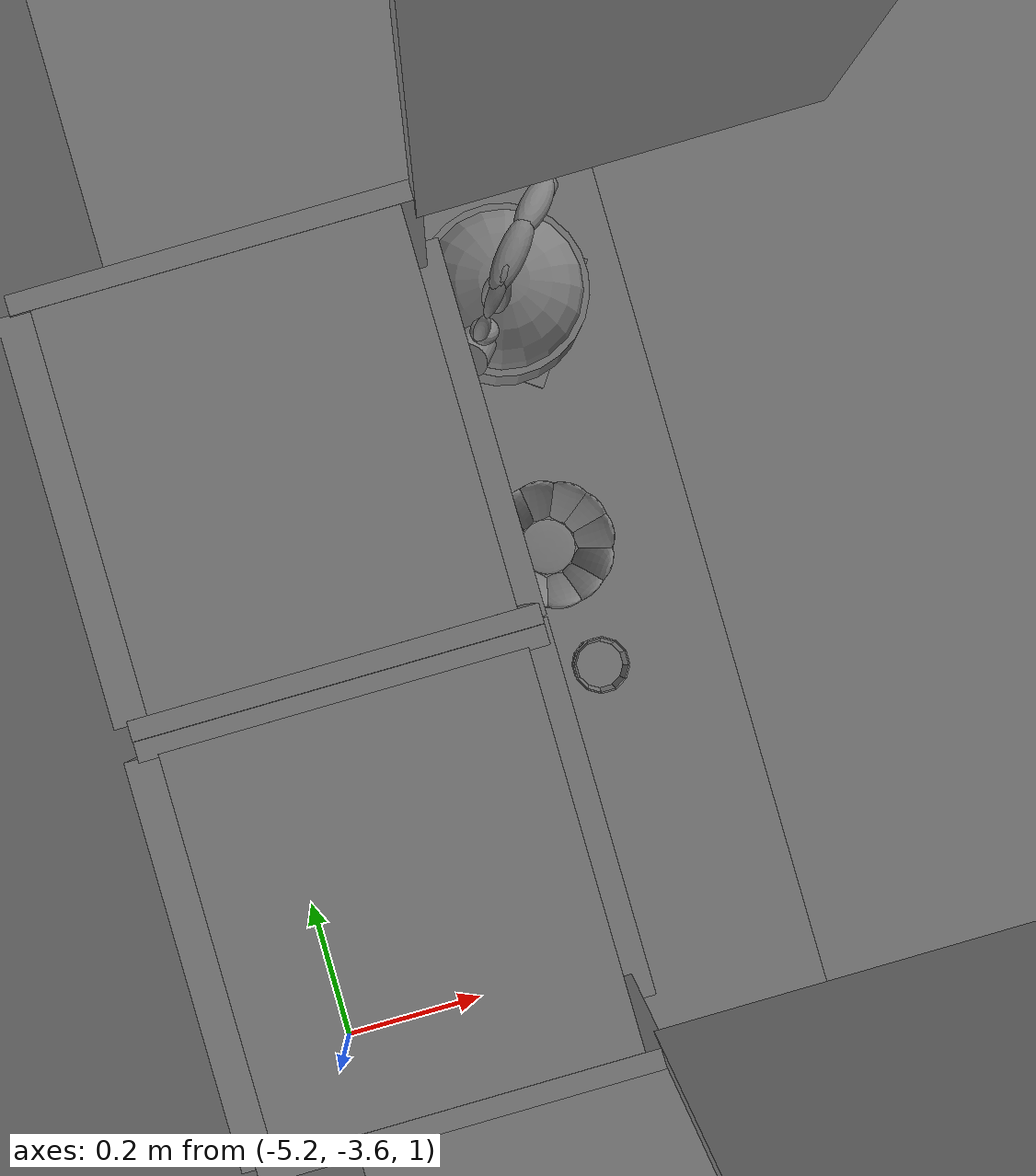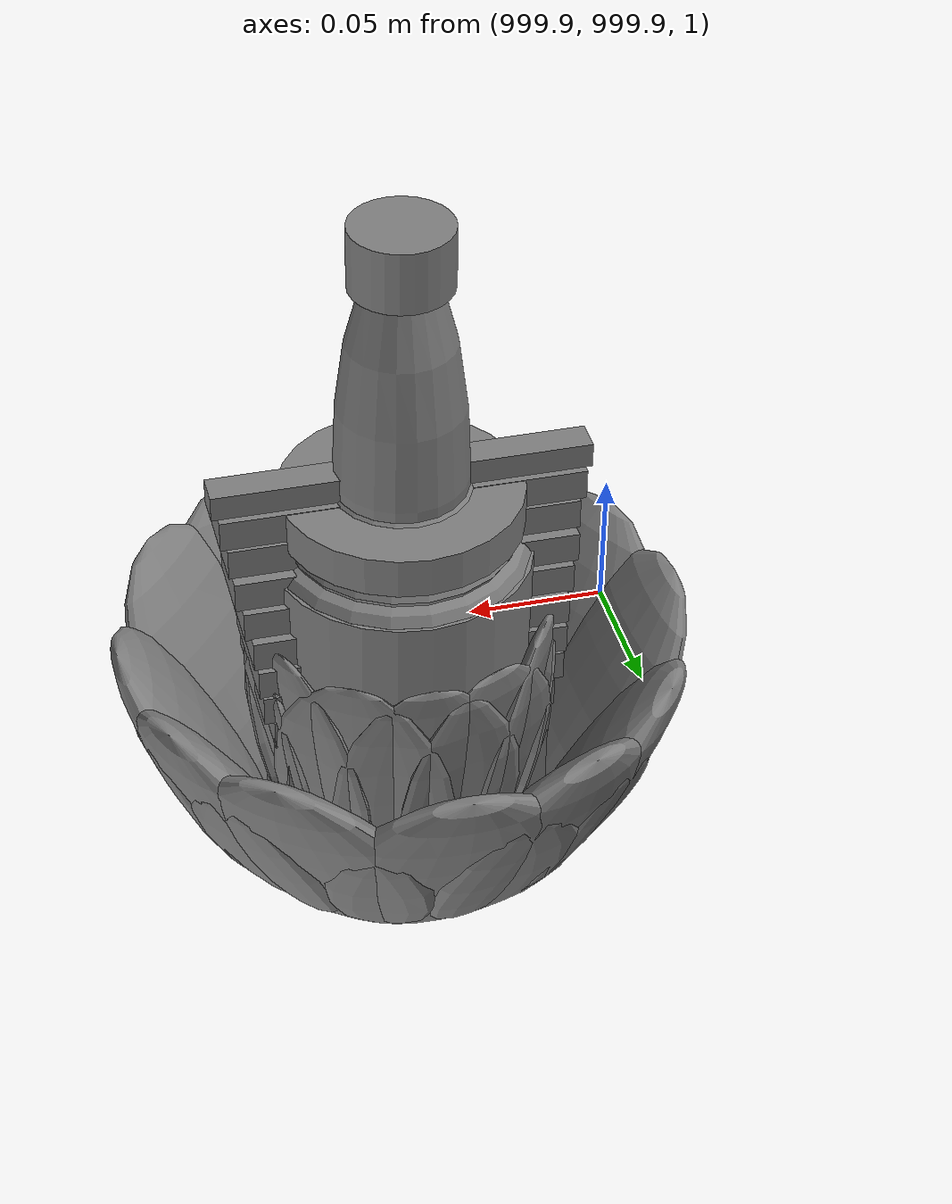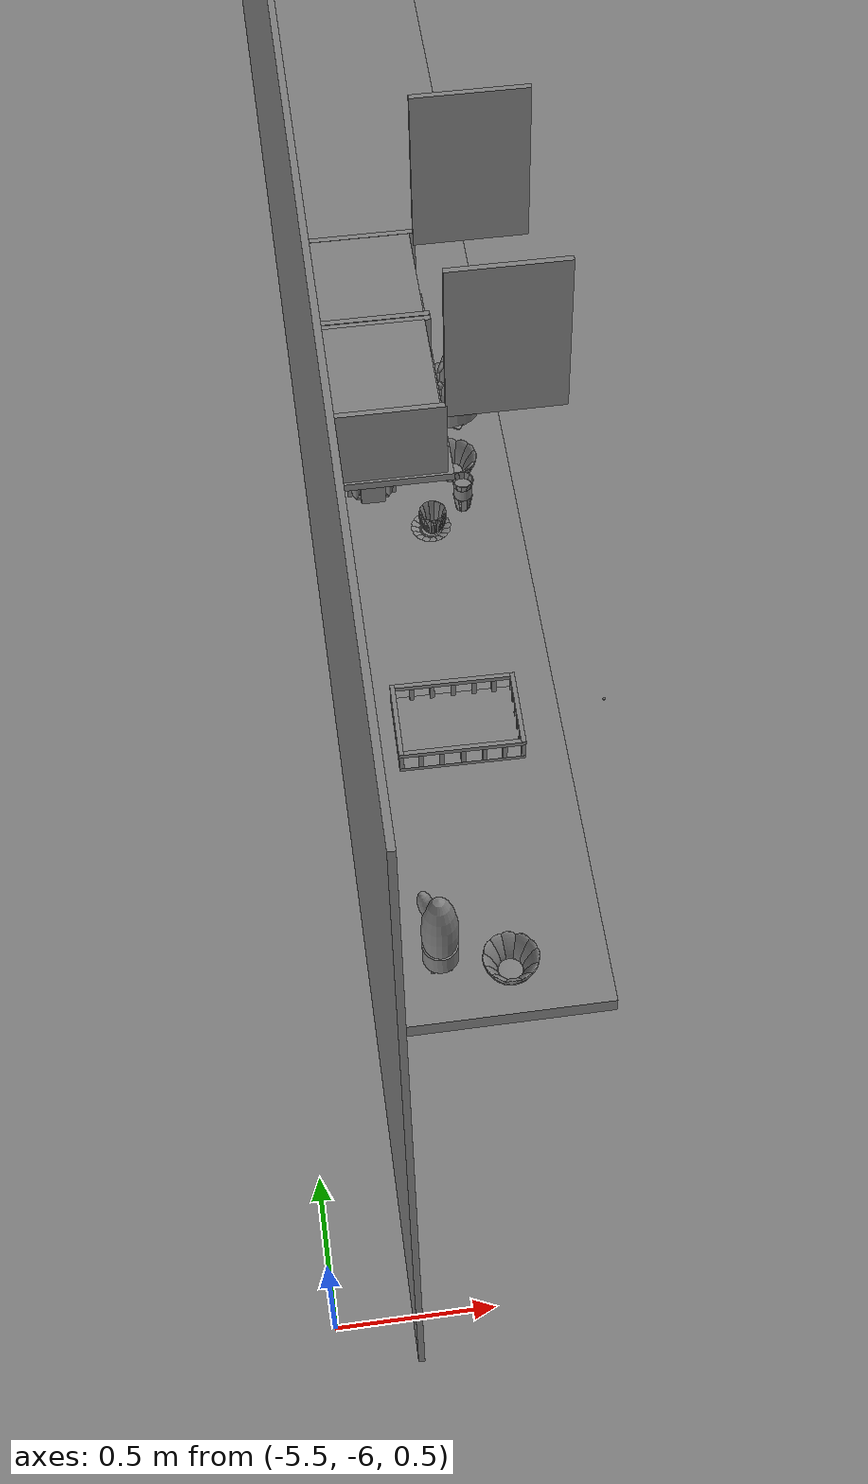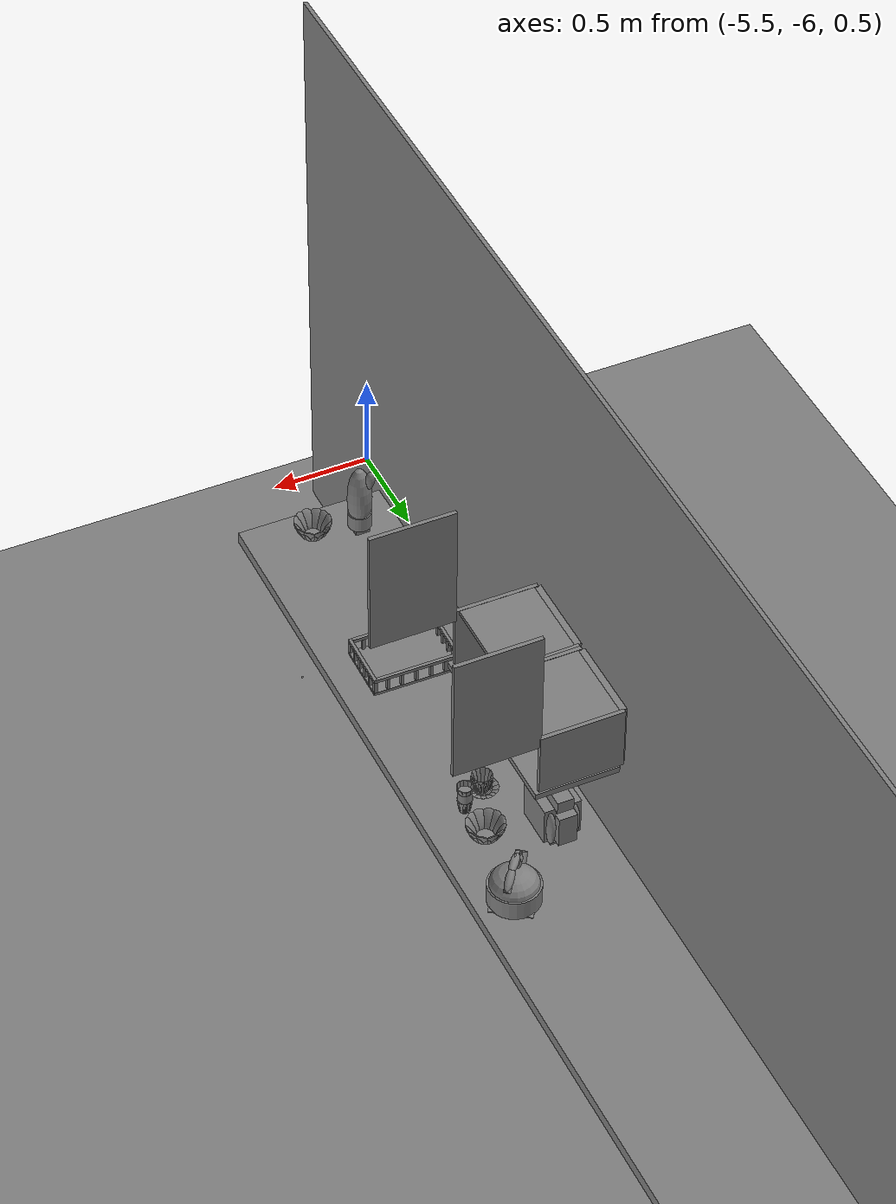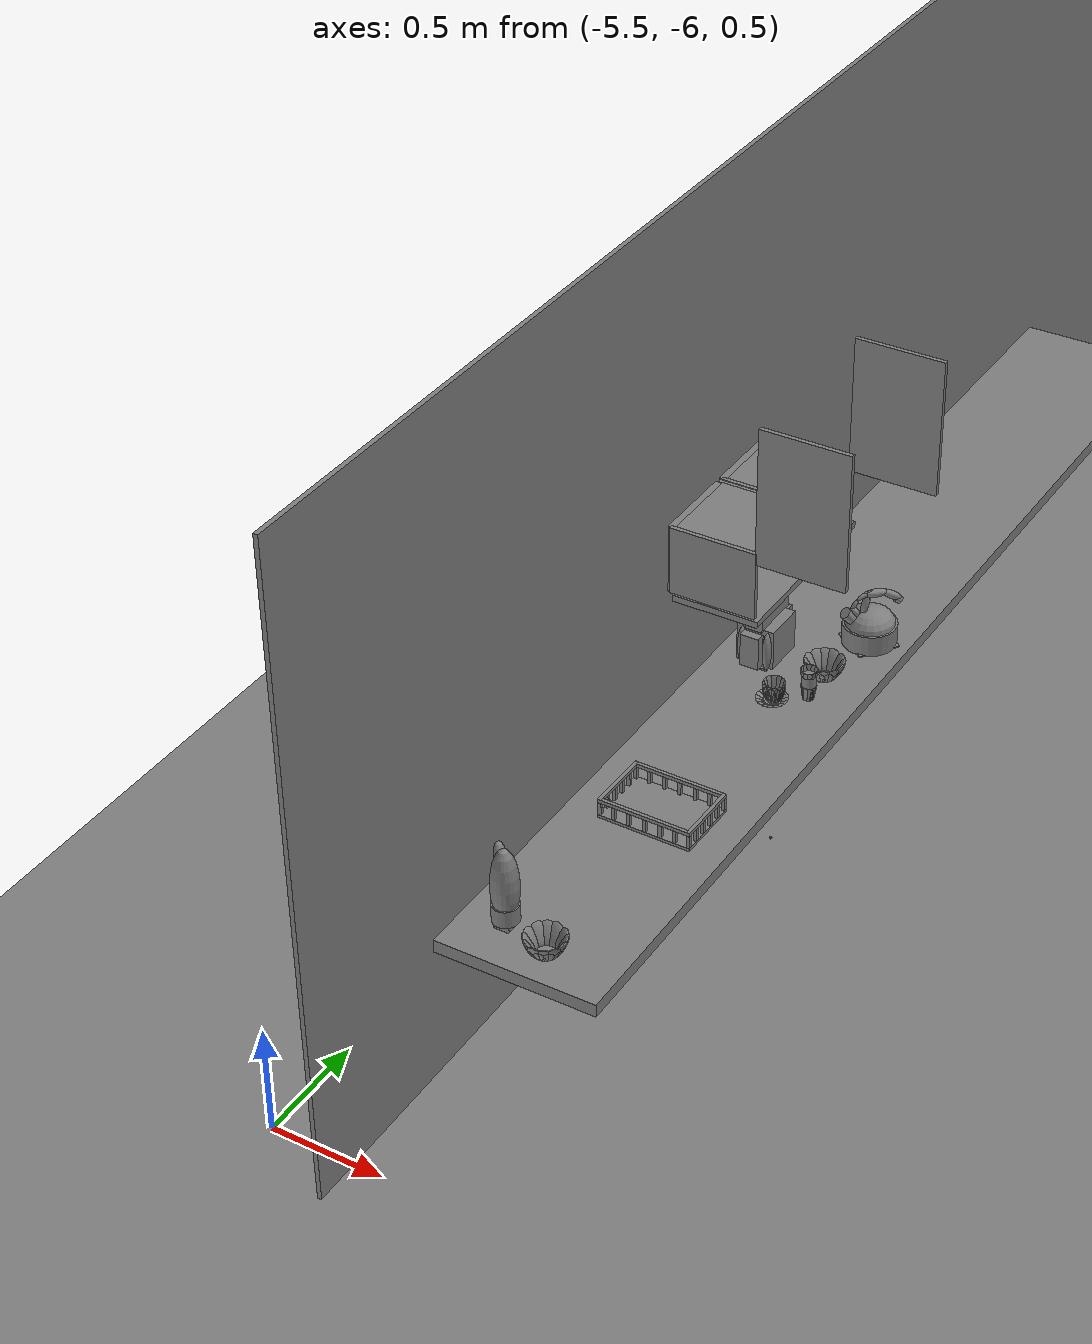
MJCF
<mujoco>
    <option gravity="0.000000000 0.000000000 -9.810000420" timestep="0.0049999999" integrator="implicitfast" density="9.8000002" viscosity="1.8000001e-05" noslip_iterations="10" iterations="100" sdf_iterations="50">
        <flag multiccd="disable"/>
    </option>
    <size memory="1000M"/>
    <compiler coordinate="local"/>
    <worldbody>
        <light cutoff="30" pos="0 1 1" dir="0 -1 -2"/>
        <light cutoff="30" pos="0 -1 1" dir="0 1 -2"/>
        <body pos="-5.046103477 -5.051773071 1.001502514" euler="0.000000000 0.000000000 0.000000000" name="Interactive Objcets_huapen">
            <geom contype="1" conaffinity="1" density="1000" type="ellipsoid" material="" rgba="0.500000000 0.500000000 0.500000000 1.000000000" solimp="0.899999976 0.949999988 0.001000000" friction="1.000000000 0.005000000 0.000100000" solref="0.020000000 1.000000000" margin="0" condim="3" group="0" pos="0.008062840 0.004346371 0.205056787" quat="1.000000000 0.000000000 0.000000000 0.000000000" size="0.059999999 0.059999999 0.180000007" name="Interactive Objcets_huapen_hua_6E4E9ACA_64AD_47DF_8792_1F25499CEAAF"/>
            <geom contype="1" conaffinity="1" density="1000" type="cylinder" material="" rgba="0.500000000 0.500000000 0.500000000 1.000000000" solimp="0.899999976 0.949999988 0.001000000" friction="1.000000000 0.005000000 0.000100000" solref="0.020000000 1.000000000" margin="0" condim="3" group="0" pos="0.008062840 0.003952026 0.080107450" quat="1.000000000 0.000000000 0.000000000 0.000000000" size="0.057999998 0.039999999 1.000000000" name="Interactive Objcets_huapen_hua_C34DF760_1B9D_4447_9E50_6E8A7D4293C5"/>
            <geom contype="1" conaffinity="1" density="1000" type="box" material="" rgba="0.500000000 0.500000000 0.500000000 1.000000000" solimp="0.899999976 0.949999988 0.001000000" friction="1.000000000 0.005000000 0.000100000" solref="0.020000000 1.000000000" margin="0" condim="3" group="0" pos="0.008062840 0.003952503 0.020566106" quat="1.000000000 0.000000000 0.000000000 0.000000000" size="0.035000000 0.035000000 0.020000000" name="Interactive Objcets_huapen_hua_6D22AEBB_A3E4_4EBB_829B_4E2A98B48068"/>
            <geom contype="1" conaffinity="1" density="1000" type="ellipsoid" material="" rgba="0.500000000 0.500000000 0.500000000 1.000000000" solimp="0.899999976 0.949999988 0.001000000" friction="1.000000000 0.005000000 0.000100000" solref="0.020000000 1.000000000" margin="0" condim="3" group="0" pos="-0.029900074 0.033599377 0.321917295" quat="0.992658079 -0.083605267 -0.087364964 0.002748166" size="0.025000000 0.025000000 0.059999999" name="Interactive Objcets_huapen_hua_876DF329_AA2F_4A53_8DCC_DEEFBB9ABDED"/>
            <freejoint name="Interactive Objcets_huapen"/>
        </body>
        <body pos="1000.000000000 1000.000000000 1.000000000" euler="0.000000000 0.000000000 0.000000000" name="openloong_gripper_2f85_fix_base_usda_jar_01">
            <geom contype="1" conaffinity="1" density="1000" type="box" material="" rgba="0.500000000 0.500000000 0.500000000 1.000000000" solimp="0.899999976 0.949999988 0.001000000" friction="1.000000000 0.005000000 0.000100000" solref="0.020000000 1.000000000" margin="0" condim="3" group="0" pos="0.000000000 0.000000000 0.006158113" quat="1.000000000 0.000000000 0.000000000 0.000000000" size="0.020000000 0.020000000 0.005000000" name="openloong_gripper_2f85_fix_base_usda_geom_6321B908_FF14_429B_AE71_493D42E13645"/>
            <geom contype="1" conaffinity="1" density="1000" type="cylinder" material="" rgba="0.500000000 0.500000000 0.500000000 1.000000000" solimp="0.899999976 0.949999988 0.001000000" friction="1.000000000 0.005000000 0.000100000" solref="0.020000000 1.000000000" margin="0" condim="3" group="0" pos="0.000000000 0.000000000 0.062744498" quat="1.000000000 0.000000000 0.000000000 0.000000000" size="0.041000001 0.052999999 1.000000000" name="openloong_gripper_2f85_fix_base_usda_geom_D5595B12_5139_4790_B9BE_E8E9B5EF873E"/>
            <geom contype="1" conaffinity="1" density="1000" type="ellipsoid" material="" rgba="0.500000000 0.500000000 0.500000000 1.000000000" solimp="0.899999976 0.949999988 0.001000000" friction="1.000000000 0.005000000 0.000100000" solref="0.020000000 1.000000000" margin="0" condim="3" group="0" pos="0.000000000 0.000000000 0.122252703" quat="1.000000000 0.000000000 0.000000000 0.000000000" size="0.035999998 0.035999998 0.010000000" name="openloong_gripper_2f85_fix_base_usda_geom_BC48A995_3986_40F2_9FDB_B893F275BACC"/>
            <geom contype="1" conaffinity="1" density="1000" type="cylinder" material="" rgba="0.500000000 0.500000000 0.500000000 1.000000000" solimp="0.899999976 0.949999988 0.001000000" friction="1.000000000 0.005000000 0.000100000" solref="0.020000000 1.000000000" margin="0" condim="3" group="0" pos="0.000000000 0.000000000 0.015747190" quat="1.000000000 0.000000000 0.000000000 0.000000000" size="0.035000000 0.010000000 1.000000000" name="openloong_gripper_2f85_fix_base_usda_geom_5C336694_BEC6_4820_8808_E6F4A166D73A"/>
            <geom contype="1" conaffinity="1" density="1000" type="ellipsoid" material="" rgba="0.500000000 0.500000000 0.500000000 1.000000000" solimp="0.899999976 0.949999988 0.001000000" friction="1.000000000 0.005000000 0.000100000" solref="0.020000000 1.000000000" margin="0" condim="3" group="0" pos="0.000000000 0.000000000 0.115815401" quat="1.000000000 0.000000000 0.000000000 0.000000000" size="0.039999999 0.039999999 0.010000000" name="openloong_gripper_2f85_fix_base_usda_geom_4543557F_9FAA_479B_AA15_39CA2B882DA0"/>
            <geom contype="1" conaffinity="1" density="1000" type="cylinder" material="" rgba="0.500000000 0.500000000 0.500000000 1.000000000" solimp="0.899999976 0.949999988 0.001000000" friction="1.000000000 0.005000000 0.000100000" solref="0.020000000 1.000000000" margin="0" condim="3" group="0" pos="0.000000000 0.000000000 0.133183479" quat="1.000000000 0.000000000 0.000000000 0.000000000" size="0.037999999 0.006500000 1.000000000" name="openloong_gripper_2f85_fix_base_usda_geom_4AF9CF21_E47A_4C67_AB45_248F62A9E2B0"/>
            <freejoint name="openloong_gripper_2f85_fix_base_usda_jar_01_joint"/>
            <site size="0.005000000 0.005000000 0.005000000" rgba="0.500000000 0.500000000 0.500000000 1.000000000" pos="0.000000000 0.000000000 0.000000000" quat="1.000000000 0.000000000 0.000000000 0.000000000" group="0" type="sphere" name="openloong_gripper_2f85_fix_base_usda_jar_01site"/>
        </body>
        <body pos="-4.086245060 -4.055747986 1.807396173" euler="77.888458252 36.642646790 -54.911327362" mocap="true" name="spotlight1_SpotLight"/>
        <body pos="-4.409523010 -4.373135567 1.856821060" euler="-22.748376846 -23.782981873 9.261351585" mocap="true" name="spotlight4_SpotLight"/>
        <body pos="1000.000000000 1000.000000000 1.000000000" euler="0.000000000 0.000000000 0.000000000" name="openloong_gripper_2f85_fix_base_usda_bottle_red">
            <geom contype="1" conaffinity="1" density="1000" type="ellipsoid" material="" rgba="0.500000000 0.500000000 0.500000000 1.000000000" solimp="0.899999976 0.949999988 0.001000000" friction="1.000000000 0.005000000 0.000100000" solref="0.020000000 1.000000000" margin="0" condim="3" group="0" pos="0.000000000 0.000000000 0.144284487" quat="1.000000000 0.000000000 0.000000000 0.000000000" size="0.021000000 0.021000000 0.079999998" name="openloong_gripper_2f85_fix_base_usda_geom_63DEFBF2_12E7_4586_8BFB_601567C746A6"/>
            <geom contype="1" conaffinity="1" density="1000" type="cylinder" material="" rgba="0.500000000 0.500000000 0.500000000 1.000000000" solimp="0.899999976 0.949999988 0.001000000" friction="1.000000000 0.005000000 0.000100000" solref="0.020000000 1.000000000" margin="0" condim="3" group="0" pos="0.000000000 0.000000000 0.220618963" quat="1.000000000 0.000000000 0.000000000 0.000000000" size="0.016000001 0.010000000 1.000000000" name="openloong_gripper_2f85_fix_base_usda_geom_6B97F2F2_8A9E_4FEF_9112_C3113DAC0921"/>
            <geom contype="1" conaffinity="1" density="1000" type="ellipsoid" material="" rgba="0.500000000 0.500000000 0.500000000 1.000000000" solimp="0.899999976 0.949999988 0.001000000" friction="1.000000000 0.005000000 0.000100000" solref="0.020000000 1.000000000" margin="0" condim="3" group="0" pos="0.000000000 0.000000000 0.118945479" quat="1.000000000 0.000000000 0.000000000 0.000000000" size="0.030999999 0.030999999 0.029999999" name="openloong_gripper_2f85_fix_base_usda_geom_2058BBEE_188A_46E0_9327_0E822B85A333"/>
            <geom contype="1" conaffinity="1" density="1000" type="box" material="" rgba="0.500000000 0.500000000 0.500000000 1.000000000" solimp="0.899999976 0.949999988 0.001000000" friction="1.000000000 0.005000000 0.000100000" solref="0.020000000 1.000000000" margin="0" condim="3" group="0" pos="0.000000000 0.000000000 0.002189159" quat="1.000000000 0.000000000 0.000000000 0.000000000" size="0.020000000 0.020000000 0.003000000" name="openloong_gripper_2f85_fix_base_usda_geom_5004AAF8_B4E8_4E7C_964B_E484EAD8EEB9"/>
            <geom contype="1" conaffinity="1" density="1000" type="cylinder" material="" rgba="0.500000000 0.500000000 0.500000000 1.000000000" solimp="0.899999976 0.949999988 0.001000000" friction="1.000000000 0.005000000 0.000100000" solref="0.020000000 1.000000000" margin="0" condim="3" group="0" pos="0.000000000 -0.000366211 0.060884237" quat="1.000000000 0.000000000 0.000000000 0.000000000" size="0.030999999 0.057999998 1.000000000" name="openloong_gripper_2f85_fix_base_usda_geom_4CC17C03_3008_4BEB_9CF9_70C6C489879E"/>
            <freejoint name="openloong_gripper_2f85_fix_base_usda_bottle_red_joint"/>
            <site size="0.005000000 0.005000000 0.005000000" rgba="0.500000000 0.500000000 0.500000000 1.000000000" pos="0.000000000 0.000000000 0.000000000" quat="0.999961913 0.008726535 0.000000000 0.000000000" group="0" type="sphere" name="openloong_gripper_2f85_fix_base_usda_bottle_redsite"/>
        </body>
        <body pos="1000.000000000 1000.000000000 1.000000000" euler="0.000000000 0.000000000 0.000000000" name="openloong_gripper_2f85_fix_base_usda_bow_yellow_kps">
            <geom contype="1" conaffinity="1" density="1000" type="ellipsoid" material="" rgba="0.500000000 0.500000000 0.500000000 1.000000000" solimp="0.899999976 0.949999988 0.001000000" friction="1.000000000 0.005000000 0.000100000" solref="0.020000000 1.000000000" margin="0" condim="3" group="0" pos="-0.052185059 0.040283203 0.044118762" quat="0.919264615 -0.076883033 -0.225593656 -0.313287765" size="0.010000000 0.039999999 0.052000001" name="openloong_gripper_2f85_fix_base_usda_geom_23B86DF2_3A39_4112_BB4C_C5659809B59C"/>
            <geom contype="1" conaffinity="1" density="1000" type="ellipsoid" material="" rgba="0.500000000 0.500000000 0.500000000 1.000000000" solimp="0.899999976 0.949999988 0.001000000" friction="1.000000000 0.005000000 0.000100000" solref="0.020000000 1.000000000" margin="0" condim="3" group="0" pos="-0.000061035 0.065979004 0.044118762" quat="0.687598765 -0.168314874 -0.168741167 -0.685860336" size="0.010000000 0.039999999 0.052000001" name="openloong_gripper_2f85_fix_base_usda_geom_8D3EE5A3_0D26_4498_AF56_3D8DE8A2BD7B"/>
            <geom contype="1" conaffinity="1" density="1000" type="box" material="" rgba="0.500000000 0.500000000 0.500000000 1.000000000" solimp="0.899999976 0.949999988 0.001000000" friction="1.000000000 0.005000000 0.000100000" solref="0.020000000 1.000000000" margin="0" condim="3" group="0" pos="0.000061035 0.000000000 -0.002001643" quat="1.000000000 0.000000000 0.000000000 0.000000000" size="0.029999999 0.029999999 0.002000000" name="openloong_gripper_2f85_fix_base_usda_geom_4A4A9294_5AF4_4609_A212_D150EF4389FA"/>
            <geom contype="1" conaffinity="1" density="1000" type="ellipsoid" material="" rgba="0.500000000 0.500000000 0.500000000 1.000000000" solimp="0.899999976 0.949999988 0.001000000" friction="1.000000000 0.005000000 0.000100000" solref="0.020000000 1.000000000" margin="0" condim="3" group="0" pos="0.029418945 -0.059082031 0.044118762" quat="0.825555861 0.125530601 0.202597082 -0.511521280" size="0.010000000 0.039999999 0.052000001" name="openloong_gripper_2f85_fix_base_usda_geom_C2730C42_B77E_4934_AF11_D12D7ED32306"/>
            <geom contype="1" conaffinity="1" density="1000" type="ellipsoid" material="" rgba="0.500000000 0.500000000 0.500000000 1.000000000" solimp="0.899999976 0.949999988 0.001000000" friction="1.000000000 0.005000000 0.000100000" solref="0.020000000 1.000000000" margin="0" condim="3" group="0" pos="0.000244141 -0.065979004 0.044118762" quat="0.687598765 0.168314651 0.168741375 -0.685860336" size="0.010000000 0.039999999 0.052000001" name="openloong_gripper_2f85_fix_base_usda_geom_49FBEFFD_7BEB_4AAD_9454_AD700D3393C4"/>
            <geom contype="1" conaffinity="1" density="1000" type="ellipsoid" material="" rgba="0.500000000 0.500000000 0.500000000 1.000000000" solimp="0.899999976 0.949999988 0.001000000" friction="1.000000000 0.005000000 0.000100000" solref="0.020000000 1.000000000" margin="0" condim="3" group="0" pos="0.000061035 0.000000000 0.000446677" quat="1.000000000 0.000000000 0.000000000 0.000000000" size="0.039999999 0.039999999 0.002000000" name="openloong_gripper_2f85_fix_base_usda_geom_1BD9C093_4DA6_477E_A693_959BA78E6D6F"/>
            <geom contype="1" conaffinity="1" density="1000" type="ellipsoid" material="" rgba="0.500000000 0.500000000 0.500000000 1.000000000" solimp="0.899999976 0.949999988 0.001000000" friction="1.000000000 0.005000000 0.000100000" solref="0.020000000 1.000000000" margin="0" condim="3" group="0" pos="0.059082031 0.029541016 0.044118762" quat="0.223252773 -0.231952220 -0.054787423 -0.945174456" size="0.010000000 0.039999999 0.052000001" name="openloong_gripper_2f85_fix_base_usda_geom_22239086_15C1_4AA5_9FB4_E654CD8A4EDE"/>
            <geom contype="1" conaffinity="1" density="1000" type="ellipsoid" material="" rgba="0.500000000 0.500000000 0.500000000 1.000000000" solimp="0.899999976 0.949999988 0.001000000" friction="1.000000000 0.005000000 0.000100000" solref="0.020000000 1.000000000" margin="0" condim="3" group="0" pos="0.000061035 0.000000000 0.007335305" quat="1.000000000 0.000000000 0.000000000 0.000000000" size="0.039999999 0.039999999 0.002000000" name="openloong_gripper_2f85_fix_base_usda_geom_97700C3A_697D_46B5_B741_AB9D64E405EF"/>
            <geom contype="1" conaffinity="1" density="1000" type="ellipsoid" material="" rgba="0.500000000 0.500000000 0.500000000 1.000000000" solimp="0.899999976 0.949999988 0.001000000" friction="1.000000000 0.005000000 0.000100000" solref="0.020000000 1.000000000" margin="0" condim="3" group="0" pos="-0.029296875 0.059082031 0.044118762" quat="0.825555861 -0.125530809 -0.202596918 -0.511521280" size="0.010000000 0.039999999 0.052000001" name="openloong_gripper_2f85_fix_base_usda_geom_01108D4B_0550_4522_8F53_CC5CB149C9E9"/>
            <geom contype="1" conaffinity="1" density="1000" type="ellipsoid" material="" rgba="0.500000000 0.500000000 0.500000000 1.000000000" solimp="0.899999976 0.949999988 0.001000000" friction="1.000000000 0.005000000 0.000100000" solref="0.020000000 1.000000000" margin="0" condim="3" group="0" pos="0.040222168 0.052368164 0.044118762" quat="0.429593176 -0.213750049 -0.105424821 -0.871002972" size="0.010000000 0.039999999 0.052000001" name="openloong_gripper_2f85_fix_base_usda_geom_C0D3A3E1_7634_4A6B_9755_F74E9640EE9D"/>
            <geom contype="1" conaffinity="1" density="1000" type="ellipsoid" material="" rgba="0.500000000 0.500000000 0.500000000 1.000000000" solimp="0.899999976 0.949999988 0.001000000" friction="1.000000000 0.005000000 0.000100000" solref="0.020000000 1.000000000" margin="0" condim="3" group="0" pos="0.066040039 0.000000000 0.044118762" quat="0.971183062 -0.000000156 0.238334835 0.000000030" size="0.010000000 0.039999999 0.052000001" name="openloong_gripper_2f85_fix_base_usda_geom_6C9F1DF6_B628_4CC1_BDF0_0BD526E3F996"/>
            <geom contype="1" conaffinity="1" density="1000" type="ellipsoid" material="" rgba="0.500000000 0.500000000 0.500000000 1.000000000" solimp="0.899999976 0.949999988 0.001000000" friction="1.000000000 0.005000000 0.000100000" solref="0.020000000 1.000000000" margin="0" condim="3" group="0" pos="0.052307129 -0.040283203 0.044118762" quat="0.919264674 0.076882750 0.225593731 -0.313287705" size="0.010000000 0.039999999 0.052000001" name="openloong_gripper_2f85_fix_base_usda_geom_86D3B9BC_D176_498A_A809_9784F376EF82"/>
            <geom contype="1" conaffinity="1" density="1000" type="ellipsoid" material="" rgba="0.500000000 0.500000000 0.500000000 1.000000000" solimp="0.899999976 0.949999988 0.001000000" friction="1.000000000 0.005000000 0.000100000" solref="0.020000000 1.000000000" margin="0" condim="3" group="0" pos="-0.065917969 0.000000000 0.044118762" quat="0.971183062 -0.000000142 -0.238334835 0.000000030" size="0.010000000 0.039999999 0.052000001" name="openloong_gripper_2f85_fix_base_usda_geom_CB94A07A_DD2A_4183_89F6_8DAC9337720C"/>
            <geom contype="1" conaffinity="1" density="1000" type="ellipsoid" material="" rgba="0.500000000 0.500000000 0.500000000 1.000000000" solimp="0.899999976 0.949999988 0.001000000" friction="1.000000000 0.005000000 0.000100000" solref="0.020000000 1.000000000" margin="0" condim="3" group="0" pos="-0.058898926 -0.029541016 0.044118762" quat="0.223252758 0.231952101 0.054787733 -0.945174575" size="0.010000000 0.039999999 0.052000001" name="openloong_gripper_2f85_fix_base_usda_geom_11625EE4_8E54_4820_85EE_A45DF5B550C4"/>
            <geom contype="1" conaffinity="1" density="1000" type="ellipsoid" material="" rgba="0.500000000 0.500000000 0.500000000 1.000000000" solimp="0.899999976 0.949999988 0.001000000" friction="1.000000000 0.005000000 0.000100000" solref="0.020000000 1.000000000" margin="0" condim="3" group="0" pos="-0.040100098 -0.052368164 0.044118762" quat="0.429593235 0.213749886 0.105425082 -0.871003032" size="0.010000000 0.039999999 0.052000001" name="openloong_gripper_2f85_fix_base_usda_geom_91F9ED07_103B_4498_87A9_797BF211D9D5"/>
            <freejoint name="openloong_gripper_2f85_fix_base_usda_bow_yellow_kps_joint"/>
            <site size="0.005000000 0.005000000 0.005000000" rgba="0.500000000 0.500000000 0.500000000 1.000000000" pos="0.000000000 0.000000000 0.000000000" quat="0.999961913 0.008726534 0.000000000 0.000000000" group="0" type="sphere" name="openloong_gripper_2f85_fix_base_usda_bow_yellow_kps"/>
        </body>
        <body pos="1000.000000000 1000.000000000 1.000000000" euler="0.000000000 0.000000000 0.000000000" name="openloong_gripper_2f85_fix_base_usda_salt">
            <geom contype="1" conaffinity="1" density="1000" type="box" material="" rgba="0.500000000 0.500000000 0.500000000 1.000000000" solimp="0.899999976 0.949999988 0.001000000" friction="1.000000000 0.005000000 0.000100000" solref="0.020000000 1.000000000" margin="0" condim="3" group="0" pos="0.000305176 0.000000000 0.084862232" quat="1.000000000 0.000000000 0.000000000 0.000000000" size="0.048999999 0.018999999 0.005000000" name="openloong_gripper_2f85_fix_base_usda_geom_F593BF5D_A0D2_4779_9C86_99B1F16CC37E"/>
            <geom contype="1" conaffinity="1" density="1000" type="box" material="" rgba="0.500000000 0.500000000 0.500000000 1.000000000" solimp="0.899999976 0.949999988 0.001000000" friction="1.000000000 0.005000000 0.000100000" solref="0.020000000 1.000000000" margin="0" condim="3" group="0" pos="0.000305176 0.000000000 0.104564309" quat="1.000000000 0.000000000 0.000000000 0.000000000" size="0.052000001 0.014000000 0.005000000" name="openloong_gripper_2f85_fix_base_usda_geom_8073746F_052E_4255_9232_97367B7B8A37"/>
            <geom contype="1" conaffinity="1" density="1000" type="box" material="" rgba="0.500000000 0.500000000 0.500000000 1.000000000" solimp="0.899999976 0.949999988 0.001000000" friction="1.000000000 0.005000000 0.000100000" solref="0.020000000 1.000000000" margin="0" condim="3" group="0" pos="0.000305176 0.000000000 0.114487171" quat="1.000000000 0.000000000 0.000000000 0.000000000" size="0.054000001 0.011500000 0.005000000" name="openloong_gripper_2f85_fix_base_usda_geom_DA1701BC_AEE3_4DED_BE52_EDB372258CBD"/>
            <geom contype="1" conaffinity="1" density="1000" type="box" material="" rgba="0.500000000 0.500000000 0.500000000 1.000000000" solimp="0.899999976 0.949999988 0.001000000" friction="1.000000000 0.005000000 0.000100000" solref="0.020000000 1.000000000" margin="0" condim="3" group="0" pos="0.000305176 0.000000000 0.075103164" quat="1.000000000 0.000000000 0.000000000 0.000000000" size="0.048000000 0.020000000 0.005000000" name="openloong_gripper_2f85_fix_base_usda_geom_AAC4F119_F48B_4784_B8CC_54E722AE348B"/>
            <geom contype="1" conaffinity="1" density="1000" type="box" material="" rgba="0.500000000 0.500000000 0.500000000 1.000000000" solimp="0.899999976 0.949999988 0.001000000" friction="1.000000000 0.005000000 0.000100000" solref="0.020000000 1.000000000" margin="0" condim="3" group="0" pos="0.000305176 0.000000000 0.134892464" quat="1.000000000 0.000000000 0.000000000 0.000000000" size="0.057000000 0.007000000 0.005000000" name="openloong_gripper_2f85_fix_base_usda_geom_F44DDC5A_9BFB_4657_8D20_FA1301F362A0"/>
            <geom contype="1" conaffinity="1" density="1000" type="box" material="" rgba="0.500000000 0.500000000 0.500000000 1.000000000" solimp="0.899999976 0.949999988 0.001000000" friction="1.000000000 0.005000000 0.000100000" solref="0.020000000 1.000000000" margin="0" condim="3" group="0" pos="0.000305176 0.000000000 0.094920278" quat="1.000000000 0.000000000 0.000000000 0.000000000" size="0.050000001 0.017000001 0.005000000" name="openloong_gripper_2f85_fix_base_usda_geom_74F6E492_64E1_433E_B98B_19D4390E3791"/>
            <geom contype="1" conaffinity="1" density="1000" type="box" material="" rgba="0.500000000 0.500000000 0.500000000 1.000000000" solimp="0.899999976 0.949999988 0.001000000" friction="1.000000000 0.005000000 0.000100000" solref="0.020000000 1.000000000" margin="0" condim="3" group="0" pos="0.000305176 0.000000000 0.065204859" quat="1.000000000 0.000000000 0.000000000 0.000000000" size="0.045000002 0.021000000 0.005000000" name="openloong_gripper_2f85_fix_base_usda_geom_E3A90714_485E_4D11_9E14_560CB940260C"/>
            <geom contype="1" conaffinity="1" density="1000" type="box" material="" rgba="0.500000000 0.500000000 0.500000000 1.000000000" solimp="0.899999976 0.949999988 0.001000000" friction="1.000000000 0.005000000 0.000100000" solref="0.020000000 1.000000000" margin="0" condim="3" group="0" pos="0.000305176 0.000000000 0.144135714" quat="1.000000000 0.000000000 0.000000000 0.000000000" size="0.059000000 0.005000000 0.004000000" name="openloong_gripper_2f85_fix_base_usda_geom_51537AEE_86CA_4AE7_AAA0_6FBB8DBAD9CD"/>
            <geom contype="1" conaffinity="1" density="1000" type="box" material="" rgba="0.500000000 0.500000000 0.500000000 1.000000000" solimp="0.899999976 0.949999988 0.001000000" friction="1.000000000 0.005000000 0.000100000" solref="0.020000000 1.000000000" margin="0" condim="3" group="0" pos="0.000000000 0.000000000 0.031593561" quat="1.000000000 0.000000000 0.000000000 0.000000000" size="0.041999999 0.024000000 0.029999999" name="openloong_gripper_2f85_fix_base_usda_geom_EB2865C4_B4EA_434D_8DB8_D7A8F84DC901"/>
            <geom contype="1" conaffinity="1" density="1000" type="box" material="" rgba="0.500000000 0.500000000 0.500000000 1.000000000" solimp="0.899999976 0.949999988 0.001000000" friction="1.000000000 0.005000000 0.000100000" solref="0.020000000 1.000000000" margin="0" condim="3" group="0" pos="0.000305176 0.000000000 0.124608755" quat="1.000000000 0.000000000 0.000000000 0.000000000" size="0.055000000 0.008000000 0.005000000" name="openloong_gripper_2f85_fix_base_usda_geom_C908E566_FB4B_4648_9655_82C7B4F020BD"/>
            <freejoint name="openloong_gripper_2f85_fix_base_usda_salt_joint"/>
            <site size="0.005000000 0.005000000 0.005000000" rgba="0.500000000 0.500000000 0.500000000 1.000000000" pos="0.000000000 0.000000000 0.000000000" quat="1.000000000 0.000000000 0.000000000 0.000000000" group="0" type="sphere" name="openloong_gripper_2f85_fix_base_usda_saltsite"/>
        </body>
        <body pos="-4.299393654 -3.917973518 1.878495097" euler="160.470458984 -68.455284119 115.127479553" mocap="true" name="spotlight2_SpotLight"/>
        <body pos="1000.000000000 1000.000000000 1.000000000" euler="0.000000000 0.000000000 0.000000000" name="openloong_gripper_2f85_fix_base_usda_coffeecup_white_kps">
            <geom contype="1" conaffinity="1" density="1000" type="capsule" material="" rgba="0.500000000 0.500000000 0.500000000 1.000000000" solimp="0.899999976 0.949999988 0.001000000" friction="1.000000000 0.005000000 0.000100000" solref="0.020000000 1.000000000" margin="0" condim="3" group="0" pos="-0.000854492 -0.065795898 0.050029993" quat="0.343559504 -0.613204718 0.626912475 0.336047262" size="0.004000000 0.005000000 1.000000000" name="openloong_gripper_2f85_fix_base_usda_geom_90B252C9_D162_4C40_B1B5_06AD2FE234D6"/>
            <geom contype="1" conaffinity="1" density="1000" type="ellipsoid" material="" rgba="0.500000000 0.500000000 0.500000000 1.000000000" solimp="0.899999976 0.949999988 0.001000000" friction="1.000000000 0.005000000 0.000100000" solref="0.020000000 1.000000000" margin="0" condim="3" group="0" pos="-0.000793457 -0.038452148 0.048040152" quat="0.711656272 0.066323131 -0.067805752 0.696095467" size="0.005000000 0.029999999 0.048999999" name="openloong_gripper_2f85_fix_base_usda_geom_8ADAC3F9_4007_44EF_84AB_E75BEE8175EF"/>
            <geom contype="1" conaffinity="1" density="1000" type="ellipsoid" material="" rgba="0.500000000 0.500000000 0.500000000 1.000000000" solimp="0.899999976 0.949999988 0.001000000" friction="1.000000000 0.005000000 0.000100000" solref="0.020000000 1.000000000" margin="0" condim="3" group="0" pos="0.037719727 -0.001892090 0.048040152" quat="0.995387912 0.001371633 0.094835162 -0.014391154" size="0.005000000 0.029999999 0.048999999" name="openloong_gripper_2f85_fix_base_usda_geom_D921403D_0976_488C_8351_00A4CEFDE3B4"/>
            <geom contype="1" conaffinity="1" density="1000" type="ellipsoid" material="" rgba="0.500000000 0.500000000 0.500000000 1.000000000" solimp="0.899999976 0.949999988 0.001000000" friction="1.000000000 0.005000000 0.000100000" solref="0.020000000 1.000000000" margin="0" condim="3" group="0" pos="0.033996582 0.015502930 0.048040152" quat="0.970659733 -0.021051638 0.092478797 0.220962167" size="0.005000000 0.029999999 0.048999999" name="openloong_gripper_2f85_fix_base_usda_geom_365C2761_D229_4B46_A490_E05BE2B526FD"/>
            <geom contype="1" conaffinity="1" density="1000" type="box" material="" rgba="0.500000000 0.500000000 0.500000000 1.000000000" solimp="0.899999976 0.949999988 0.001000000" friction="1.000000000 0.005000000 0.000100000" solref="0.020000000 1.000000000" margin="0" condim="3" group="0" pos="0.000793457 -0.000183105 0.000156164" quat="0.714879215 0.000000000 0.000000000 0.699247897" size="0.020000000 0.020000000 0.002000000" name="openloong_gripper_2f85_fix_base_usda_geom_77A1D1B0_99F7_4D4D_A43F_1F5382CAF22E"/>
            <geom contype="1" conaffinity="1" density="1000" type="ellipsoid" material="" rgba="0.500000000 0.500000000 0.500000000 1.000000000" solimp="0.899999976 0.949999988 0.001000000" friction="1.000000000 0.005000000 0.000100000" solref="0.020000000 1.000000000" margin="0" condim="3" group="0" pos="-0.019409180 -0.033081055 0.048040152" quat="0.866879702 0.046630561 -0.082595348 0.489411235" size="0.005000000 0.029999999 0.048999999" name="openloong_gripper_2f85_fix_base_usda_geom_A00D87E4_7381_49CA_BD39_2426FE8EDD41"/>
            <geom contype="1" conaffinity="1" density="1000" type="ellipsoid" material="" rgba="0.500000000 0.500000000 0.500000000 1.000000000" solimp="0.899999976 0.949999988 0.001000000" friction="1.000000000 0.005000000 0.000100000" solref="0.020000000 1.000000000" margin="0" condim="3" group="0" pos="-0.016052246 0.033264160 0.048040152" quat="0.840792537 -0.050782297 -0.080109790 -0.532983541" size="0.005000000 0.029999999 0.048999999" name="openloong_gripper_2f85_fix_base_usda_geom_D7CA5149_2CAF_4844_8ED3_835901A292FE"/>
            <geom contype="1" conaffinity="1" density="1000" type="capsule" material="" rgba="0.500000000 0.500000000 0.500000000 1.000000000" solimp="0.899999976 0.949999988 0.001000000" friction="1.000000000 0.005000000 0.000100000" solref="0.020000000 1.000000000" margin="0" condim="3" group="0" pos="-0.000549316 -0.053527832 0.046825886" quat="0.505496025 -0.494442940 0.505495846 0.494442940" size="0.004000000 0.005000000 1.000000000" name="openloong_gripper_2f85_fix_base_usda_geom_93B07A07_6F50_418E_B0C8_3A9D92164FEE"/>
            <geom contype="1" conaffinity="1" density="1000" type="ellipsoid" material="" rgba="0.500000000 0.500000000 0.500000000 1.000000000" solimp="0.899999976 0.949999988 0.001000000" friction="1.000000000 0.005000000 0.000100000" solref="0.020000000 1.000000000" margin="0" condim="3" group="0" pos="-0.032104492 0.018920898 0.048040152" quat="0.958129764 -0.025742561 -0.091288343 -0.270168930" size="0.005000000 0.029999999 0.048999999" name="openloong_gripper_2f85_fix_base_usda_geom_3D5F8E13_0E05_4EC7_9E91_2AE84DB3730E"/>
            <geom contype="1" conaffinity="1" density="1000" type="ellipsoid" material="" rgba="0.500000000 0.500000000 0.500000000 1.000000000" solimp="0.899999976 0.949999988 0.001000000" friction="1.000000000 0.005000000 0.000100000" solref="0.020000000 1.000000000" margin="0" condim="3" group="0" pos="-0.037597656 0.000305176 0.048040152" quat="0.995387554 -0.001371440 -0.094839431 -0.014389008" size="0.005000000 0.029999999 0.048999999" name="openloong_gripper_2f85_fix_base_usda_geom_9884445F_AD6B_4833_95AD_4478EA893C64"/>
            <geom contype="1" conaffinity="1" density="1000" type="capsule" material="" rgba="0.500000000 0.500000000 0.500000000 1.000000000" solimp="0.899999976 0.949999988 0.001000000" friction="1.000000000 0.005000000 0.000100000" solref="0.020000000 1.000000000" margin="0" condim="3" group="0" pos="-0.000366211 -0.043762207 0.044118762" quat="0.260488123 -0.651174724 0.665731549 0.254792154" size="0.004000000 0.003000000 1.000000000" name="openloong_gripper_2f85_fix_base_usda_geom_09849A34_9AF4_47D9_94ED_DAF7EDBB2B40"/>
            <geom contype="1" conaffinity="1" density="1000" type="capsule" material="" rgba="0.500000000 0.500000000 0.500000000 1.000000000" solimp="0.899999976 0.949999988 0.001000000" friction="1.000000000 0.005000000 0.000100000" solref="0.020000000 1.000000000" margin="0" condim="3" group="0" pos="-0.000915527 -0.068542480 0.082936406" quat="0.624995589 -0.339446366 0.347034454 0.611329615" size="0.004000000 0.004000000 1.000000000" name="openloong_gripper_2f85_fix_base_usda_geom_B5DCFC19_3D8B_48BD_967D_CCF9A438C5E4"/>
            <geom contype="1" conaffinity="1" density="1000" type="ellipsoid" material="" rgba="0.500000000 0.500000000 0.500000000 1.000000000" solimp="0.899999976 0.949999988 0.001000000" friction="1.000000000 0.005000000 0.000100000" solref="0.020000000 1.000000000" margin="0" condim="3" group="0" pos="0.016113281 -0.034851074 0.048040152" quat="0.840793252 0.050779939 0.080106191 -0.532983422" size="0.005000000 0.029999999 0.048999999" name="openloong_gripper_2f85_fix_base_usda_geom_5A79B1D8_4107_4B46_8827_51DE08DD52B3"/>
            <geom contype="1" conaffinity="1" density="1000" type="ellipsoid" material="" rgba="0.500000000 0.500000000 0.500000000 1.000000000" solimp="0.899999976 0.949999988 0.001000000" friction="1.000000000 0.005000000 0.000100000" solref="0.020000000 1.000000000" margin="0" condim="3" group="0" pos="0.000854492 0.036865234 0.048040152" quat="0.711656570 -0.066320375 0.067802906 0.696095705" size="0.005000000 0.029999999 0.048999999" name="openloong_gripper_2f85_fix_base_usda_geom_45BF83C8_BCB3_40C9_9A28_CB1B9477CCE4"/>
            <geom contype="1" conaffinity="1" density="1000" type="ellipsoid" material="" rgba="0.500000000 0.500000000 0.500000000 1.000000000" solimp="0.899999976 0.949999988 0.001000000" friction="1.000000000 0.005000000 0.000100000" solref="0.020000000 1.000000000" margin="0" condim="3" group="0" pos="-0.033935547 -0.017089844 0.048040152" quat="0.970659137 0.021052625 -0.092483103 0.220962465" size="0.005000000 0.029999999 0.048999999" name="openloong_gripper_2f85_fix_base_usda_geom_DC5B4B15_856A_4160_8D73_CD0EC6715053"/>
            <geom contype="1" conaffinity="1" density="1000" type="ellipsoid" material="" rgba="0.500000000 0.500000000 0.500000000 1.000000000" solimp="0.899999976 0.949999988 0.001000000" friction="1.000000000 0.005000000 0.000100000" solref="0.020000000 1.000000000" margin="0" condim="3" group="0" pos="0.019531250 0.031494141 0.048040152" quat="0.866880119 -0.046628602 0.082591817 0.489411235" size="0.005000000 0.029999999 0.048999999" name="openloong_gripper_2f85_fix_base_usda_geom_92553EBC_70B4_4F95_9770_4E7629E0280D"/>
            <geom contype="1" conaffinity="1" density="1000" type="ellipsoid" material="" rgba="0.500000000 0.500000000 0.500000000 1.000000000" solimp="0.899999976 0.949999988 0.001000000" friction="1.000000000 0.005000000 0.000100000" solref="0.020000000 1.000000000" margin="0" condim="3" group="0" pos="0.032165527 -0.020507812 0.048040152" quat="0.958128154 0.025740955 0.091285400 -0.270175666" size="0.005000000 0.029999999 0.048999999" name="openloong_gripper_2f85_fix_base_usda_geom_F49AA058_31F4_4E23_8E65_94C39F3F7FF7"/>
            <geom contype="1" conaffinity="1" density="1000" type="capsule" material="" rgba="0.500000000 0.500000000 0.500000000 1.000000000" solimp="0.899999976 0.949999988 0.001000000" friction="1.000000000 0.005000000 0.000100000" solref="0.020000000 1.000000000" margin="0" condim="3" group="0" pos="-0.000610352 -0.056823730 0.083572865" quat="0.452654332 -0.541215360 0.553313971 0.442756712" size="0.004000000 0.009000000 1.000000000" name="openloong_gripper_2f85_fix_base_usda_geom_312A7F6B_3F28_4FB3_B589_6D1FF43EAA93"/>
            <geom contype="1" conaffinity="1" density="1000" type="ellipsoid" material="" rgba="0.500000000 0.500000000 0.500000000 1.000000000" solimp="0.899999976 0.949999988 0.001000000" friction="1.000000000 0.005000000 0.000100000" solref="0.020000000 1.000000000" margin="0" condim="3" group="0" pos="0.000061035 -0.000183105 0.001848221" quat="0.714879215 0.000000000 0.000000000 0.699247897" size="0.029999999 0.029999999 0.001000000" name="openloong_gripper_2f85_fix_base_usda_geom_376D48AA_B80C_4521_BEBB_F6DF661DAF4D"/>
            <geom contype="1" conaffinity="1" density="1000" type="capsule" material="" rgba="0.500000000 0.500000000 0.500000000 1.000000000" solimp="0.899999976 0.949999988 0.001000000" friction="1.000000000 0.005000000 0.000100000" solref="0.020000000 1.000000000" margin="0" condim="3" group="0" pos="-0.000976562 -0.071838379 0.066101432" quat="0.031849027 -0.698553741 0.714169443 0.031152546" size="0.004000000 0.012000000 1.000000000" name="openloong_gripper_2f85_fix_base_usda_geom_B18A7907_D82D_4E1F_909E_75D712BFAF4F"/>
            <freejoint name="openloong_gripper_2f85_fix_base_usda_coffeecup_white_kps_joint"/>
            <site size="0.005000000 0.005000000 0.005000000" rgba="0.500000000 0.500000000 0.500000000 1.000000000" pos="0.000000000 0.000000000 0.000000000" quat="0.999961913 0.008726534 0.000000000 0.000000000" group="0" type="sphere" name="openloong_gripper_2f85_fix_base_usda_coffeecup_white_kps"/>
        </body>
        <body pos="0.000000000 0.000000000 0.000000000" euler="0.000000000 0.000000000 0.000000000" name="Static Objcets_Static Objcets">
            <geom contype="1" conaffinity="1" density="1000" type="box" material="" rgba="0.500000000 0.500000000 0.500000000 1.000000000" solimp="0.899999976 0.949999988 0.001000000" friction="1.000000000 0.005000000 0.000100000" solref="0.020000000 1.000000000" margin="0" condim="3" group="0" pos="-4.999745846 -3.497932911 1.764780521" quat="0.707107067 0.707106471 0.000000000 0.000000000" size="0.200000003 0.159999996 0.010000000" name="Static Objcets_geom_63CC8B65_D12B_492D_9413_E48C4CEB1AE3"/>
            <geom contype="1" conaffinity="1" density="1000" type="box" material="" rgba="0.500000000 0.500000000 0.500000000 1.000000000" solimp="0.899999976 0.949999988 0.001000000" friction="1.000000000 0.005000000 0.000100000" solref="0.020000000 1.000000000" margin="0" condim="3" group="0" pos="-4.979488373 -3.297635794 1.591412544" quat="0.707106829 0.707106709 0.000000000 0.000000000" size="0.200000003 0.015000000 0.219999999" name="Static Objcets_geom_CC70FE5F_C039_4687_A5F8_D8F46421070A"/>
            <geom contype="1" conaffinity="1" density="1000" type="box" material="" rgba="0.500000000 0.500000000 0.500000000 1.000000000" solimp="0.899999976 0.949999988 0.001000000" friction="1.000000000 0.005000000 0.000100000" solref="0.020000000 1.000000000" margin="0" condim="3" group="0" pos="-4.999745846 -3.087441683 1.763863802" quat="0.707107067 0.707106471 0.000000000 0.000000000" size="0.200000003 0.159999996 0.010000000" name="Static Objcets_geom_34E24196_D06F_4B91_8142_E573248BC633"/>
            <geom contype="1" conaffinity="1" density="1000" type="box" material="" rgba="0.500000000 0.500000000 0.500000000 1.000000000" solimp="0.899999976 0.949999988 0.001000000" friction="1.000000000 0.005000000 0.000100000" solref="0.020000000 1.000000000" margin="0" condim="3" group="0" pos="-5.189302921 -3.293644905 1.760152459" quat="0.707107067 0.707106471 0.000000000 0.000000000" size="0.025000000 0.159999996 0.200000003" name="Static Objcets_geom_C01FDE64_39D9_4009_A53E_80CDDC8D7BE8"/>
            <geom contype="1" conaffinity="1" density="1000" type="box" material="" rgba="0.500000000 0.500000000 0.500000000 1.000000000" solimp="0.899999976 0.949999988 0.001000000" friction="1.000000000 0.005000000 0.000100000" solref="0.020000000 1.000000000" margin="0" condim="3" group="0" pos="-5.000125408 -3.294431210 1.913951039" quat="0.707107067 0.707106471 0.000000000 0.000000000" size="0.180000007 0.010000000 0.200000003" name="Static Objcets_geom_B894EC00_7411_4CAA_8AD2_A33848365D60"/>
            <geom contype="1" conaffinity="1" density="1000" type="box" material="" rgba="0.500000000 0.500000000 0.500000000 1.000000000" solimp="0.899999976 0.949999988 0.001000000" friction="1.000000000 0.005000000 0.000100000" solref="0.020000000 1.000000000" margin="0" condim="3" group="0" pos="-5.000125408 -2.861802340 1.913950682" quat="0.707107067 0.707106471 0.000000000 0.000000000" size="0.180000007 0.010000000 0.200000003" name="Static Objcets_geom_D4D56205_D8DA_4FC2_B5E6_B811936E073D"/>
            <geom contype="1" conaffinity="1" density="1000" type="box" material="" rgba="0.500000000 0.500000000 0.500000000 1.000000000" solimp="0.899999976 0.949999988 0.001000000" friction="1.000000000 0.005000000 0.000100000" solref="0.020000000 1.000000000" margin="0" condim="3" group="0" pos="-4.979488373 -2.855390549 1.591412187" quat="0.707106709 0.707106769 0.000000000 0.000000000" size="0.200000003 0.015000000 0.219999999" name="Static Objcets_geom_FF7598BC_5EA0_4EA5_8B9B_B2126DAD7EB4"/>
            <geom contype="1" conaffinity="1" density="1000" type="box" material="" rgba="0.500000000 0.500000000 0.500000000 1.000000000" solimp="0.899999976 0.949999988 0.001000000" friction="1.000000000 0.005000000 0.000100000" solref="0.020000000 1.000000000" margin="0" condim="3" group="0" pos="-4.999745846 -3.066934109 1.765979409" quat="0.707107067 0.707106471 0.000000000 0.000000000" size="0.200000003 0.159999996 0.010000000" name="Static Objcets_geom_61E5E953_692A_46B1_91B8_31B747D6850B"/>
            <geom contype="1" conaffinity="1" density="1000" type="box" material="" rgba="0.500000000 0.500000000 0.500000000 1.000000000" solimp="0.899999976 0.949999988 0.001000000" friction="1.000000000 0.005000000 0.000100000" solref="0.020000000 1.000000000" margin="0" condim="3" group="0" pos="-4.999745846 -2.653569937 1.764779806" quat="0.707107067 0.707106471 0.000000000 0.000000000" size="0.200000003 0.159999996 0.010000000" name="Static Objcets_geom_5BA68951_A603_4AE4_9C7D_1D11AAB3FEF0"/>
            <geom contype="1" conaffinity="1" density="1000" type="box" material="" rgba="0.500000000 0.500000000 0.500000000 1.000000000" solimp="0.899999976 0.949999988 0.001000000" friction="1.000000000 0.005000000 0.000100000" solref="0.020000000 1.000000000" margin="0" condim="3" group="0" pos="-5.189302921 -2.861564636 1.760152102" quat="0.707107067 0.707106471 0.000000000 0.000000000" size="0.025000000 0.159999996 0.200000003" name="Static Objcets_geom_F4536651_B722_40E6_A8B1_7DF3B9040B66"/>
            <geom contype="1" conaffinity="1" density="1000" type="box" material="" rgba="0.500000000 0.500000000 0.500000000 1.000000000" solimp="0.899999976 0.949999988 0.001000000" friction="1.000000000 0.005000000 0.000100000" solref="0.020000000 1.000000000" margin="0" condim="3" group="0" pos="-4.873187065 -2.461376429 0.977675021" quat="0.707107067 0.707106471 0.000000000 0.000000000" size="0.370000005 0.029999999 2.799999952" name="Static Objcets_geom_2E4FBC3E_1EEA_42B3_BE7E_C08CC89536AA"/>
            <geom contype="1" conaffinity="1" density="1000" type="box" material="" rgba="0.500000000 0.500000000 0.500000000 1.000000000" solimp="0.899999976 0.949999988 0.001000000" friction="1.000000000 0.005000000 0.000100000" solref="0.020000000 1.000000000" margin="0" condim="3" group="0" pos="-5.244853973 -2.375543594 1.820221663" quat="0.707107008 0.707106531 0.000000000 0.000000000" size="0.010000000 1.500000000 3.700000048" name="Static Objcets_geom_34DEF30A_5BD9_4656_8032_7AD5D2F4CB1E"/>
            <geom contype="1" conaffinity="1" density="1000" type="box" material="" rgba="0.500000000 0.500000000 0.500000000 1.000000000" solimp="0.899999976 0.949999988 0.001000000" friction="1.000000000 0.005000000 0.000100000" solref="0.020000000 1.000000000" margin="0" condim="3" group="0" pos="-0.720102787 0.222944975 -1.102830648" quat="0.000000954 1.000000000 0.000000000 0.000000000" size="8.000000000 8.000000000 0.010000000" name="Static Objcets_geom_DF7BDB32_C1B6_4A6D_A6B0_BBA8DBFBD6B8"/>
        </body>
        <body pos="-4.685121059 -2.618872881 1.139834642" euler="-89.999885559 -75.046211243 -179.999633789" name="Interactive Objcets_shuihu">
            <geom contype="1" conaffinity="1" density="1000" type="ellipsoid" material="" rgba="0.500000000 0.500000000 0.500000000 1.000000000" solimp="0.899999976 0.949999988 0.001000000" friction="1.000000000 0.005000000 0.000100000" solref="0.020000000 1.000000000" margin="0" condim="3" group="0" pos="0.031587839 0.066336274 0.011863232" quat="0.813834965 -0.098448642 0.568551302 0.068776846" size="0.020000000 0.059999999 0.015000000" name="Interactive Objcets_geom_6A66827E_2FA2_4186_B954_10CFC4EE6FE6"/>
            <geom contype="1" conaffinity="1" density="1000" type="cylinder" material="" rgba="0.500000000 0.500000000 0.500000000 1.000000000" solimp="0.899999976 0.949999988 0.001000000" friction="1.000000000 0.005000000 0.000100000" solref="0.020000000 1.000000000" margin="0" condim="3" group="0" pos="0.097564876 0.019223809 0.042538166" quat="0.757945418 -0.330064029 0.507527351 0.242883876" size="0.027000001 0.032499999 1.000000000" name="Interactive Objcets_geom_C4E044D5_09E9_4FA2_859C_D65C82627081"/>
            <geom contype="1" conaffinity="1" density="1000" type="ellipsoid" material="" rgba="0.500000000 0.500000000 0.500000000 1.000000000" solimp="0.899999976 0.949999988 0.001000000" friction="1.000000000 0.005000000 0.000100000" solref="0.020000000 1.000000000" margin="0" condim="3" group="0" pos="0.079775751 0.074323297 0.032407284" quat="0.807211578 -0.212389767 0.536951303 0.122406662" size="0.011000000 0.029999999 0.010000000" name="Interactive Objcets_geom_B5FE7FC9_64E2_4DCD_AF99_C5A1F508B2C3"/>
            <geom contype="1" conaffinity="1" density="1000" type="cylinder" material="" rgba="0.500000000 0.500000000 0.500000000 1.000000000" solimp="0.899999976 0.949999988 0.001000000" friction="1.000000000 0.005000000 0.000100000" solref="0.020000000 1.000000000" margin="0" condim="3" group="0" pos="0.006719470 -0.083229184 -0.000185013" quat="0.579664290 -0.579662681 0.404957741 0.404956520" size="0.123000003 0.050000001 1.000000000" name="Interactive Objcets_geom_C2D54950_8004_439A_B96A_02DC6C3835B9"/>
            <geom contype="1" conaffinity="1" density="1000" type="cylinder" material="" rgba="0.500000000 0.500000000 0.500000000 1.000000000" solimp="0.899999976 0.949999988 0.001000000" friction="1.000000000 0.005000000 0.000100000" solref="0.020000000 1.000000000" margin="0" condim="3" group="0" pos="-0.109747589 0.061178923 -0.054180622" quat="0.791120291 -0.252390862 0.522301614 0.193980843" size="0.017000001 0.015000000 1.000000000" name="Interactive Objcets_geom_1E7646D8_DE2C_48F7_B480_09CD18C8E805"/>
            <geom contype="1" conaffinity="1" density="1000" type="ellipsoid" material="" rgba="0.500000000 0.500000000 0.500000000 1.000000000" solimp="0.899999976 0.949999988 0.001000000" friction="1.000000000 0.005000000 0.000100000" solref="0.020000000 1.000000000" margin="0" condim="3" group="0" pos="-0.012925148 0.115441918 -0.008463383" quat="0.573223114 -0.617213011 0.363985062 0.397464871" size="0.020000000 0.059999999 0.017999999" name="Interactive Objcets_geom_C178D74C_5E97_4B92_9E79_E16E81DA7466"/>
            <geom contype="1" conaffinity="1" density="1000" type="ellipsoid" material="" rgba="0.500000000 0.500000000 0.500000000 1.000000000" solimp="0.899999976 0.949999988 0.001000000" friction="1.000000000 0.005000000 0.000100000" solref="0.020000000 1.000000000" margin="0" condim="3" group="0" pos="0.076839805 0.041928887 0.028444767" quat="0.777403057 0.260122687 0.543099582 -0.181723833" size="0.020000000 0.029999999 0.015000000" name="Interactive Objcets_geom_E77AD862_9259_49DF_B978_7C4AB094C0E5"/>
            <geom contype="1" conaffinity="1" density="1000" type="ellipsoid" material="" rgba="0.500000000 0.500000000 0.500000000 1.000000000" solimp="0.899999976 0.949999988 0.001000000" friction="1.000000000 0.005000000 0.000100000" solref="0.020000000 1.000000000" margin="0" condim="3" group="0" pos="-0.081469536 0.090929627 -0.040654182" quat="0.423473954 -0.728255510 0.250199795 0.477193654" size="0.020000000 0.059999999 0.017999999" name="Interactive Objcets_geom_5C09D42D_2555_4093_82B5_41A552D63A2F"/>
            <geom contype="1" conaffinity="1" density="1000" type="ellipsoid" material="" rgba="0.500000000 0.500000000 0.500000000 1.000000000" solimp="0.899999976 0.949999988 0.001000000" friction="1.000000000 0.005000000 0.000100000" solref="0.020000000 1.000000000" margin="0" condim="3" group="0" pos="0.036164403 0.116219044 0.012343884" quat="0.691036344 -0.468154669 0.465933800 0.293608427" size="0.011000000 0.039999999 0.010000000" name="Interactive Objcets_geom_78B10071_1E7C_4A26_BFFE_AAA517415F6E"/>
            <geom contype="1" conaffinity="1" density="1000" type="box" material="" rgba="0.500000000 0.500000000 0.500000000 1.000000000" solimp="0.899999976 0.949999988 0.001000000" friction="1.000000000 0.005000000 0.000100000" solref="0.020000000 1.000000000" margin="0" condim="3" group="0" pos="0.006720424 -0.132364750 -0.000183582" quat="0.579664230 -0.579662681 0.404957652 0.404956520" size="0.100000001 0.100000001 0.005000000" name="Interactive Objcets_geom_484B6FCB_D23D_49D3_9B63_BE9E81141CDD"/>
            <geom contype="1" conaffinity="1" density="1000" type="ellipsoid" material="" rgba="0.500000000 0.500000000 0.500000000 1.000000000" solimp="0.899999976 0.949999988 0.001000000" friction="1.000000000 0.005000000 0.000100000" solref="0.020000000 1.000000000" margin="0" condim="3" group="0" pos="0.006307602 -0.038442492 -0.000561237" quat="0.579664290 -0.579662681 0.404957741 0.404956520" size="0.115000002 0.115000002 0.079999998" name="Interactive Objcets_geom_C238807D_9EB3_4987_B0B9_549F52EE9F35"/>
            <freejoint name="Interactive Objcets_shuihu"/>
        </body>
        <body pos="-4.821335316 -5.105734825 1.007418752" euler="0.000000000 0.000000000 89.999946594" name="Interactive Objcets_bow_04">
            <geom contype="1" conaffinity="1" density="1000" type="ellipsoid" material="" rgba="0.500000000 0.500000000 0.500000000 1.000000000" solimp="0.899999976 0.949999988 0.001000000" friction="1.000000000 0.005000000 0.000100000" solref="0.020000000 1.000000000" margin="0" condim="3" group="0" pos="-0.000090122 0.065967083 0.044118762" quat="0.687598825 -0.168314755 -0.168741047 -0.685860395" size="0.010000000 0.039999999 0.052000001" name="Interactive Objcets_geom_CE3C7CF1_1F78_4906_A6E3_1DC2A9640D98"/>
            <geom contype="1" conaffinity="1" density="1000" type="ellipsoid" material="" rgba="0.500000000 0.500000000 0.500000000 1.000000000" solimp="0.899999976 0.949999988 0.001000000" friction="1.000000000 0.005000000 0.000100000" solref="0.020000000 1.000000000" margin="0" condim="3" group="0" pos="-0.040080309 -0.052354813 0.044118762" quat="0.429593146 0.213749856 0.105425127 -0.871003032" size="0.010000000 0.039999999 0.052000001" name="Interactive Objcets_geom_27133F89_734C_4C92_AE66_061E7558435C"/>
            <geom contype="1" conaffinity="1" density="1000" type="ellipsoid" material="" rgba="0.500000000 0.500000000 0.500000000 1.000000000" solimp="0.899999976 0.949999988 0.001000000" friction="1.000000000 0.005000000 0.000100000" solref="0.020000000 1.000000000" margin="0" condim="3" group="0" pos="-0.029293537 0.059069157 0.044118762" quat="0.825556040 -0.125530839 -0.202596709 -0.511521041" size="0.010000000 0.039999999 0.052000001" name="Interactive Objcets_geom_79A60742_B422_4368_8269_7A283F458369"/>
            <geom contype="1" conaffinity="1" density="1000" type="ellipsoid" material="" rgba="0.500000000 0.500000000 0.500000000 1.000000000" solimp="0.899999976 0.949999988 0.001000000" friction="1.000000000 0.005000000 0.000100000" solref="0.020000000 1.000000000" margin="0" condim="3" group="0" pos="-0.065898657 -0.000007629 0.044118762" quat="0.971183062 -0.000000142 -0.238334835 0.000000030" size="0.010000000 0.039999999 0.052000001" name="Interactive Objcets_geom_5D9B1FB7_381A_4F65_9846_A9194E500C0F"/>
            <geom contype="1" conaffinity="1" density="1000" type="ellipsoid" material="" rgba="0.500000000 0.500000000 0.500000000 1.000000000" solimp="0.899999976 0.949999988 0.001000000" friction="1.000000000 0.005000000 0.000100000" solref="0.020000000 1.000000000" margin="0" condim="3" group="0" pos="0.000082970 0.000000000 0.000446677" quat="1.000000000 0.000000000 0.000000000 0.000000000" size="0.039999999 0.039999999 0.002000000" name="Interactive Objcets_geom_085A2F7F_DFC8_4299_A2C8_03CA7A56AB6E"/>
            <geom contype="1" conaffinity="1" density="1000" type="ellipsoid" material="" rgba="0.500000000 0.500000000 0.500000000 1.000000000" solimp="0.899999976 0.949999988 0.001000000" friction="1.000000000 0.005000000 0.000100000" solref="0.020000000 1.000000000" margin="0" condim="3" group="0" pos="0.000243664 -0.065983295 0.044118762" quat="0.687598884 0.168314576 0.168741226 -0.685860336" size="0.010000000 0.039999999 0.052000001" name="Interactive Objcets_geom_AD3D2D35_042B_474E_A95D_6D25921778AB"/>
            <geom contype="1" conaffinity="1" density="1000" type="ellipsoid" material="" rgba="0.500000000 0.500000000 0.500000000 1.000000000" solimp="0.899999976 0.949999988 0.001000000" friction="1.000000000 0.005000000 0.000100000" solref="0.020000000 1.000000000" margin="0" condim="3" group="0" pos="0.000082970 0.000000000 0.003118873" quat="1.000000000 0.000000000 0.000000000 0.000000000" size="0.039999999 0.039999999 0.002000000" name="Interactive Objcets_geom_A9A6EF88_568D_41AE_B557_A505902750D7"/>
            <geom contype="1" conaffinity="1" density="1000" type="ellipsoid" material="" rgba="0.500000000 0.500000000 0.500000000 1.000000000" solimp="0.899999976 0.949999988 0.001000000" friction="1.000000000 0.005000000 0.000100000" solref="0.020000000 1.000000000" margin="0" condim="3" group="0" pos="0.040234327 0.052339077 0.044118762" quat="0.429593533 -0.213750005 -0.105424747 -0.871002972" size="0.010000000 0.039999999 0.052000001" name="Interactive Objcets_geom_59F21FBA_4037_4B28_8C86_BC83950D0FEC"/>
            <geom contype="1" conaffinity="1" density="1000" type="ellipsoid" material="" rgba="0.500000000 0.500000000 0.500000000 1.000000000" solimp="0.899999976 0.949999988 0.001000000" friction="1.000000000 0.005000000 0.000100000" solref="0.020000000 1.000000000" margin="0" condim="3" group="0" pos="0.066051960 -0.000007629 0.044118762" quat="0.971183062 -0.000000156 0.238334835 0.000000030" size="0.010000000 0.039999999 0.052000001" name="Interactive Objcets_geom_1DDE33FB_C711_4178_A0CB_8646F81601BD"/>
            <geom contype="1" conaffinity="1" density="1000" type="ellipsoid" material="" rgba="0.500000000 0.500000000 0.500000000 1.000000000" solimp="0.899999976 0.949999988 0.001000000" friction="1.000000000 0.005000000 0.000100000" solref="0.020000000 1.000000000" margin="0" condim="3" group="0" pos="-0.058925867 -0.029528618 0.044118762" quat="0.223252863 0.231952116 0.054787725 -0.945174456" size="0.010000000 0.039999999 0.052000001" name="Interactive Objcets_geom_34C249D9_8244_4456_A39A_390B5317C15F"/>
            <geom contype="1" conaffinity="1" density="1000" type="ellipsoid" material="" rgba="0.500000000 0.500000000 0.500000000 1.000000000" solimp="0.899999976 0.949999988 0.001000000" friction="1.000000000 0.005000000 0.000100000" solref="0.020000000 1.000000000" margin="0" condim="3" group="0" pos="0.029448032 -0.059085369 0.044118762" quat="0.825555801 0.125530601 0.202597082 -0.511521280" size="0.010000000 0.039999999 0.052000001" name="Interactive Objcets_geom_50F817E4_3244_40A8_9122_333CA5212FCA"/>
            <geom contype="1" conaffinity="1" density="1000" type="ellipsoid" material="" rgba="0.500000000 0.500000000 0.500000000 1.000000000" solimp="0.899999976 0.949999988 0.001000000" friction="1.000000000 0.005000000 0.000100000" solref="0.020000000 1.000000000" margin="0" condim="3" group="0" pos="0.059080124 0.029511929 0.044118762" quat="0.223252952 -0.231952190 -0.054787360 -0.945174456" size="0.010000000 0.039999999 0.052000001" name="Interactive Objcets_geom_934C4AD1_D02B_4F22_AF84_F2018327E908"/>
            <geom contype="1" conaffinity="1" density="1000" type="ellipsoid" material="" rgba="0.500000000 0.500000000 0.500000000 1.000000000" solimp="0.899999976 0.949999988 0.001000000" friction="1.000000000 0.005000000 0.000100000" solref="0.020000000 1.000000000" margin="0" condim="3" group="0" pos="-0.052167892 0.040281773 0.044118762" quat="0.919264615 -0.076883025 -0.225593626 -0.313287735" size="0.010000000 0.039999999 0.052000001" name="Interactive Objcets_geom_9C822D88_9393_43DF_930A_8020536B60E1"/>
            <geom contype="1" conaffinity="1" density="1000" type="ellipsoid" material="" rgba="0.500000000 0.500000000 0.500000000 1.000000000" solimp="0.899999976 0.949999988 0.001000000" friction="1.000000000 0.005000000 0.000100000" solref="0.020000000 1.000000000" margin="0" condim="3" group="0" pos="0.052321672 -0.040297985 0.044118762" quat="0.919264674 0.076882720 0.225593746 -0.313287675" size="0.010000000 0.039999999 0.052000001" name="Interactive Objcets_geom_D8A76E5E_FDD7_4D1B_A815_6E7415EAA74E"/>
            <freejoint name="Interactive Objcets_bow_04"/>
        </body>
        <body pos="-4.835184574 -3.254794121 1.033557892" euler="0.000000000 0.000000000 0.000000000" name="Interactive Objcets_cupplate_01">
            <geom contype="1" conaffinity="1" density="1000" type="ellipsoid" material="" rgba="0.500000000 0.500000000 0.500000000 1.000000000" solimp="0.899999976 0.949999988 0.001000000" friction="1.000000000 0.005000000 0.000100000" solref="0.020000000 1.000000000" margin="0" condim="3" group="0" pos="0.052457333 0.022318602 0.000154614" quat="0.165263638 -0.548659503 -0.111679509 -0.811904132" size="0.002000000 0.020000000 0.017000001" name="Interactive Objcets_geom_533FF54F_CC9E_48F1_8AB0_630710864767"/>
            <geom contype="1" conaffinity="1" density="1000" type="ellipsoid" material="" rgba="0.500000000 0.500000000 0.500000000 1.000000000" solimp="0.899999976 0.949999988 0.001000000" friction="1.000000000 0.005000000 0.000100000" solref="0.020000000 1.000000000" margin="0" condim="3" group="0" pos="0.000000000 0.000000000 -0.007192612" quat="1.000000000 0.000000000 0.000000000 0.000000000" size="0.039999999 0.039999999 0.001000000" name="Interactive Objcets_geom_5A503EEF_63EE_4F25_9EF9_4AC3EFE827F9"/>
            <geom contype="1" conaffinity="1" density="1000" type="ellipsoid" material="" rgba="0.500000000 0.500000000 0.500000000 1.000000000" solimp="0.899999976 0.949999988 0.001000000" friction="1.000000000 0.005000000 0.000100000" solref="0.020000000 1.000000000" margin="0" condim="3" group="0" pos="0.022432804 0.052464008 0.000154614" quat="0.455865860 -0.467545629 -0.308059722 -0.691871881" size="0.002000000 0.020000000 0.017000001" name="Interactive Objcets_geom_F0A1FDB2_4DE1_4A78_8C67_4DDED61D487C"/>
            <geom contype="1" conaffinity="1" density="1000" type="ellipsoid" material="" rgba="0.500000000 0.500000000 0.500000000 1.000000000" solimp="0.899999976 0.949999988 0.001000000" friction="1.000000000 0.005000000 0.000100000" solref="0.020000000 1.000000000" margin="0" condim="3" group="0" pos="-0.052522659 0.022613287 0.000154614" quat="0.811438143 -0.113215551 -0.548344791 -0.167535841" size="0.002000000 0.020000000 0.017000001" name="Interactive Objcets_geom_A56C8106_B9FE_42F2_A49A_A1D9EE959B6A"/>
            <geom contype="1" conaffinity="1" density="1000" type="ellipsoid" material="" rgba="0.500000000 0.500000000 0.500000000 1.000000000" solimp="0.899999976 0.949999988 0.001000000" friction="1.000000000 0.005000000 0.000100000" solref="0.020000000 1.000000000" margin="0" condim="3" group="0" pos="0.057000160 0.000000477 0.000000000" quat="0.828553081 0.000000000 0.559910476 0.000000000" size="0.002000000 0.020000000 0.017000001" name="Interactive Objcets_geom_B8B133A4_EE2F_4C52_8BA0_39E646769D89"/>
            <geom contype="1" conaffinity="1" density="1000" type="ellipsoid" material="" rgba="0.500000000 0.500000000 0.500000000 1.000000000" solimp="0.899999976 0.949999988 0.001000000" friction="1.000000000 0.005000000 0.000100000" solref="0.020000000 1.000000000" margin="0" condim="3" group="0" pos="-0.039110661 0.041686535 0.000154614" quat="0.760133922 -0.222795680 -0.513674736 -0.329691947" size="0.002000000 0.020000000 0.017000001" name="Interactive Objcets_geom_A00FA633_23A0_402B_ACC1_4495F3A50EC9"/>
            <geom contype="1" conaffinity="1" density="1000" type="ellipsoid" material="" rgba="0.500000000 0.500000000 0.500000000 1.000000000" solimp="0.899999976 0.949999988 0.001000000" friction="1.000000000 0.005000000 0.000100000" solref="0.020000000 1.000000000" margin="0" condim="3" group="0" pos="-0.041719437 -0.039082766 0.000000000" quat="0.304989874 0.520597219 0.206102297 -0.770377457" size="0.002000000 0.020000000 0.017000001" name="Interactive Objcets_geom_87C2B1C3_079A_4B39_A17E_576FB48F8BB1"/>
            <geom contype="1" conaffinity="1" density="1000" type="ellipsoid" material="" rgba="0.500000000 0.500000000 0.500000000 1.000000000" solimp="0.899999976 0.949999988 0.001000000" friction="1.000000000 0.005000000 0.000100000" solref="0.020000000 1.000000000" margin="0" condim="3" group="0" pos="-0.000003815 -0.057095528 0.000000000" quat="0.586347640 0.395597160 0.396235406 -0.585402966" size="0.002000000 0.020000000 0.017000001" name="Interactive Objcets_geom_C7B70911_685F_4BA6_ADE6_2A82A7A05DB9"/>
            <geom contype="1" conaffinity="1" density="1000" type="ellipsoid" material="" rgba="0.500000000 0.500000000 0.500000000 1.000000000" solimp="0.899999976 0.949999988 0.001000000" friction="1.000000000 0.005000000 0.000100000" solref="0.020000000 1.000000000" margin="0" condim="3" group="0" pos="0.041527748 0.039082766 0.000154614" quat="0.304989874 -0.520597219 -0.206102297 -0.770377457" size="0.002000000 0.020000000 0.017000001" name="Interactive Objcets_geom_22112209_78DA_4DE2_BD6B_9921B7410D72"/>
            <geom contype="1" conaffinity="1" density="1000" type="ellipsoid" material="" rgba="0.500000000 0.500000000 0.500000000 1.000000000" solimp="0.899999976 0.949999988 0.001000000" friction="1.000000000 0.005000000 0.000100000" solref="0.020000000 1.000000000" margin="0" condim="3" group="0" pos="0.022139072 -0.052588940 0.000000119" quat="0.690592766 0.309367865 0.466681093 -0.457801163" size="0.002000000 0.020000000 0.017000001" name="Interactive Objcets_geom_EA0A28BC_403F_40F7_A04F_0FA7499404D8"/>
            <geom contype="1" conaffinity="1" density="1000" type="ellipsoid" material="" rgba="0.500000000 0.500000000 0.500000000 1.000000000" solimp="0.899999976 0.949999988 0.001000000" friction="1.000000000 0.005000000 0.000100000" solref="0.020000000 1.000000000" margin="0" condim="3" group="0" pos="-0.057191849 0.000000477 0.000154614" quat="0.828553081 0.000000000 -0.559910476 0.000000000" size="0.002000000 0.020000000 0.017000001" name="Interactive Objcets_geom_A61C374B_B775_4AA2_B82E_513D1E937A04"/>
            <geom contype="1" conaffinity="1" density="1000" type="ellipsoid" material="" rgba="0.500000000 0.500000000 0.500000000 1.000000000" solimp="0.899999976 0.949999988 0.001000000" friction="1.000000000 0.005000000 0.000100000" solref="0.020000000 1.000000000" margin="0" condim="3" group="0" pos="-0.052649021 -0.022319317 0.000000119" quat="0.165263638 0.548659503 0.111679509 -0.811904132" size="0.002000000 0.020000000 0.017000001" name="Interactive Objcets_geom_52E55CDC_9DA4_4C57_9B1B_A42C674FAE93"/>
            <geom contype="1" conaffinity="1" density="1000" type="ellipsoid" material="" rgba="0.500000000 0.500000000 0.500000000 1.000000000" solimp="0.899999976 0.949999988 0.001000000" friction="1.000000000 0.005000000 0.000100000" solref="0.020000000 1.000000000" margin="0" condim="3" group="0" pos="0.038919926 -0.041685820 0.000000000" quat="0.760133922 0.222795680 0.513674736 -0.329691947" size="0.002000000 0.020000000 0.017000001" name="Interactive Objcets_geom_223F5546_A714_44E0_8ECF_DEF75339C701"/>
            <geom contype="1" conaffinity="1" density="1000" type="ellipsoid" material="" rgba="0.500000000 0.500000000 0.500000000 1.000000000" solimp="0.899999976 0.949999988 0.001000000" friction="1.000000000 0.005000000 0.000100000" solref="0.020000000 1.000000000" margin="0" condim="3" group="0" pos="-0.000187874 0.057096481 0.000154614" quat="0.586347640 -0.395597160 -0.396235406 -0.585402966" size="0.002000000 0.020000000 0.017000001" name="Interactive Objcets_geom_0600D317_DB5D_4C04_AEF0_8CAA13C7593D"/>
            <geom contype="1" conaffinity="1" density="1000" type="ellipsoid" material="" rgba="0.500000000 0.500000000 0.500000000 1.000000000" solimp="0.899999976 0.949999988 0.001000000" friction="1.000000000 0.005000000 0.000100000" solref="0.020000000 1.000000000" margin="0" condim="3" group="0" pos="0.052331448 -0.022612572 0.000000000" quat="0.811438143 0.113215551 0.548344791 -0.167535841" size="0.002000000 0.020000000 0.017000001" name="Interactive Objcets_geom_6DB8E672_11B1_42F3_8164_E343D2FDC2BF"/>
            <geom contype="1" conaffinity="1" density="1000" type="ellipsoid" material="" rgba="0.500000000 0.500000000 0.500000000 1.000000000" solimp="0.899999976 0.949999988 0.001000000" friction="1.000000000 0.005000000 0.000100000" solref="0.020000000 1.000000000" margin="0" condim="3" group="0" pos="0.000000000 0.000000000 -0.006308794" quat="1.000000000 0.000000000 0.000000000 0.000000000" size="0.035000000 0.035000000 0.001000000" name="Interactive Objcets_geom_CDAA40D2_A445_479B_8A2B_6FF49D973E85"/>
            <geom contype="1" conaffinity="1" density="1000" type="ellipsoid" material="" rgba="0.500000000 0.500000000 0.500000000 1.000000000" solimp="0.899999976 0.949999988 0.001000000" friction="1.000000000 0.005000000 0.000100000" solref="0.020000000 1.000000000" margin="0" condim="3" group="0" pos="-0.022624493 -0.052463770 0.000000000" quat="0.455865860 0.467545629 0.308059722 -0.691871881" size="0.002000000 0.020000000 0.017000001" name="Interactive Objcets_geom_36C6DDFC_E9BD_4527_9D24_014E3D258DC8"/>
            <geom contype="1" conaffinity="1" density="1000" type="ellipsoid" material="" rgba="0.500000000 0.500000000 0.500000000 1.000000000" solimp="0.899999976 0.949999988 0.001000000" friction="1.000000000 0.005000000 0.000100000" solref="0.020000000 1.000000000" margin="0" condim="3" group="0" pos="-0.022329807 0.052588463 0.000154614" quat="0.690592766 -0.309367865 -0.466681093 -0.457801163" size="0.002000000 0.020000000 0.017000001" name="Interactive Objcets_geom_4442B01C_AB79_4B82_ABE9_F6B15397D4EB"/>
            <freejoint name="Interactive Objcets_cupplate_01"/>
        </body>
        <body pos="-5.020127296 -2.953741550 1.135127425" euler="89.999946594 0.000000000 0.000000000" name="Interactive Objcets_Bread">
            <geom contype="1" conaffinity="1" density="1000" type="ellipsoid" material="" rgba="0.500000000 0.500000000 0.500000000 1.000000000" solimp="0.899999976 0.949999988 0.001000000" friction="1.000000000 0.005000000 0.000100000" solref="0.020000000 1.000000000" margin="0" condim="3" group="0" pos="-0.069190502 -0.026057363 0.101458766" quat="0.707107067 -0.707106471 0.000000021 -0.000000021" size="0.020000000 0.029999999 0.094999999" name="Interactive Objcets_geom_AB163DC7_1993_4753_AF8F_2857ED62565E"/>
            <geom contype="1" conaffinity="1" density="1000" type="box" material="" rgba="0.500000000 0.500000000 0.500000000 1.000000000" solimp="0.899999976 0.949999988 0.001000000" friction="1.000000000 0.005000000 0.000100000" solref="0.020000000 1.000000000" margin="0" condim="3" group="0" pos="-0.008702755 -0.017670274 -0.135069147" quat="0.707107067 -0.707106471 0.000000021 -0.000000021" size="0.045000002 0.020000000 0.079999998" name="Interactive Objcets_geom_1D1D8258_2C17_4170_A5E8_0C9988B89C29"/>
            <geom contype="1" conaffinity="1" density="1000" type="box" material="" rgba="0.500000000 0.500000000 0.500000000 1.000000000" solimp="0.899999976 0.949999988 0.001000000" friction="1.000000000 0.005000000 0.000100000" solref="0.020000000 1.000000000" margin="0" condim="3" group="0" pos="0.033925056 -0.123201847 0.086778767" quat="0.707107067 -0.707106471 0.000000021 -0.000000021" size="0.020000000 0.020000000 0.005000000" name="Interactive Objcets_geom_974E5606_DA84_4E7C_972B_769DC1FC229C"/>
            <geom contype="1" conaffinity="1" density="1000" type="box" material="" rgba="0.500000000 0.500000000 0.500000000 1.000000000" solimp="0.899999976 0.949999988 0.001000000" friction="1.000000000 0.005000000 0.000100000" solref="0.020000000 1.000000000" margin="0" condim="3" group="0" pos="-0.008702755 0.104617000 -0.003706597" quat="0.707107067 -0.707106471 0.000000021 -0.000000021" size="0.039999999 0.119999997 0.030999999" name="Interactive Objcets_geom_CDB64BE2_0910_47F9_850C_181FBD901057"/>
            <geom contype="1" conaffinity="1" density="1000" type="ellipsoid" material="" rgba="0.500000000 0.500000000 0.500000000 1.000000000" solimp="0.899999976 0.949999988 0.001000000" friction="1.000000000 0.005000000 0.000100000" solref="0.020000000 1.000000000" margin="0" condim="3" group="0" pos="0.052222252 -0.026057363 0.101459242" quat="0.707107067 -0.707106471 0.000000021 -0.000000021" size="0.020000000 0.029999999 0.094999999" name="Interactive Objcets_geom_5FCC5AB1_4B84_4724_A571_F8E0E76D7671"/>
            <geom contype="1" conaffinity="1" density="1000" type="ellipsoid" material="" rgba="0.500000000 0.500000000 0.500000000 1.000000000" solimp="0.899999976 0.949999988 0.001000000" friction="1.000000000 0.005000000 0.000100000" solref="0.020000000 1.000000000" margin="0" condim="3" group="0" pos="0.052222252 -0.026057243 -0.106481344" quat="0.707107067 -0.707106471 0.000000021 -0.000000021" size="0.020000000 0.029999999 0.094999999" name="Interactive Objcets_geom_FEB0E561_569B_44E9_93AB_70DF95AF05E5"/>
            <geom contype="1" conaffinity="1" density="1000" type="box" material="" rgba="0.500000000 0.500000000 0.500000000 1.000000000" solimp="0.899999976 0.949999988 0.001000000" friction="1.000000000 0.005000000 0.000100000" solref="0.020000000 1.000000000" margin="0" condim="3" group="0" pos="-0.050020695 -0.123201847 0.086778767" quat="0.707107067 -0.707106471 0.000000021 -0.000000021" size="0.020000000 0.020000000 0.005000000" name="Interactive Objcets_geom_A8C038BD_6202_4375_84D1_A995B3A23F6C"/>
            <geom contype="1" conaffinity="1" density="1000" type="box" material="" rgba="0.500000000 0.500000000 0.500000000 1.000000000" solimp="0.899999976 0.949999988 0.001000000" friction="1.000000000 0.005000000 0.000100000" solref="0.020000000 1.000000000" margin="0" condim="3" group="0" pos="0.033925056 -0.123201728 -0.092369899" quat="0.707107067 -0.707106471 0.000000021 -0.000000021" size="0.020000000 0.020000000 0.005000000" name="Interactive Objcets_geom_6E7451D0_D3E2_4FCA_95DB_F7560EEA33AA"/>
            <geom contype="1" conaffinity="1" density="1000" type="box" material="" rgba="0.500000000 0.500000000 0.500000000 1.000000000" solimp="0.899999976 0.949999988 0.001000000" friction="1.000000000 0.005000000 0.000100000" solref="0.020000000 1.000000000" margin="0" condim="3" group="0" pos="-0.050020695 -0.123201728 -0.092370376" quat="0.707107067 -0.707106471 0.000000021 -0.000000021" size="0.020000000 0.020000000 0.005000000" name="Interactive Objcets_geom_D8649B03_1FDA_4BD8_B781_1CF3556EDB8F"/>
            <geom contype="1" conaffinity="1" density="1000" type="box" material="" rgba="0.500000000 0.500000000 0.500000000 1.000000000" solimp="0.899999976 0.949999988 0.001000000" friction="1.000000000 0.005000000 0.000100000" solref="0.020000000 1.000000000" margin="0" condim="3" group="0" pos="-0.008702755 -0.017670155 0.134585604" quat="0.707107067 -0.707106471 0.000000021 -0.000000021" size="0.045000002 0.020000000 0.079999998" name="Interactive Objcets_geom_2CB5FC4D_2752_435E_A5DA_48FCB4CF1F0E"/>
            <geom contype="1" conaffinity="1" density="1000" type="box" material="" rgba="0.500000000 0.500000000 0.500000000 1.000000000" solimp="0.899999976 0.949999988 0.001000000" friction="1.000000000 0.005000000 0.000100000" solref="0.020000000 1.000000000" margin="0" condim="3" group="0" pos="-0.008702755 -0.016588926 0.000174277" quat="0.707107067 -0.707106471 0.000000021 -0.000000021" size="0.090000004 0.100000001 0.094999999" name="Interactive Objcets_geom_4C7013E4_1E07_4976_ACFE_7547FC8FDDE7"/>
            <geom contype="1" conaffinity="1" density="1000" type="ellipsoid" material="" rgba="0.500000000 0.500000000 0.500000000 1.000000000" solimp="0.899999976 0.949999988 0.001000000" friction="1.000000000 0.005000000 0.000100000" solref="0.020000000 1.000000000" margin="0" condim="3" group="0" pos="-0.067312241 -0.026057482 -0.101716787" quat="0.707107067 -0.707106471 0.000000021 -0.000000021" size="0.020000000 0.029999999 0.094999999" name="Interactive Objcets_geom_D0E53D91_A62B_4DC8_A5FF_6A0B8903FCAB"/>
            <freejoint name="Interactive Objcets_Bread"/>
        </body>
        <body pos="-4.705342293 -3.169416904 1.103703976" euler="0.000000000 0.000000000 0.000000000" name="Interactive Objcets_cup_02">
            <geom contype="1" conaffinity="1" density="1000" type="box" material="" rgba="0.500000000 0.500000000 0.500000000 1.000000000" solimp="0.899999976 0.949999988 0.001000000" friction="1.000000000 0.005000000 0.000100000" solref="0.020000000 1.000000000" margin="0" condim="3" group="0" pos="-0.016875744 0.022189617 -0.037281752" quat="0.944716334 -0.074092269 -0.024973858 0.318430305" size="0.010000000 0.001000000 0.035000000" name="Interactive Objcets_geom_C8F0556E_E310_4D99_8597_089F0A859220"/>
            <geom contype="1" conaffinity="1" density="1000" type="box" material="" rgba="0.500000000 0.500000000 0.500000000 1.000000000" solimp="0.899999976 0.949999988 0.001000000" friction="1.000000000 0.005000000 0.000100000" solref="0.020000000 1.000000000" margin="0" condim="3" group="0" pos="0.029378891 -0.018181801 0.062637210" quat="0.870895982 0.068302706 0.038053915 0.485208035" size="0.010000000 0.001000000 0.015000000" name="Interactive Objcets_geom_FEF9057F_1E64_423E_B0AB_5275D41E05A6"/>
            <geom contype="1" conaffinity="1" density="1000" type="box" material="" rgba="0.500000000 0.500000000 0.500000000 1.000000000" solimp="0.899999976 0.949999988 0.001000000" friction="1.000000000 0.005000000 0.000100000" solref="0.020000000 1.000000000" margin="0" condim="3" group="0" pos="0.027999878 0.000000000 -0.037281752" quat="0.704941988 -0.055288255 0.055288251 -0.704942048" size="0.010000000 0.001000000 0.035000000" name="Interactive Objcets_geom_267E77FA_97E4_4E9D_9CE5_1BE3D82733D9"/>
            <geom contype="1" conaffinity="1" density="1000" type="box" material="" rgba="0.500000000 0.500000000 0.500000000 1.000000000" solimp="0.899999976 0.949999988 0.001000000" friction="1.000000000 0.005000000 0.000100000" solref="0.020000000 1.000000000" margin="0" condim="3" group="0" pos="0.022285938 0.016949892 -0.037281752" quat="0.893179297 -0.070051625 0.034732576 -0.442851186" size="0.010000000 0.001000000 0.035000000" name="Interactive Objcets_geom_FC70C4C4_72B6_43F1_928B_BB1D876C98E3"/>
            <geom contype="1" conaffinity="1" density="1000" type="cylinder" material="" rgba="0.500000000 0.500000000 0.500000000 1.000000000" solimp="0.899999976 0.949999988 0.001000000" friction="1.000000000 0.005000000 0.000100000" solref="0.020000000 1.000000000" margin="0" condim="3" group="0" pos="0.000000000 0.000000000 0.022491097" quat="1.000000000 0.000000030 0.000000000 0.000000000" size="0.033000000 0.025000000 1.000000000" name="Interactive Objcets_geom_06E637A7_9742_4B49_8DA3_38CF943D2B52"/>
            <geom contype="1" conaffinity="1" density="1000" type="box" material="" rgba="0.500000000 0.500000000 0.500000000 1.000000000" solimp="0.899999976 0.949999988 0.001000000" friction="1.000000000 0.005000000 0.000100000" solref="0.020000000 1.000000000" margin="0" condim="3" group="0" pos="0.000000000 0.034549713 0.062637210" quat="0.996938646 -0.078187965 0.000000000 0.000000000" size="0.010000000 0.001000000 0.015000000" name="Interactive Objcets_geom_2F92A9AE_60FA_463C_93C4_50B3EFE26623"/>
            <geom contype="1" conaffinity="1" density="1000" type="box" material="" rgba="0.500000000 0.500000000 0.500000000 1.000000000" solimp="0.899999976 0.949999988 0.001000000" friction="1.000000000 0.005000000 0.000100000" solref="0.020000000 1.000000000" margin="0" condim="3" group="0" pos="-0.018181324 -0.029377937 0.062637210" quat="0.958910167 0.075206861 -0.021389510 -0.272722572" size="0.010000000 0.001000000 0.015000000" name="Interactive Objcets_geom_7880E8BF_82F8_4C0F_86D8_F1C38798711A"/>
            <geom contype="1" conaffinity="1" density="1000" type="box" material="" rgba="0.500000000 0.500000000 0.500000000 1.000000000" solimp="0.899999976 0.949999988 0.001000000" friction="1.000000000 0.005000000 0.000100000" solref="0.020000000 1.000000000" margin="0" condim="3" group="0" pos="-0.034549713 0.000000000 0.062637210" quat="0.704941988 0.055288255 -0.055288251 -0.704942048" size="0.010000000 0.001000000 0.015000000" name="Interactive Objcets_geom_B01CCE02_D512_4156_9713_D27DB813644E"/>
            <geom contype="1" conaffinity="1" density="1000" type="box" material="" rgba="0.500000000 0.500000000 0.500000000 1.000000000" solimp="0.899999976 0.949999988 0.001000000" friction="1.000000000 0.005000000 0.000100000" solref="0.020000000 1.000000000" margin="0" condim="3" group="0" pos="0.011943817 0.025323629 -0.037281752" quat="0.972834349 -0.076298930 0.017089661 -0.217898533" size="0.010000000 0.001000000 0.035000000" name="Interactive Objcets_geom_A3240193_C6E6_48A9_8C01_3E639624F886"/>
            <geom contype="1" conaffinity="1" density="1000" type="box" material="" rgba="0.500000000 0.500000000 0.500000000 1.000000000" solimp="0.899999976 0.949999988 0.001000000" friction="1.000000000 0.005000000 0.000100000" solref="0.020000000 1.000000000" margin="0" condim="3" group="0" pos="0.017436981 -0.029826880 0.062637210" quat="0.962265730 0.075468659 0.020441191 0.260636479" size="0.010000000 0.001000000 0.015000000" name="Interactive Objcets_geom_A295661B_C7BB_4D6E_8DA6_6711DB4B420C"/>
            <geom contype="1" conaffinity="1" density="1000" type="box" material="" rgba="0.500000000 0.500000000 0.500000000 1.000000000" solimp="0.899999976 0.949999988 0.001000000" friction="1.000000000 0.005000000 0.000100000" solref="0.020000000 1.000000000" margin="0" condim="3" group="0" pos="0.000000000 -0.034549713 0.062637210" quat="0.996938646 0.078187965 0.000000000 0.000000000" size="0.010000000 0.001000000 0.015000000" name="Interactive Objcets_geom_4ABCBEE8_1BDC_4939_8CF2_29092145216C"/>
            <geom contype="1" conaffinity="1" density="1000" type="box" material="" rgba="0.500000000 0.500000000 0.500000000 1.000000000" solimp="0.899999976 0.949999988 0.001000000" friction="1.000000000 0.005000000 0.000100000" solref="0.020000000 1.000000000" margin="0" condim="3" group="0" pos="0.016875744 -0.022189379 -0.037281752" quat="0.944716334 0.074092269 0.024973858 0.318430305" size="0.010000000 0.001000000 0.035000000" name="Interactive Objcets_geom_CA3DE159_E82F_466A_865B_BF8EF1A08508"/>
            <geom contype="1" conaffinity="1" density="1000" type="box" material="" rgba="0.500000000 0.500000000 0.500000000 1.000000000" solimp="0.899999976 0.949999988 0.001000000" friction="1.000000000 0.005000000 0.000100000" solref="0.020000000 1.000000000" margin="0" condim="3" group="0" pos="-0.025214195 0.011891127 -0.037281752" quat="0.841975451 -0.066034243 -0.041866414 0.533820212" size="0.010000000 0.001000000 0.035000000" name="Interactive Objcets_geom_F73FB1DA_EFE1_4DE2_9ED3_695B9DCFCA15"/>
            <geom contype="1" conaffinity="1" density="1000" type="box" material="" rgba="0.500000000 0.500000000 0.500000000 1.000000000" solimp="0.899999976 0.949999988 0.001000000" friction="1.000000000 0.005000000 0.000100000" solref="0.020000000 1.000000000" margin="0" condim="3" group="0" pos="0.000000000 0.027877331 -0.037281752" quat="0.996938646 -0.078187965 0.000000000 0.000000000" size="0.010000000 0.001000000 0.035000000" name="Interactive Objcets_geom_6907A2D9_E97D_48B0_9EB4_335BB784751B"/>
            <geom contype="1" conaffinity="1" density="1000" type="box" material="" rgba="0.500000000 0.500000000 0.500000000 1.000000000" solimp="0.899999976 0.949999988 0.001000000" friction="1.000000000 0.005000000 0.000100000" solref="0.020000000 1.000000000" margin="0" condim="3" group="0" pos="0.000000000 0.000000000 -0.075536966" quat="1.000000000 0.000000000 0.000000000 0.000000000" size="0.015000000 0.015000000 0.002000000" name="Interactive Objcets_geom_342533EA_943F_4A6E_8945_E5CB2505B8C9"/>
            <geom contype="1" conaffinity="1" density="1000" type="box" material="" rgba="0.500000000 0.500000000 0.500000000 1.000000000" solimp="0.899999976 0.949999988 0.001000000" friction="1.000000000 0.005000000 0.000100000" solref="0.020000000 1.000000000" margin="0" condim="3" group="0" pos="-0.022286415 -0.016949654 -0.037281752" quat="0.893179297 0.070051625 -0.034732576 -0.442851186" size="0.010000000 0.001000000 0.035000000" name="Interactive Objcets_geom_7C588DB7_D415_4C82_915A_B27F3C2653AF"/>
            <geom contype="1" conaffinity="1" density="1000" type="box" material="" rgba="0.500000000 0.500000000 0.500000000 1.000000000" solimp="0.899999976 0.949999988 0.001000000" friction="1.000000000 0.005000000 0.000100000" solref="0.020000000 1.000000000" margin="0" condim="3" group="0" pos="-0.017436504 0.029826880 0.062637210" quat="0.962265730 -0.075468659 -0.020441191 0.260636479" size="0.010000000 0.001000000 0.015000000" name="Interactive Objcets_geom_2B30DA08_2AE7_4CEB_A307_4DE691F1C9B6"/>
            <geom contype="1" conaffinity="1" density="1000" type="box" material="" rgba="0.500000000 0.500000000 0.500000000 1.000000000" solimp="0.899999976 0.949999988 0.001000000" friction="1.000000000 0.005000000 0.000100000" solref="0.020000000 1.000000000" margin="0" condim="3" group="0" pos="0.034549713 0.000000000 0.062637210" quat="0.704941988 -0.055288255 0.055288251 -0.704942048" size="0.010000000 0.001000000 0.015000000" name="Interactive Objcets_geom_9FD946A9_3E2F_412E_B323_E47A7272DA8F"/>
            <geom contype="1" conaffinity="1" density="1000" type="box" material="" rgba="0.500000000 0.500000000 0.500000000 1.000000000" solimp="0.899999976 0.949999988 0.001000000" friction="1.000000000 0.005000000 0.000100000" solref="0.020000000 1.000000000" margin="0" condim="3" group="0" pos="0.029827118 0.017437220 0.062637210" quat="0.864722252 -0.067819774 0.038910985 -0.496126890" size="0.010000000 0.001000000 0.015000000" name="Interactive Objcets_geom_0CC0DA21_CE57_452B_96CE_8A5BE1A0E461"/>
            <geom contype="1" conaffinity="1" density="1000" type="box" material="" rgba="0.500000000 0.500000000 0.500000000 1.000000000" solimp="0.899999976 0.949999988 0.001000000" friction="1.000000000 0.005000000 0.000100000" solref="0.020000000 1.000000000" margin="0" condim="3" group="0" pos="0.018182278 0.029379368 0.062637210" quat="0.958910167 -0.075206861 0.021389510 -0.272722572" size="0.010000000 0.001000000 0.015000000" name="Interactive Objcets_geom_4334DE43_D868_4D2A_9432_5CFC3C673189"/>
            <geom contype="1" conaffinity="1" density="1000" type="box" material="" rgba="0.500000000 0.500000000 0.500000000 1.000000000" solimp="0.899999976 0.949999988 0.001000000" friction="1.000000000 0.005000000 0.000100000" solref="0.020000000 1.000000000" margin="0" condim="3" group="0" pos="-0.027999878 0.000000000 -0.037281752" quat="0.704941988 0.055288255 -0.055288251 -0.704942048" size="0.010000000 0.001000000 0.035000000" name="Interactive Objcets_geom_3DD0F2CF_8DFF_422F_BE33_F9FA885449D9"/>
            <geom contype="1" conaffinity="1" density="1000" type="box" material="" rgba="0.500000000 0.500000000 0.500000000 1.000000000" solimp="0.899999976 0.949999988 0.001000000" friction="1.000000000 0.005000000 0.000100000" solref="0.020000000 1.000000000" margin="0" condim="3" group="0" pos="0.000000000 -0.027877331 -0.037281752" quat="0.996938646 0.078187965 0.000000000 0.000000000" size="0.010000000 0.001000000 0.035000000" name="Interactive Objcets_geom_C6F6AFCF_0619_4103_B13C_F6CE71A1A206"/>
            <geom contype="1" conaffinity="1" density="1000" type="box" material="" rgba="0.500000000 0.500000000 0.500000000 1.000000000" solimp="0.899999976 0.949999988 0.001000000" friction="1.000000000 0.005000000 0.000100000" solref="0.020000000 1.000000000" margin="0" condim="3" group="0" pos="-0.029377937 0.018182278 0.062637210" quat="0.870895982 -0.068302706 -0.038053915 0.485208035" size="0.010000000 0.001000000 0.015000000" name="Interactive Objcets_geom_355191D4_4C8B_4FD1_B269_A1EBDB588ED1"/>
            <geom contype="1" conaffinity="1" density="1000" type="box" material="" rgba="0.500000000 0.500000000 0.500000000 1.000000000" solimp="0.899999976 0.949999988 0.001000000" friction="1.000000000 0.005000000 0.000100000" solref="0.020000000 1.000000000" margin="0" condim="3" group="0" pos="0.025214195 -0.011892319 -0.037281752" quat="0.841975451 0.066034243 0.041866414 0.533820212" size="0.010000000 0.001000000 0.035000000" name="Interactive Objcets_geom_3B98C2A8_A00C_4E53_A222_38B3F99C90FA"/>
            <geom contype="1" conaffinity="1" density="1000" type="box" material="" rgba="0.500000000 0.500000000 0.500000000 1.000000000" solimp="0.899999976 0.949999988 0.001000000" friction="1.000000000 0.005000000 0.000100000" solref="0.020000000 1.000000000" margin="0" condim="3" group="0" pos="-0.029826641 -0.017436504 0.062637210" quat="0.864722252 0.067819774 -0.038910985 -0.496126890" size="0.010000000 0.001000000 0.015000000" name="Interactive Objcets_geom_0EAD2990_909D_463A_8A18_ED93E3FD6D1F"/>
            <freejoint name="Interactive Objcets_cup_02"/>
        </body>
        <body pos="-4.805274963 -2.665403366 1.876015186" euler="89.999877930 89.999969482 0.000000000" name="Interactive Objcets_guimen_02">
            <geom contype="1" conaffinity="1" density="1000" type="box" material="" rgba="0.500000000 0.500000000 0.500000000 1.000000000" solimp="0.899999976 0.949999988 0.001000000" friction="1.000000000 0.005000000 0.000100000" solref="0.020000000 1.000000000" margin="0" condim="3" group="0" pos="0.006727815 0.314709663 0.203009367" quat="0.999999940 0.000000000 0.000000000 0.000000000" size="0.010000000 0.317999989 0.204999998" name="Interactive Objcets_geom_DFAB5877_82DD_4812_BDC9_ACCA4C767903"/>
            <joint armature="0" stiffness="0" damping="1" axis="0.000000 1.000000 0.000000" type="hinge" name="Interactive Objcets_guimen_02"/>
        </body>
        <body pos="-4.827295780 -3.287638187 1.074643731" euler="0.000000000 0.000000000 89.999992371" name="Interactive Objcets_coffeecup_01">
            <geom contype="1" conaffinity="1" density="1000" type="ellipsoid" material="" rgba="0.500000000 0.500000000 0.500000000 1.000000000" solimp="0.899999976 0.949999988 0.001000000" friction="1.000000000 0.005000000 0.000100000" solref="0.020000000 1.000000000" margin="0" condim="3" group="0" pos="0.053700209 0.033117294 0.002976775" quat="0.496025741 -0.082236379 -0.047260769 -0.863111615" size="0.005000000 0.029999999 0.048999999" name="Interactive Objcets_geom_7CA6E91D_CC39_4ED3_9C97_CDD14437DB2B"/>
            <geom contype="1" conaffinity="1" density="1000" type="ellipsoid" material="" rgba="0.500000000 0.500000000 0.500000000 1.000000000" solimp="0.899999976 0.949999988 0.001000000" friction="1.000000000 0.005000000 0.000100000" solref="0.020000000 1.000000000" margin="0" condim="3" group="0" pos="0.068445444 0.017385960 0.002976775" quat="0.228377223 -0.092319682 -0.021759447 -0.968941331" size="0.005000000 0.029999999 0.048999999" name="Interactive Objcets_geom_9CC6AB20_E6E1_4CBB_BEC7_FCF7596CB5F2"/>
            <geom contype="1" conaffinity="1" density="1000" type="capsule" material="" rgba="0.500000000 0.500000000 0.500000000 1.000000000" solimp="0.899999976 0.949999988 0.001000000" friction="1.000000000 0.005000000 0.000100000" solref="0.020000000 1.000000000" margin="0" condim="3" group="0" pos="-0.030251026 0.000000000 0.004966617" quat="0.480583906 -0.000000000 0.876948774 -0.000000126" size="0.004000000 0.005000000 1.000000000" name="Interactive Objcets_geom_D86EAE86_F74D_4B33_B5D9_B662BF8934F4"/>
            <geom contype="1" conaffinity="1" density="1000" type="ellipsoid" material="" rgba="0.500000000 0.500000000 0.500000000 1.000000000" solimp="0.899999976 0.949999988 0.001000000" friction="1.000000000 0.005000000 0.000100000" solref="0.020000000 1.000000000" margin="0" condim="3" group="0" pos="0.034471050 -0.037125111 0.002976775" quat="0.701517045 0.067293778 0.066836871 -0.706313014" size="0.005000000 0.029999999 0.048999999" name="Interactive Objcets_geom_232FE0CA_660D_464A_A578_17D8F6CCCA70"/>
            <geom contype="1" conaffinity="1" density="1000" type="ellipsoid" material="" rgba="0.500000000 0.500000000 0.500000000 1.000000000" solimp="0.899999976 0.949999988 0.001000000" friction="1.000000000 0.005000000 0.000100000" solref="0.020000000 1.000000000" margin="0" condim="3" group="0" pos="0.035336256 0.000558376 -0.045152068" quat="0.999999881 0.000000000 0.000000000 0.000000000" size="0.029999999 0.029999999 0.001000000" name="Interactive Objcets_geom_6792865E_2E99_4BE5_B0EC_3D3856E309DB"/>
            <geom contype="1" conaffinity="1" density="1000" type="capsule" material="" rgba="0.500000000 0.500000000 0.500000000 1.000000000" solimp="0.899999976 0.949999988 0.001000000" friction="1.000000000 0.005000000 0.000100000" solref="0.020000000 1.000000000" margin="0" condim="3" group="0" pos="-0.021276474 0.000000000 0.038509369" quat="0.633189917 0.000000000 0.773996413 0.000000000" size="0.004000000 0.009000000 1.000000000" name="Interactive Objcets_geom_3EB5C1F5_E4BF_4D88_BD5F_147471280EDD"/>
            <geom contype="1" conaffinity="1" density="1000" type="capsule" material="" rgba="0.500000000 0.500000000 0.500000000 1.000000000" solimp="0.899999976 0.949999988 0.001000000" friction="1.000000000 0.005000000 0.000100000" solref="0.020000000 1.000000000" margin="0" condim="3" group="0" pos="-0.018014431 0.000000000 0.001762271" quat="0.707106769 -0.000000004 0.707106709 -0.000000088" size="0.004000000 0.005000000 1.000000000" name="Interactive Objcets_geom_9746224B_4E71_49B6_A6A8_FC5E3D51D4D2"/>
            <geom contype="1" conaffinity="1" density="1000" type="ellipsoid" material="" rgba="0.500000000 0.500000000 0.500000000 1.000000000" solimp="0.899999976 0.949999988 0.001000000" friction="1.000000000 0.005000000 0.000100000" solref="0.020000000 1.000000000" margin="0" condim="3" group="0" pos="0.001010895 -0.016271591 0.002976775" quat="0.228377163 0.092315644 0.021758538 -0.968941689" size="0.005000000 0.029999999 0.048999999" name="Interactive Objcets_geom_D46AB9B7_59E8_46EF_A91A_BAD1F42B54FD"/>
            <geom contype="1" conaffinity="1" density="1000" type="capsule" material="" rgba="0.500000000 0.500000000 0.500000000 1.000000000" solimp="0.899999976 0.949999988 0.001000000" friction="1.000000000 0.005000000 0.000100000" solref="0.020000000 1.000000000" margin="0" condim="3" group="0" pos="-0.008219719 0.000000000 -0.000944734" quat="0.364379913 0.000000063 0.931250274 -0.000000063" size="0.004000000 0.003000000 1.000000000" name="Interactive Objcets_geom_4C1CF7D9_7FD5_4605_9739_8B7F7041C9D9"/>
            <geom contype="1" conaffinity="1" density="1000" type="ellipsoid" material="" rgba="0.500000000 0.500000000 0.500000000 1.000000000" solimp="0.899999976 0.949999988 0.001000000" friction="1.000000000 0.005000000 0.000100000" solref="0.020000000 1.000000000" margin="0" condim="3" group="0" pos="0.002039194 0.019308567 0.002976775" quat="0.961933970 -0.024419386 -0.091652036 -0.256293654" size="0.005000000 0.029999999 0.048999999" name="Interactive Objcets_geom_8036DDDA_8EAC_4FD4_A730_6D00DD5398E8"/>
            <geom contype="1" conaffinity="1" density="1000" type="capsule" material="" rgba="0.500000000 0.500000000 0.500000000 1.000000000" solimp="0.899999976 0.949999988 0.001000000" friction="1.000000000 0.005000000 0.000100000" solref="0.020000000 1.000000000" margin="0" condim="3" group="0" pos="-0.033022881 0.000000000 0.037873149" quat="0.874267220 0.000000042 0.485444903 -0.000000084" size="0.004000000 0.004000000 1.000000000" name="Interactive Objcets_geom_BFBFD08F_E9E6_4249_B4F7_D342C44C13C2"/>
            <geom contype="1" conaffinity="1" density="1000" type="ellipsoid" material="" rgba="0.500000000 0.500000000 0.500000000 1.000000000" solimp="0.899999976 0.949999988 0.001000000" friction="1.000000000 0.005000000 0.000100000" solref="0.020000000 1.000000000" margin="0" condim="3" group="0" pos="0.034984604 0.038240910 0.002976775" quat="0.701516926 -0.067296736 -0.066839755 -0.706312656" size="0.005000000 0.029999999 0.048999999" name="Interactive Objcets_geom_FAF6089E_1FAD_4C67_8DC0_B3A9B320AF61"/>
            <geom contype="1" conaffinity="1" density="1000" type="ellipsoid" material="" rgba="0.500000000 0.500000000 0.500000000 1.000000000" solimp="0.899999976 0.949999988 0.001000000" friction="1.000000000 0.005000000 0.000100000" solref="0.020000000 1.000000000" margin="0" condim="3" group="0" pos="-0.002956629 0.000558376 0.002976775" quat="0.995491505 0.000000004 -0.094849378 -0.000000089" size="0.005000000 0.029999999 0.048999999" name="Interactive Objcets_geom_288B563B_6EBA_4F93_AE60_F5B059F68562"/>
            <geom contype="1" conaffinity="1" density="1000" type="ellipsoid" material="" rgba="0.500000000 0.500000000 0.500000000 1.000000000" solimp="0.899999976 0.949999988 0.001000000" friction="1.000000000 0.005000000 0.000100000" solref="0.020000000 1.000000000" margin="0" condim="3" group="0" pos="0.017669693 0.034160614 0.002976775" quat="0.848410904 -0.049618516 -0.080835648 -0.520770907" size="0.005000000 0.029999999 0.048999999" name="Interactive Objcets_geom_AF214E33_0A62_4CA4_A6FA_D6E2C052A4F1"/>
            <geom contype="1" conaffinity="1" density="1000" type="ellipsoid" material="" rgba="0.500000000 0.500000000 0.500000000 1.000000000" solimp="0.899999976 0.949999988 0.001000000" friction="1.000000000 0.005000000 0.000100000" solref="0.020000000 1.000000000" margin="0" condim="3" group="0" pos="0.051787138 -0.033043861 0.002976775" quat="0.848411202 0.049616337 0.080832161 -0.520771146" size="0.005000000 0.029999999 0.048999999" name="Interactive Objcets_geom_BBD373BD_D3FA_47D0_A8CB_193D7C6547DB"/>
            <geom contype="1" conaffinity="1" density="1000" type="ellipsoid" material="" rgba="0.500000000 0.500000000 0.500000000 1.000000000" solimp="0.899999976 0.949999988 0.001000000" friction="1.000000000 0.005000000 0.000100000" solref="0.020000000 1.000000000" margin="0" condim="3" group="0" pos="0.035336256 0.000558376 -0.043215394" quat="0.999999881 0.000000000 0.000000000 0.000000000" size="0.029999999 0.029999999 0.001000000" name="Interactive Objcets_geom_B3437116_0C36_449F_92C1_E38FBE5A3EC2"/>
            <geom contype="1" conaffinity="1" density="1000" type="capsule" material="" rgba="0.500000000 0.500000000 0.500000000 1.000000000" solimp="0.899999976 0.949999988 0.001000000" friction="1.000000000 0.005000000 0.000100000" solref="0.020000000 1.000000000" margin="0" condim="3" group="0" pos="-0.036300898 0.000000000 0.021037936" quat="0.044551343 -0.000000000 0.999007046 -0.000000126" size="0.004000000 0.012000000 1.000000000" name="Interactive Objcets_geom_BB9EDEA2_D566_4350_BCBF_F0CE63D53D73"/>
            <geom contype="1" conaffinity="1" density="1000" type="ellipsoid" material="" rgba="0.500000000 0.500000000 0.500000000 1.000000000" solimp="0.899999976 0.949999988 0.001000000" friction="1.000000000 0.005000000 0.000100000" solref="0.020000000 1.000000000" margin="0" condim="3" group="0" pos="0.067416430 -0.018191338 0.002976775" quat="0.961934388 0.024418317 0.091648072 -0.256293803" size="0.005000000 0.029999999 0.048999999" name="Interactive Objcets_geom_B2862CE9_49F0_4B8A_9C9C_F4E3EE27F37C"/>
            <geom contype="1" conaffinity="1" density="1000" type="ellipsoid" material="" rgba="0.500000000 0.500000000 0.500000000 1.000000000" solimp="0.899999976 0.949999988 0.001000000" friction="1.000000000 0.005000000 0.000100000" solref="0.020000000 1.000000000" margin="0" condim="3" group="0" pos="0.015755907 -0.032001972 0.002976775" quat="0.496025920 0.082232773 0.047258731 -0.863112032" size="0.005000000 0.029999999 0.048999999" name="Interactive Objcets_geom_C57AAC89_F379_4491_B6C8_D5A198F3D959"/>
            <geom contype="1" conaffinity="1" density="1000" type="ellipsoid" material="" rgba="0.500000000 0.500000000 0.500000000 1.000000000" solimp="0.899999976 0.949999988 0.001000000" friction="1.000000000 0.005000000 0.000100000" solref="0.020000000 1.000000000" margin="0" condim="3" group="0" pos="0.072411790 0.000558376 0.002976775" quat="0.995491922 -0.000000019 0.094845265 -0.000000089" size="0.005000000 0.029999999 0.048999999" name="Interactive Objcets_geom_EA102EA4_FB03_4CC4_9C47_E84E3C4FD7BD"/>
            <freejoint name="Interactive Objcets_coffeecup_01"/>
        </body>
        <body pos="-4.802892208 -3.488179445 1.876015186" euler="89.999992371 -89.999946594 0.000000000" name="Interactive Objcets_guimen_01">
            <geom contype="1" conaffinity="1" density="1000" type="box" material="" rgba="0.500000000 0.500000000 0.500000000 1.000000000" solimp="0.899999976 0.949999988 0.001000000" friction="1.000000000 0.005000000 0.000100000" solref="0.020000000 1.000000000" margin="0" condim="3" group="0" pos="0.006727934 0.314709902 -0.203009605" quat="1.000000000 0.000000119 -0.000000119 0.000000000" size="0.010000000 0.317999989 0.204999998" name="Interactive Objcets_geom_9E4B45FE_3078_4264_A962_1B7AE9CD5B19"/>
            <joint armature="0" stiffness="0" damping="1" axis="0.000000 1.000000 0.000000" type="hinge" name="Interactive Objcets_guimen_01"/>
        </body>
        <body pos="-4.721817970 -2.990536690 1.027358174" euler="0.000000000 0.000000000 89.999946594" name="Interactive Objcets_bow_02">
            <geom contype="1" conaffinity="1" density="1000" type="ellipsoid" material="" rgba="0.500000000 0.500000000 0.500000000 1.000000000" solimp="0.899999976 0.949999988 0.001000000" friction="1.000000000 0.005000000 0.000100000" solref="0.020000000 1.000000000" margin="0" condim="3" group="0" pos="-0.058925860 -0.029528141 0.044118762" quat="0.223252773 0.231952101 0.054787740 -0.945174515" size="0.010000000 0.039999999 0.052000001" name="Interactive Objcets_geom_19A8D3C7_8A8D_478B_886A_19699287BA60"/>
            <geom contype="1" conaffinity="1" density="1000" type="ellipsoid" material="" rgba="0.500000000 0.500000000 0.500000000 1.000000000" solimp="0.899999976 0.949999988 0.001000000" friction="1.000000000 0.005000000 0.000100000" solref="0.020000000 1.000000000" margin="0" condim="3" group="0" pos="0.000082973 0.000000000 0.000446677" quat="1.000000000 0.000000000 0.000000000 0.000000000" size="0.039999999 0.039999999 0.002000000" name="Interactive Objcets_geom_34C19EC3_E118_4566_92A6_444FF145AB1C"/>
            <geom contype="1" conaffinity="1" density="1000" type="ellipsoid" material="" rgba="0.500000000 0.500000000 0.500000000 1.000000000" solimp="0.899999976 0.949999988 0.001000000" friction="1.000000000 0.005000000 0.000100000" solref="0.020000000 1.000000000" margin="0" condim="3" group="0" pos="0.029448029 -0.059084892 0.044118762" quat="0.825555801 0.125530601 0.202597082 -0.511521280" size="0.010000000 0.039999999 0.052000001" name="Interactive Objcets_geom_2823B298_9C3C_4404_9B70_7DB97A177587"/>
            <geom contype="1" conaffinity="1" density="1000" type="ellipsoid" material="" rgba="0.500000000 0.500000000 0.500000000 1.000000000" solimp="0.899999976 0.949999988 0.001000000" friction="1.000000000 0.005000000 0.000100000" solref="0.020000000 1.000000000" margin="0" condim="3" group="0" pos="0.000082973 0.000000000 0.005656481" quat="1.000000000 0.000000000 0.000000000 0.000000000" size="0.039999999 0.039999999 0.002000000" name="Interactive Objcets_geom_10621E5B_D786_45F3_84FB_D50592F203B7"/>
            <geom contype="1" conaffinity="1" density="1000" type="ellipsoid" material="" rgba="0.500000000 0.500000000 0.500000000 1.000000000" solimp="0.899999976 0.949999988 0.001000000" friction="1.000000000 0.005000000 0.000100000" solref="0.020000000 1.000000000" margin="0" condim="3" group="0" pos="-0.040080305 -0.052354336 0.044118762" quat="0.429593205 0.213749886 0.105425082 -0.871003032" size="0.010000000 0.039999999 0.052000001" name="Interactive Objcets_geom_F08B50D2_5799_4D67_99E9_3806B4765EEA"/>
            <geom contype="1" conaffinity="1" density="1000" type="ellipsoid" material="" rgba="0.500000000 0.500000000 0.500000000 1.000000000" solimp="0.899999976 0.949999988 0.001000000" friction="1.000000000 0.005000000 0.000100000" solref="0.020000000 1.000000000" margin="0" condim="3" group="0" pos="-0.065898418 -0.000007629 0.044118762" quat="0.971183062 -0.000000142 -0.238334835 0.000000030" size="0.010000000 0.039999999 0.052000001" name="Interactive Objcets_geom_F236EFBA_BBB3_41E0_9E56_C98CAEE9C5A9"/>
            <geom contype="1" conaffinity="1" density="1000" type="ellipsoid" material="" rgba="0.500000000 0.500000000 0.500000000 1.000000000" solimp="0.899999976 0.949999988 0.001000000" friction="1.000000000 0.005000000 0.000100000" solref="0.020000000 1.000000000" margin="0" condim="3" group="0" pos="0.059080135 0.029512405 0.044118762" quat="0.223252743 -0.231952220 -0.054787420 -0.945174456" size="0.010000000 0.039999999 0.052000001" name="Interactive Objcets_geom_21D89067_7404_4F9A_93BE_9B33A9BD59C9"/>
            <geom contype="1" conaffinity="1" density="1000" type="ellipsoid" material="" rgba="0.500000000 0.500000000 0.500000000 1.000000000" solimp="0.899999976 0.949999988 0.001000000" friction="1.000000000 0.005000000 0.000100000" solref="0.020000000 1.000000000" margin="0" condim="3" group="0" pos="0.066052437 -0.000007629 0.044118762" quat="0.971183062 -0.000000156 0.238334835 0.000000030" size="0.010000000 0.039999999 0.052000001" name="Interactive Objcets_geom_E2444DDE_8132_4FAC_9263_4046B4698F9B"/>
            <geom contype="1" conaffinity="1" density="1000" type="ellipsoid" material="" rgba="0.500000000 0.500000000 0.500000000 1.000000000" solimp="0.899999976 0.949999988 0.001000000" friction="1.000000000 0.005000000 0.000100000" solref="0.020000000 1.000000000" margin="0" condim="3" group="0" pos="0.000243668 -0.065982819 0.044118762" quat="0.687598705 0.168314636 0.168741375 -0.685860336" size="0.010000000 0.039999999 0.052000001" name="Interactive Objcets_geom_E53AC2BD_8064_456B_B3EE_1804C6295CD8"/>
            <geom contype="1" conaffinity="1" density="1000" type="ellipsoid" material="" rgba="0.500000000 0.500000000 0.500000000 1.000000000" solimp="0.899999976 0.949999988 0.001000000" friction="1.000000000 0.005000000 0.000100000" solref="0.020000000 1.000000000" margin="0" condim="3" group="0" pos="-0.000090118 0.065967560 0.044118762" quat="0.687598705 -0.168314859 -0.168741152 -0.685860336" size="0.010000000 0.039999999 0.052000001" name="Interactive Objcets_geom_77AC6CD0_A9CC_4AB8_AB2B_DCF50AFE7C33"/>
            <geom contype="1" conaffinity="1" density="1000" type="ellipsoid" material="" rgba="0.500000000 0.500000000 0.500000000 1.000000000" solimp="0.899999976 0.949999988 0.001000000" friction="1.000000000 0.005000000 0.000100000" solref="0.020000000 1.000000000" margin="0" condim="3" group="0" pos="0.052321676 -0.040297508 0.044118762" quat="0.919264674 0.076882742 0.225593731 -0.313287675" size="0.010000000 0.039999999 0.052000001" name="Interactive Objcets_geom_F9B260DB_B20F_4AFD_B535_6E6AA3ED27F4"/>
            <geom contype="1" conaffinity="1" density="1000" type="ellipsoid" material="" rgba="0.500000000 0.500000000 0.500000000 1.000000000" solimp="0.899999976 0.949999988 0.001000000" friction="1.000000000 0.005000000 0.000100000" solref="0.020000000 1.000000000" margin="0" condim="3" group="0" pos="0.040234569 0.052338600 0.044118762" quat="0.429593176 -0.213750035 -0.105424814 -0.871002913" size="0.010000000 0.039999999 0.052000001" name="Interactive Objcets_geom_6D0F0A80_E2C8_47DB_AD8F_2CF4110C130B"/>
            <geom contype="1" conaffinity="1" density="1000" type="ellipsoid" material="" rgba="0.500000000 0.500000000 0.500000000 1.000000000" solimp="0.899999976 0.949999988 0.001000000" friction="1.000000000 0.005000000 0.000100000" solref="0.020000000 1.000000000" margin="0" condim="3" group="0" pos="-0.052167647 0.040282249 0.044118762" quat="0.919264615 -0.076883025 -0.225593641 -0.313287735" size="0.010000000 0.039999999 0.052000001" name="Interactive Objcets_geom_26786694_7EE4_4B51_AB0F_633D8E48418D"/>
            <geom contype="1" conaffinity="1" density="1000" type="ellipsoid" material="" rgba="0.500000000 0.500000000 0.500000000 1.000000000" solimp="0.899999976 0.949999988 0.001000000" friction="1.000000000 0.005000000 0.000100000" solref="0.020000000 1.000000000" margin="0" condim="3" group="0" pos="-0.029293532 0.059069633 0.044118762" quat="0.825555801 -0.125530809 -0.202596903 -0.511521280" size="0.010000000 0.039999999 0.052000001" name="Interactive Objcets_geom_E17A0DBF_1DBF_474C_AE89_FD72AB3F9F13"/>
            <freejoint name="Interactive Objcets_bow_02"/>
        </body>
        <body pos="-4.860558033 -4.149443150 1.004824400" euler="0.000000000 0.000000000 -90.691085815" name="openloong_gripper_2f85_fix_base_usda_Basket_Kitchen_01">
            <geom contype="1" conaffinity="1" density="1000" type="box" material="" rgba="0.500000000 0.500000000 0.500000000 1.000000000" solimp="0.899999976 0.949999988 0.001000000" friction="1.000000000 0.005000000 0.000100000" solref="0.020000000 1.000000000" margin="0" condim="3" group="0" pos="0.086542420 0.207580194 0.047888089" quat="0.707106888 0.000000000 0.000000000 0.707106292" size="0.007600000 0.007600000 0.032000002" name="openloong_gripper_2f85_fix_base_usda_geom_A21D217D_95CF_4B24_AB1C_031B209BA541"/>
            <geom contype="1" conaffinity="1" density="1000" type="box" material="" rgba="0.500000000 0.500000000 0.500000000 1.000000000" solimp="0.899999976 0.949999988 0.001000000" friction="1.000000000 0.005000000 0.000100000" solref="0.020000000 1.000000000" margin="0" condim="3" group="0" pos="-0.140816495 0.143604279 0.047889519" quat="0.707106888 0.000000000 0.000000000 0.707106292" size="0.007600000 0.007600000 0.032000002" name="openloong_gripper_2f85_fix_base_usda_geom_4A61B6ED_171C_4711_8892_0831ACEB1CAE"/>
            <geom contype="1" conaffinity="1" density="1000" type="box" material="" rgba="0.500000000 0.500000000 0.500000000 1.000000000" solimp="0.899999976 0.949999988 0.001000000" friction="1.000000000 0.005000000 0.000100000" solref="0.020000000 1.000000000" margin="0" condim="3" group="0" pos="-0.140816122 -0.070957564 0.047889043" quat="0.707106888 0.000000000 0.000000000 0.707106292" size="0.007600000 0.007600000 0.032000002" name="openloong_gripper_2f85_fix_base_usda_geom_6DFF5E66_F852_4256_B4F3_B3A73F8BC608"/>
            <geom contype="1" conaffinity="1" density="1000" type="box" material="" rgba="0.500000000 0.500000000 0.500000000 1.000000000" solimp="0.899999976 0.949999988 0.001000000" friction="1.000000000 0.005000000 0.000100000" solref="0.020000000 1.000000000" margin="0" condim="3" group="0" pos="0.140802577 0.207579806 0.047887992" quat="0.707106888 0.000000000 0.000000000 0.707106292" size="0.007600000 0.007600000 0.032000002" name="openloong_gripper_2f85_fix_base_usda_geom_502CFCF9_3388_4A0F_A041_A53A72842F06"/>
            <geom contype="1" conaffinity="1" density="1000" type="box" material="" rgba="0.500000000 0.500000000 0.500000000 1.000000000" solimp="0.899999976 0.949999988 0.001000000" friction="1.000000000 0.005000000 0.000100000" solref="0.020000000 1.000000000" margin="0" condim="3" group="0" pos="0.086541556 -0.207637027 0.047888376" quat="0.707106888 0.000000000 0.000000000 0.707106292" size="0.007600000 0.007600000 0.032000002" name="openloong_gripper_2f85_fix_base_usda_geom_98E411DD_8D3F_4AC9_B53B_E6EC7850B805"/>
            <geom contype="1" conaffinity="1" density="1000" type="box" material="" rgba="0.500000000 0.500000000 0.500000000 1.000000000" solimp="0.899999976 0.949999988 0.001000000" friction="1.000000000 0.005000000 0.000100000" solref="0.020000000 1.000000000" margin="0" condim="3" group="0" pos="0.140633583 -0.000002289 0.087263778" quat="0.707106888 0.000000000 0.000000000 0.707106292" size="0.215199992 0.008000000 0.008400000" name="openloong_gripper_2f85_fix_base_usda_geom_875BDD00_D6FD_40D0_949B_8BE35EC07889"/>
            <geom contype="1" conaffinity="1" density="1000" type="box" material="" rgba="0.500000000 0.500000000 0.500000000 1.000000000" solimp="0.899999976 0.949999988 0.001000000" friction="1.000000000 0.005000000 0.000100000" solref="0.020000000 1.000000000" margin="0" condim="3" group="0" pos="-0.027960682 -0.207637414 0.047888566" quat="0.707106888 0.000000000 0.000000000 0.707106292" size="0.007600000 0.007600000 0.032000002" name="openloong_gripper_2f85_fix_base_usda_geom_09273A60_7F28_444C_A6A6_7150A656B29C"/>
            <geom contype="1" conaffinity="1" density="1000" type="box" material="" rgba="0.500000000 0.500000000 0.500000000 1.000000000" solimp="0.899999976 0.949999988 0.001000000" friction="1.000000000 0.005000000 0.000100000" solref="0.020000000 1.000000000" margin="0" condim="3" group="0" pos="-0.140816122 -0.141625986 0.047889043" quat="0.707106888 0.000000000 0.000000000 0.707106292" size="0.007600000 0.007600000 0.032000002" name="openloong_gripper_2f85_fix_base_usda_geom_29C1DFD1_3F5D_42A9_8D0E_C66D6A8CDCB8"/>
            <geom contype="1" conaffinity="1" density="1000" type="box" material="" rgba="0.500000000 0.500000000 0.500000000 1.000000000" solimp="0.899999976 0.949999988 0.001000000" friction="1.000000000 0.005000000 0.000100000" solref="0.020000000 1.000000000" margin="0" condim="3" group="0" pos="-0.140816122 0.207579806 0.047888756" quat="0.707106888 0.000000000 0.000000000 0.707106292" size="0.007600000 0.007600000 0.032000002" name="openloong_gripper_2f85_fix_base_usda_geom_0B31C641_6440_4919_ABD7_2823E9CEDDAB"/>
            <geom contype="1" conaffinity="1" density="1000" type="box" material="" rgba="0.500000000 0.500000000 0.500000000 1.000000000" solimp="0.899999976 0.949999988 0.001000000" friction="1.000000000 0.005000000 0.000100000" solref="0.020000000 1.000000000" margin="0" condim="3" group="0" pos="0.140800670 -0.070957184 0.047888566" quat="0.707106888 0.000000000 0.000000000 0.707106292" size="0.007600000 0.007600000 0.032000002" name="openloong_gripper_2f85_fix_base_usda_geom_0EDD8D86_3503_4FB8_BF9E_98938FAD1A6C"/>
            <geom contype="1" conaffinity="1" density="1000" type="box" material="" rgba="0.500000000 0.500000000 0.500000000 1.000000000" solimp="0.899999976 0.949999988 0.001000000" friction="1.000000000 0.005000000 0.000100000" solref="0.020000000 1.000000000" margin="0" condim="3" group="0" pos="0.140800476 0.002392578 0.047888566" quat="0.707106888 0.000000000 0.000000000 0.707106292" size="0.007600000 0.007600000 0.032000002" name="openloong_gripper_2f85_fix_base_usda_geom_116D1156_660F_473A_8D9E_BB2893BF086D"/>
            <geom contype="1" conaffinity="1" density="1000" type="box" material="" rgba="0.500000000 0.500000000 0.500000000 1.000000000" solimp="0.899999976 0.949999988 0.001000000" friction="1.000000000 0.005000000 0.000100000" solref="0.020000000 1.000000000" margin="0" condim="3" group="0" pos="-0.140543744 -0.000001907 0.087263875" quat="0.707106888 0.000000000 0.000000000 0.707106292" size="0.215199992 0.008000000 0.008400000" name="openloong_gripper_2f85_fix_base_usda_geom_7A31B5E0_DD20_4892_9BC9_91B8D2021422"/>
            <geom contype="1" conaffinity="1" density="1000" type="box" material="" rgba="0.500000000 0.500000000 0.500000000 1.000000000" solimp="0.899999976 0.949999988 0.001000000" friction="1.000000000 0.005000000 0.000100000" solref="0.020000000 1.000000000" margin="0" condim="3" group="0" pos="-0.140816122 0.075379945 0.047889329" quat="0.707106888 0.000000000 0.000000000 0.707106292" size="0.007600000 0.007600000 0.032000002" name="openloong_gripper_2f85_fix_base_usda_geom_09D532C0_1490_463D_B675_45B7ED4C6897"/>
            <geom contype="1" conaffinity="1" density="1000" type="box" material="" rgba="0.500000000 0.500000000 0.500000000 1.000000000" solimp="0.899999976 0.949999988 0.001000000" friction="1.000000000 0.005000000 0.000100000" solref="0.020000000 1.000000000" margin="0" condim="3" group="0" pos="0.140801057 -0.141625986 0.047888376" quat="0.707106888 0.000000000 0.000000000 0.707106292" size="0.007600000 0.007600000 0.032000002" name="openloong_gripper_2f85_fix_base_usda_geom_94064891_BA17_4F17_BA0F_36DEB6DFBD5F"/>
            <geom contype="1" conaffinity="1" density="1000" type="box" material="" rgba="0.500000000 0.500000000 0.500000000 1.000000000" solimp="0.899999976 0.949999988 0.001000000" friction="1.000000000 0.005000000 0.000100000" solref="0.020000000 1.000000000" margin="0" condim="3" group="0" pos="-0.000000095 -0.207718655 0.087264061" quat="0.707106888 0.000000000 0.000000000 0.707106292" size="0.008000000 0.148000002 0.008400000" name="openloong_gripper_2f85_fix_base_usda_geom_66DF5873_7EBD_46E7_B375_BD7788AB0EDF"/>
            <geom contype="1" conaffinity="1" density="1000" type="box" material="" rgba="0.500000000 0.500000000 0.500000000 1.000000000" solimp="0.899999976 0.949999988 0.001000000" friction="1.000000000 0.005000000 0.000100000" solref="0.020000000 1.000000000" margin="0" condim="3" group="0" pos="0.029044246 -0.207636639 0.047888566" quat="0.707106888 0.000000000 0.000000000 0.707106292" size="0.007600000 0.007600000 0.032000002" name="openloong_gripper_2f85_fix_base_usda_geom_E971CC5A_66FA_4EB6_81F3_B1A2D024B1D3"/>
            <geom contype="1" conaffinity="1" density="1000" type="box" material="" rgba="0.500000000 0.500000000 0.500000000 1.000000000" solimp="0.899999976 0.949999988 0.001000000" friction="1.000000000 0.005000000 0.000100000" solref="0.020000000 1.000000000" margin="0" condim="3" group="0" pos="0.140800387 0.075379185 0.047888566" quat="0.707106888 0.000000000 0.000000000 0.707106292" size="0.007600000 0.007600000 0.032000002" name="openloong_gripper_2f85_fix_base_usda_geom_D7610AA2_318D_4C51_800F_86795DF325CB"/>
            <geom contype="1" conaffinity="1" density="1000" type="box" material="" rgba="0.500000000 0.500000000 0.500000000 1.000000000" solimp="0.899999976 0.949999988 0.001000000" friction="1.000000000 0.005000000 0.000100000" solref="0.020000000 1.000000000" margin="0" condim="3" group="0" pos="-0.027959539 0.207579806 0.047888566" quat="0.707106888 0.000000000 0.000000000 0.707106292" size="0.007600000 0.007600000 0.032000002" name="openloong_gripper_2f85_fix_base_usda_geom_FE74094F_DB4C_432B_8742_81C110DC3CA6"/>
            <geom contype="1" conaffinity="1" density="1000" type="box" material="" rgba="0.500000000 0.500000000 0.500000000 1.000000000" solimp="0.899999976 0.949999988 0.001000000" friction="1.000000000 0.005000000 0.000100000" solref="0.020000000 1.000000000" margin="0" condim="3" group="0" pos="0.140799999 0.143603906 0.047888756" quat="0.707106888 0.000000000 0.000000000 0.707106292" size="0.007600000 0.007600000 0.032000002" name="openloong_gripper_2f85_fix_base_usda_geom_16E66E07_290B_4666_ACE4_DC6047036151"/>
            <geom contype="1" conaffinity="1" density="1000" type="box" material="" rgba="0.500000000 0.500000000 0.500000000 1.000000000" solimp="0.899999976 0.949999988 0.001000000" friction="1.000000000 0.005000000 0.000100000" solref="0.020000000 1.000000000" margin="0" condim="3" group="0" pos="-0.140816122 0.002392960 0.047889233" quat="0.707106888 0.000000000 0.000000000 0.707106292" size="0.007600000 0.007600000 0.032000002" name="openloong_gripper_2f85_fix_base_usda_geom_8EE2C02A_9AD3_4B86_A06D_090E63C236EC"/>
            <geom contype="1" conaffinity="1" density="1000" type="box" material="" rgba="0.500000000 0.500000000 0.500000000 1.000000000" solimp="0.899999976 0.949999988 0.001000000" friction="1.000000000 0.005000000 0.000100000" solref="0.020000000 1.000000000" margin="0" condim="3" group="0" pos="-0.085476778 0.207579806 0.047888566" quat="0.707106888 0.000000000 0.000000000 0.707106292" size="0.007600000 0.007600000 0.032000002" name="openloong_gripper_2f85_fix_base_usda_geom_D76E1BE8_8E3D_4D9B_9AAD_0F20CC956A21"/>
            <geom contype="1" conaffinity="1" density="1000" type="box" material="" rgba="0.500000000 0.500000000 0.500000000 1.000000000" solimp="0.899999976 0.949999988 0.001000000" friction="1.000000000 0.005000000 0.000100000" solref="0.020000000 1.000000000" margin="0" condim="3" group="0" pos="-0.000000191 0.207717896 0.087264061" quat="0.707106888 0.000000000 0.000000000 0.707106292" size="0.008000000 0.148000002 0.008400000" name="openloong_gripper_2f85_fix_base_usda_geom_EE347E7F_E058_4DD7_94BF_D0156214FE54"/>
            <geom contype="1" conaffinity="1" density="1000" type="box" material="" rgba="0.500000000 0.500000000 0.500000000 1.000000000" solimp="0.899999976 0.949999988 0.001000000" friction="1.000000000 0.005000000 0.000100000" solref="0.020000000 1.000000000" margin="0" condim="3" group="0" pos="0.029045487 0.207580194 0.047888376" quat="0.707106888 0.000000000 0.000000000 0.707106292" size="0.007600000 0.007600000 0.032000002" name="openloong_gripper_2f85_fix_base_usda_geom_B8CA28DF_769B_4043_8123_5808684D7174"/>
            <geom contype="1" conaffinity="1" density="1000" type="box" material="" rgba="0.500000000 0.500000000 0.500000000 1.000000000" solimp="0.899999976 0.949999988 0.001000000" friction="1.000000000 0.005000000 0.000100000" solref="0.020000000 1.000000000" margin="0" condim="3" group="0" pos="-0.140816122 -0.207637027 0.047889043" quat="0.707106888 0.000000000 0.000000000 0.707106292" size="0.007600000 0.007600000 0.032000002" name="openloong_gripper_2f85_fix_base_usda_geom_0473AE32_81CA_4F24_AD31_E0B826BEA2BD"/>
            <geom contype="1" conaffinity="1" density="1000" type="box" material="" rgba="0.500000000 0.500000000 0.500000000 1.000000000" solimp="0.899999976 0.949999988 0.001000000" friction="1.000000000 0.005000000 0.000100000" solref="0.020000000 1.000000000" margin="0" condim="3" group="0" pos="-0.085477069 -0.207637414 0.047888853" quat="0.707106888 0.000000000 0.000000000 0.707106292" size="0.007600000 0.007600000 0.032000002" name="openloong_gripper_2f85_fix_base_usda_geom_EB7980AE_7CAE_4817_B867_58DC68F065C1"/>
            <geom contype="1" conaffinity="1" density="1000" type="box" material="" rgba="0.500000000 0.500000000 0.500000000 1.000000000" solimp="0.899999976 0.949999988 0.001000000" friction="1.000000000 0.005000000 0.000100000" solref="0.020000000 1.000000000" margin="0" condim="3" group="0" pos="-0.000012207 -0.000000381 0.008534431" quat="0.707106888 0.000000000 0.000000000 0.707106292" size="0.215199992 0.148800001 0.008400000" name="openloong_gripper_2f85_fix_base_usda_geom_A2A9AC84_EE25_4520_84AC_0590AAE1BA23"/>
            <geom contype="1" conaffinity="1" density="1000" type="box" material="" rgba="0.500000000 0.500000000 0.500000000 1.000000000" solimp="0.899999976 0.949999988 0.001000000" friction="1.000000000 0.005000000 0.000100000" solref="0.020000000 1.000000000" margin="0" condim="3" group="0" pos="0.140801430 -0.207637027 0.047888186" quat="0.707106888 0.000000000 0.000000000 0.707106292" size="0.007600000 0.007600000 0.032000002" name="openloong_gripper_2f85_fix_base_usda_geom_DA49D9A4_9100_4E2E_9FD5_217B12E36066"/>
            <freejoint name="openloong_gripper_2f85_fix_base_usda_Basket_Kitchen_01_joint"/>
            <site size="0.005000000 0.005000000 0.005000000" rgba="0.500000000 0.500000000 0.500000000 1.000000000" pos="0.000000000 0.000000000 0.000000000" quat="1.000000000 0.000000000 0.000000000 0.000000000" group="0" type="sphere" name="openloong_gripper_2f85_fix_base_usda_Basket_Kitchen_01site"/>
        </body>
        <body pos="-4.356668472 -4.161190033 -0.097664952" euler="0.000000000 0.000000000 180.000000000" mocap="true" name="openloong_gripper_2f85_fix_base_usda_leftHandMocap"/>
        <body pos="-4.356668472 -4.161190033 -0.097664952" euler="0.000000000 0.000000000 180.000000000" mocap="true" name="openloong_gripper_2f85_fix_base_usda_rightHandMocap"/>
        <body pos="-4.356668472 -4.161190033 1.102335095" euler="0.000000000 0.000000000 180.000000000" name="openloong_gripper_2f85_fix_base_usda_base_link">
            <geom contype="1" conaffinity="1" density="1000" type="mesh" material="" rgba="0.783999979 0.783999979 0.783999979 1.000000000" solimp="0.899999976 0.949999988 0.001000000" friction="1.000000000 0.005000000 0.000100000" solref="0.020000000 1.000000000" margin="0" condim="3" group="3" mesh="base_link" pos="0.000000000 0.000000000 0.000000000" quat="1.000000000 0.000000000 0.000000000 0.000000000" size="1.000000000 1.000000000 1.000000000" name="openloong_gripper_2f85_fix_base_usda__geom_7_E6F8EB27_FA5A_4ABE_80C4_51F662DF4386"/>
            <site size="0.005000000 0.005000000 0.005000000" rgba="0.500000000 0.500000000 0.500000000 1.000000000" pos="0.000000000 0.000000000 0.000000000" quat="1.000000000 0.000000000 0.000000000 0.000000000" group="0" type="sphere" name="openloong_gripper_2f85_fix_base_usda_imu"/>
            <inertial mass="22.447001" pos="-0.005664100 -0.001336700 0.238289997" diaginertia="0.374352545 0.277180195 0.220617250" quat="0.999247074 0.035235517 -0.015086859 0.006023135"/>
            <body pos="0.000000000 0.000000000 0.300000072" euler="0.000000000 0.000000000 0.000000000" name="openloong_gripper_2f85_fix_base_usda_dummy_body">
                <geom contype="1" conaffinity="1" density="1000" type="sphere" material="" rgba="0.783999979 0.783999979 0.783999979 1.000000000" solimp="0.899999976 0.949999988 0.001000000" friction="1.000000000 0.005000000 0.000100000" solref="0.020000000 1.000000000" margin="0" condim="3" group="3" pos="0.000000000 0.000000000 0.000000000" quat="1.000000000 0.000000000 0.000000000 0.000000000" size="0.010000000 0.000000000 0.000000000" name="openloong_gripper_2f85_fix_base_usda__geom_8_67A08194_4E59_454D_AE71_9056E999DE2C"/>
                <joint armature="0.0099999998" stiffness="0" damping="0.1" axis="0.000000 0.000000 1.000000" type="hinge" name="openloong_gripper_2f85_fix_base_usda_dummy_joint"/>
                <site size="0.010000000 0.005000000 0.005000000" rgba="0.500000000 0.500000000 0.500000000 1.000000000" pos="0.000000000 0.000000000 0.000000000" quat="1.000000000 0.000000000 0.000000000 0.000000000" group="3" type="sphere" name="openloong_gripper_2f85_fix_base_usda_dummy_site"/>
            </body>
            <body pos="0.009000063 0.000000000 0.406399965" euler="0.000000000 0.000000000 0.000000000" name="openloong_gripper_2f85_fix_base_usda_Link_head_yaw">
                <geom contype="1" conaffinity="1" density="1000" type="mesh" material="" rgba="0.783999979 0.783999979 0.783999979 1.000000000" solimp="0.899999976 0.949999988 0.001000000" friction="1.000000000 0.005000000 0.000100000" solref="0.020000000 1.000000000" margin="0" condim="3" group="3" mesh="Link_head_yaw" pos="0.000000000 0.000000000 0.000000000" quat="1.000000000 0.000000000 0.000000000 0.000000000" size="1.000000000 1.000000000 1.000000000" name="openloong_gripper_2f85_fix_base_usda__geom_10_CF2D0B7E_546B_4753_BED6_E3CB83A5590A"/>
                <inertial mass="0.84249002" pos="0.000000000 -0.002081400 0.044801001" diaginertia="0.000700588 0.000629000 0.000553812" quat="0.706933022 -0.015675601 0.015677100 0.706933022"/>
                <body pos="0.000000000 -0.034600019 0.048499942" euler="0.000000000 0.000000000 0.000000000" name="openloong_gripper_2f85_fix_base_usda_Link_head_pitch">
                    <geom contype="1" conaffinity="1" density="1000" type="mesh" material="" rgba="0.783999979 0.783999979 0.783999979 1.000000000" solimp="0.899999976 0.949999988 0.001000000" friction="1.000000000 0.005000000 0.000100000" solref="0.020000000 1.000000000" margin="0" condim="3" group="3" mesh="Link_head_pitch" pos="0.000000000 0.000000000 0.000000000" quat="1.000000000 0.000000000 0.000000000 0.000000000" size="1.000000000 1.000000000 1.000000000" name="openloong_gripper_2f85_fix_base_usda__geom_12_A2FB6FCD_201A_409A_A801_F54A3D8C964C"/>
                    <inertial mass="1.3943" pos="0.020569000 0.033004001 0.125000000" diaginertia="0.006381400 0.006289940 0.004481460" quat="0.973390222 0.008406822 0.228157058 0.019624906"/>
                    <body pos="0.000000000 0.029999971 0.000000000" euler="0.000000000 0.000000000 0.000000000" name="openloong_gripper_2f85_fix_base_usda_neck_center_body">
                        <site size="0.010000000 0.005000000 0.005000000" rgba="0.500000000 0.500000000 0.500000000 1.000000000" pos="0.000000000 0.000000000 0.000000000" quat="1.000000000 0.000000000 0.000000000 0.000000000" group="3" type="sphere" name="openloong_gripper_2f85_fix_base_usda_neck_center_site"/>
                        <body pos="0.019999981 0.000000000 0.149999976" euler="-0.000002229 39.998176575 -90.000205994" name="openloong_gripper_2f85_fix_base_usda_camera_head">
                            <site size="0.010000000 0.005000000 0.005000000" rgba="0.500000000 0.500000000 0.500000000 1.000000000" pos="0.000000000 0.000000000 0.000000000" quat="1.000000000 0.000000000 0.000000000 0.000000000" group="3" type="sphere" name="openloong_gripper_2f85_fix_base_usda_camera_head_site"/>
                        </body>
                    </body>
                </body>
            </body>
            <body pos="0.003999949 -0.161599994 0.392199993" euler="0.000000000 0.000000000 0.000000000" name="openloong_gripper_2f85_fix_base_usda_Link_arm_r_01">
                <geom contype="1" conaffinity="1" density="1000" type="mesh" material="" rgba="0.783999979 0.783999979 0.783999979 1.000000000" solimp="0.899999976 0.949999988 0.001000000" friction="1.000000000 0.005000000 0.000100000" solref="0.020000000 1.000000000" margin="0" condim="3" group="3" mesh="Link_arm_r_01" pos="0.000000000 0.000000000 0.000000000" quat="1.000000000 0.000000000 0.000000000 0.000000000" size="1.000000000 1.000000000 1.000000000" name="openloong_gripper_2f85_fix_base_usda__geom_14_6D6BB16F_7E09_4558_9228_8172897DABB9"/>
                <joint armature="0.0099999998" stiffness="0" damping="1" axis="0.000000 -1.000000 0.000000" limited="true" range="-170.000015259 170.000015259" type="hinge" name="openloong_gripper_2f85_fix_base_usda_J_arm_r_01"/>
                <inertial mass="0.75641" pos="0.004494600 -0.038293999 -0.000001874" diaginertia="0.000842990 0.000803050 0.000587120" quat="-0.000163502 0.707098067 0.000812463 0.707115054"/>
                <body pos="-0.042000055 -0.041000009 0.000000000" euler="0.000000000 0.000000000 0.000000000" name="openloong_gripper_2f85_fix_base_usda_Link_arm_r_02">
                    <geom contype="1" conaffinity="1" density="1000" type="mesh" material="" rgba="0.783999979 0.783999979 0.783999979 1.000000000" solimp="0.899999976 0.949999988 0.001000000" friction="1.000000000 0.005000000 0.000100000" solref="0.020000000 1.000000000" margin="0" condim="3" group="3" mesh="Link_arm_r_02" pos="0.000000000 0.000000000 0.000000000" quat="1.000000000 0.000000000 0.000000000 0.000000000" size="1.000000000 1.000000000 1.000000000" name="openloong_gripper_2f85_fix_base_usda__geom_16_0001F09C_CA47_45E4_94D4_2FD498BA073A"/>
                    <joint armature="0.0099999998" stiffness="0" damping="1" axis="-1.000000 0.000000 0.000000" limited="true" range="-105.000244141 105.000244141" type="hinge" name="openloong_gripper_2f85_fix_base_usda_J_arm_r_02"/>
                    <inertial mass="0.98500001" pos="0.041999999 -0.067430697 0.000000000" diaginertia="0.002262690 0.001730990 0.001154020" quat="0.500000000 0.500000000 -0.500000000 0.500000000"/>
                    <body pos="0.042000055 -0.122600019 0.000000000" euler="0.000000000 0.000000000 0.000000000" name="openloong_gripper_2f85_fix_base_usda_Link_arm_r_03">
                        <geom contype="1" conaffinity="1" density="1000" type="mesh" material="" rgba="0.783999979 0.783999979 0.783999979 1.000000000" solimp="0.899999976 0.949999988 0.001000000" friction="1.000000000 0.005000000 0.000100000" solref="0.020000000 1.000000000" margin="0" condim="3" group="3" mesh="Link_arm_r_03" pos="0.000000000 0.000000000 0.000000000" quat="1.000000000 0.000000000 0.000000000 0.000000000" size="1.000000000 1.000000000 1.000000000" name="openloong_gripper_2f85_fix_base_usda__geom_18_665FCF92_51DF_4E28_A1CA_4213D51E6CBD"/>
                        <joint armature="0.0099999998" stiffness="0" damping="1" axis="0.000000 -1.000000 0.000000" limited="true" range="-170.000015259 170.000015259" type="hinge" name="openloong_gripper_2f85_fix_base_usda_J_arm_r_03"/>
                        <inertial mass="0.95899999" pos="-0.001413580 -0.164663002 0.020757901" diaginertia="0.002101340 0.002064590 0.000754802" quat="0.560480952 0.454391927 -0.443732947 0.531497955"/>
                        <body pos="0.035300016 -0.177399993 0.024000049" euler="0.000000000 0.000000000 0.000000000" name="openloong_gripper_2f85_fix_base_usda_Link_arm_r_04">
                            <geom contype="1" conaffinity="1" density="1000" type="mesh" material="" rgba="0.783999979 0.783999979 0.783999979 1.000000000" solimp="0.899999976 0.949999988 0.001000000" friction="1.000000000 0.005000000 0.000100000" solref="0.020000000 1.000000000" margin="0" condim="3" group="3" mesh="Link_arm_r_04" pos="0.000000000 0.000000000 0.000000000" quat="1.000000000 0.000000000 0.000000000 0.000000000" size="1.000000000 1.000000000 1.000000000" name="openloong_gripper_2f85_fix_base_usda__geom_20_03B34903_3561_43C7_9AB7_D99C421F3A1E"/>
                            <joint armature="0.0099999998" stiffness="0" damping="1" axis="-1.000000 0.000000 0.000000" limited="true" range="0.000000000 170.000015259" type="hinge" name="openloong_gripper_2f85_fix_base_usda_J_arm_r_04"/>
                            <inertial mass="0.60000002" pos="-0.038727000 -0.060766999 -0.021003000" diaginertia="0.001092610 0.000712422 0.000645102" quat="0.327701002 0.632602990 -0.467366993 0.523443997"/>
                            <body pos="-0.035300016 -0.103500009 -0.024000049" euler="0.000000000 0.000000000 0.000000000" name="openloong_gripper_2f85_fix_base_usda_Link_arm_r_05">
                                <geom contype="1" conaffinity="1" density="1000" type="mesh" material="" rgba="0.783999979 0.783999979 0.783999979 1.000000000" solimp="0.899999976 0.949999988 0.001000000" friction="1.000000000 0.005000000 0.000100000" solref="0.020000000 1.000000000" margin="0" condim="3" group="3" mesh="Link_arm_r_05" pos="0.000000000 0.000000000 0.000000000" quat="1.000000000 0.000000000 0.000000000 0.000000000" size="1.000000000 1.000000000 1.000000000" name="openloong_gripper_2f85_fix_base_usda__geom_22_7D132CCA_A71F_452B_81E3_256824D9D849"/>
                                <joint armature="0.0099999998" stiffness="0" damping="1" axis="0.000000 -1.000000 0.000000" limited="true" range="-170.000015259 170.000015259" type="hinge" name="openloong_gripper_2f85_fix_base_usda_J_arm_r_05"/>
                                <inertial mass="0.68976003" pos="0.000032712 -0.068658002 -0.000111780" diaginertia="0.002522510 0.002411100 0.000448695" quat="0.707660973 0.706543028 -0.002603360 0.002470550"/>
                                <body pos="-0.026499987 -0.196500003 0.000000000" euler="0.000000000 0.000000000 0.000000000" name="openloong_gripper_2f85_fix_base_usda_Link_arm_r_06">
                                    <geom contype="1" conaffinity="1" density="1000" type="mesh" material="" rgba="0.783999979 0.783999979 0.783999979 1.000000000" solimp="0.899999976 0.949999988 0.001000000" friction="1.000000000 0.005000000 0.000100000" solref="0.020000000 1.000000000" margin="0" condim="3" group="3" mesh="Link_arm_r_06" pos="0.000000000 0.000000000 0.000000000" quat="1.000000000 0.000000000 0.000000000 0.000000000" size="1.000000000 1.000000000 1.000000000" name="openloong_gripper_2f85_fix_base_usda__geom_24_10AA8A59_D40D_4D4C_B419_EE73C18BB4CE"/>
                                    <joint armature="0.0099999998" stiffness="0" damping="1" axis="1.000000 0.000000 0.000000" limited="true" range="-105.000244141 105.000244141" type="hinge" name="openloong_gripper_2f85_fix_base_usda_J_arm_r_06"/>
                                    <inertial mass="0.28" pos="0.026078001 -0.000000896 0.001663700" diaginertia="0.000156930 0.000145601 0.000104979" quat="0.707080841 0.001851080 0.001883810 0.707127810"/>
                                    <body pos="0.026499987 0.000000000 0.031800032" euler="0.000000000 0.000000000 0.000000000" name="openloong_gripper_2f85_fix_base_usda_Link_arm_r_07">
                                        <geom contype="1" conaffinity="1" density="1000" type="mesh" material="" rgba="0.783999979 0.783999979 0.783999979 1.000000000" solimp="0.899999976 0.949999988 0.001000000" friction="1.000000000 0.005000000 0.000100000" solref="0.020000000 1.000000000" margin="0" condim="3" group="3" mesh="Link_arm_r_07" pos="0.000000000 0.000000000 0.000000000" quat="1.000000000 0.000000000 0.000000000 0.000000000" size="1.000000000 1.000000000 1.000000000" name="openloong_gripper_2f85_fix_base_usda__geom_26_52444290_3C81_4098_A734_69DF0DCC613D"/>
                                        <joint armature="0.0099999998" stiffness="0" damping="1" axis="0.000000 0.000000 1.000000" limited="true" range="-60.000133514 60.000133514" type="hinge" name="openloong_gripper_2f85_fix_base_usda_J_arm_r_07"/>
                                        <inertial mass="0.61353999" pos="-0.007859000 -0.158170000 -0.027736001" diaginertia="0.003037610 0.002570910 0.000729379" quat="0.427542925 0.443532884 -0.553093910 0.560867906"/>
                                        <body pos="0.000000000 0.287000000 -0.269999981" euler="150.000350952 0.000000000 0.000000000" name="openloong_gripper_2f85_fix_base_usda_camera_wrist_r">
                                            <site size="0.010000000 0.005000000 0.005000000" rgba="0.500000000 0.500000000 0.500000000 1.000000000" pos="0.000000000 0.000000000 0.000000000" quat="1.000000000 0.000000000 0.000000000 0.000000000" group="3" type="sphere" name="openloong_gripper_2f85_fix_base_usda_camera_wrist_r_site"/>
                                        </body>
                                        <body pos="0.000000000 -0.219999999 -0.032999992" euler="0.000000000 0.000000000 179.999969482" name="openloong_gripper_2f85_fix_base_usda_ee_center_body_r">
                                            <site size="0.010000000 0.005000000 0.005000000" rgba="0.500000000 0.500000000 0.500000000 1.000000000" pos="0.000000000 0.000000000 0.000000000" quat="1.000000000 0.000000000 0.000000000 0.000000000" group="3" type="sphere" name="openloong_gripper_2f85_fix_base_usda_ee_center_site_r"/>
                                        </body>
                                        <body pos="0.000000000 -0.065999985 -0.031000018" euler="89.999984741 0.000000000 180.000000000" name="openloong_gripper_2f85_fix_base_usda_zbr_base_link">
                                            <geom contype="1" conaffinity="1" density="1000" type="mesh" material="" rgba="0.783999979 0.783999979 0.783999979 1.000000000" solimp="0.899999976 0.949999988 0.001000000" friction="1.000000000 0.005000000 0.000100000" solref="0.020000000 1.000000000" margin="0" condim="3" group="3" mesh="base" pos="0.000000238 0.000000000 0.000000000" quat="1.000000000 0.000000000 0.000000000 0.000000000" size="1.000000238 1.000000238 1.000000238" name="openloong_gripper_2f85_fix_base_usda__geom_30_6A5C4C8F_42BD_4FE7_A5AC_2CA0A0083B33"/>
                                            <inertial mass="0.77744102" pos="0.000000000 -0.000027039 0.035467502" diaginertia="0.000260285 0.000225381 0.000152708" quat="0.999998808 -0.001528488 0.000000000 0.000000000"/>
                                            <body pos="-0.030600794 0.004750014 0.065704525" euler="-89.999977112 0.000000000 0.000000000" name="openloong_gripper_2f85_fix_base_usda_r_left_driver">
                                                <geom contype="1" conaffinity="1" density="1000" type="mesh" material="" rgba="0.783999979 0.783999979 0.783999979 1.000000000" solimp="0.899999976 0.949999988 0.001000000" friction="1.000000000 0.005000000 0.000100000" solref="0.020000000 1.000000000" margin="0" condim="3" group="3" mesh="driver" pos="0.030601032 0.054904506 -0.004699946" quat="0.707106709 0.707106590 0.000000000 0.000000000" size="1.000000238 1.000000238 1.000000238" name="openloong_gripper_2f85_fix_base_usda__geom_32_91806FFA_E0C5_4958_8586_E305BB4676C6"/>
                                                <joint armature="0.0049999999" stiffness="0" damping="0.1" axis="0.000000 0.000000 1.000000" limited="true" range="0.000000000 51.566200256" type="hinge" name="openloong_gripper_2f85_fix_base_usda_r_left_driver_joint"/>
                                                <inertial mass="0.0089956298" pos="0.000000000 0.017754700 0.001073140" diaginertia="0.000001724 0.000001609 0.000000322" quat="0.681301236 0.732003212 0.000000000 0.000000000"/>
                                                <body pos="-0.031425007 0.004532234 -0.010199907" euler="0.000000000 0.000000000 180.000000000" name="openloong_gripper_2f85_fix_base_usda_r_left_coupler">
                                                    <geom contype="1" conaffinity="1" density="1000" type="mesh" material="" rgba="0.783999979 0.783999979 0.783999979 1.000000000" solimp="0.899999976 0.949999988 0.001000000" friction="1.000000000 0.005000000 0.000100000" solref="0.020000000 1.000000000" margin="0" condim="3" group="3" mesh="coupler" pos="-0.062026039 -0.050372269 0.005499841" quat="0.707106709 -0.707106590 0.000000000 0.000000000" size="1.000000238 1.000000238 1.000000238" name="openloong_gripper_2f85_fix_base_usda__geom_34_C0311DD4_C669_4402_9612_FEADF243EEC8"/>
                                                    <inertial mass="0.0140974" pos="0.000000000 0.003012090 0.023217499" diaginertia="0.000004162 0.000003522 0.000000888" quat="0.705635548 -0.045590367 0.045590367 0.705635548"/>
                                                </body>
                                            </body>
                                            <body pos="-0.012699845 -0.011999848 0.072220027" euler="-89.999977112 0.000000000 0.000000000" name="openloong_gripper_2f85_fix_base_usda_r_left_spring_link">
                                                <geom contype="1" conaffinity="1" density="1000" type="mesh" material="" rgba="0.783999979 0.783999979 0.783999979 1.000000000" solimp="0.899999976 0.949999988 0.001000000" friction="1.000000000 0.005000000 0.000100000" solref="0.020000000 1.000000000" margin="0" condim="3" group="3" mesh="spring_link" pos="0.012700084 0.061420009 0.012049797" quat="0.707106709 0.707106590 0.000000000 0.000000000" size="1.000000238 1.000000238 1.000000238" name="openloong_gripper_2f85_fix_base_usda__geom_36_506ED0BE_A996_4014_BC9A_8EF0EC9895EE"/>
                                                <joint armature="0.001" stiffness="0.050000001" damping="0.00125" axis="0.000000 0.000000 1.000000" limited="true" range="-17.000000000 51.566200256" type="hinge" name="openloong_gripper_2f85_fix_base_usda_r_left_spring_link_joint"/>
                                                <inertial mass="0.0221642" pos="-0.000000009 0.018162400 0.021265799" diaginertia="0.000008969 0.000006717 0.000002639" quat="0.663403213 -0.244737089 0.244737089 0.663403213"/>
                                                <body pos="-0.038208015 -0.042500284 0.002949954" euler="180.000000000 0.000000000 -0.002179886" name="openloong_gripper_2f85_fix_base_usda_r_left_follower">
                                                    <geom contype="1" conaffinity="1" density="1000" type="mesh" material="" rgba="0.783999979 0.783999979 0.783999979 1.000000000" solimp="0.899999976 0.949999988 0.001000000" friction="1.000000000 0.005000000 0.000100000" solref="0.020000000 1.000000000" margin="0" condim="3" group="3" mesh="tongue" pos="0.050908100 -0.103919990 -0.009099843" quat="0.707106709 -0.707106590 0.000000000 -0.000000000" size="1.000000238 1.000000238 1.000000238" name="openloong_gripper_2f85_fix_base_usda__geom_40_CC847B11_B10E_48E5_AB82_245C5C235F58"/>
                                                    <geom contype="1" conaffinity="1" density="1000" type="mesh" material="" rgba="0.783999979 0.783999979 0.783999979 1.000000000" solimp="0.899999976 0.949999988 0.001000000" friction="1.000000000 0.005000000 0.000100000" solref="0.020000000 1.000000000" margin="0" condim="3" group="3" mesh="follower" pos="0.050908100 -0.103919990 -0.009099843" quat="0.707106709 -0.707106590 0.000000000 -0.000000000" size="1.000000238 1.000000238 1.000000238" name="openloong_gripper_2f85_fix_base_usda__geom_39_F9EC2999_B647_4987_B6C9_E50A42C07DB9"/>
                                                    <joint armature="0.001" stiffness="0" damping="0.1" axis="0.000000 0.000000 1.000000" limited="true" range="-49.999961853 51.566200256" type="hinge" name="openloong_gripper_2f85_fix_base_usda_r_left_follower"/>
                                                    <inertial mass="0.0125222" pos="0.000000000 -0.011046000 0.012478600" diaginertia="0.000002674 0.000002456 0.000000602" quat="0.986436546 0.164143041 0.000000000 0.000000000"/>
                                                    <body pos="-0.037789591 -0.103915967 -0.009099843" euler="-89.999961853 0.000000000 -0.000000000" name="openloong_gripper_2f85_fix_base_usda_r_left_pad">
                                                        <geom contype="1" conaffinity="1" density="1000" type="box" material="" rgba="0.550000012 0.550000012 0.550000012 1.000000000" solimp="0.949999988 0.990000010 0.001000000" friction="0.699999988 0.005000000 0.000100000" solref="0.020000000 1.000000000" margin="0" condim="3" group="3" mass="1e-06" pos="0.043258440 0.000000000 0.120000005" quat="0.999999821 0.000000000 0.000000000 0.000000000" size="0.002000001 0.011000003 0.009375002" name="openloong_gripper_2f85_fix_base_usda_r_left_pad1_157A0D85_EE79_4905_BD9B_AF03154440F0"/>
                                                        <geom contype="1" conaffinity="1" density="1000" type="box" material="" rgba="0.449999988 0.449999988 0.449999988 1.000000000" solimp="0.949999988 0.990000010 0.001000000" friction="0.600000024 0.005000000 0.000100000" solref="0.020000000 1.000000000" margin="0" condim="3" group="3" mass="1e-06" pos="0.043258201 0.000000000 0.138750002" quat="0.999999821 0.000000000 0.000000000 0.000000000" size="0.002000001 0.011000003 0.009375002" name="openloong_gripper_2f85_fix_base_usda_r_left_pad2_60B05DC9_A692_447F_9E0C_6DF1A3D60304"/>
                                                    </body>
                                                </body>
                                            </body>
                                            <body pos="0.030601032 -0.004749895 0.065704525" euler="89.999984741 0.000000000 180.000000000" name="openloong_gripper_2f85_fix_base_usda_r_right_driver">
                                                <geom contype="1" conaffinity="1" density="1000" type="mesh" material="" rgba="0.783999979 0.783999979 0.783999979 1.000000000" solimp="0.899999976 0.949999988 0.001000000" friction="1.000000000 0.005000000 0.000100000" solref="0.020000000 1.000000000" margin="0" condim="3" group="3" mesh="driver" pos="0.030601032 0.054904506 -0.004699946" quat="0.707106829 0.707106709 0.000000000 0.000000000" size="1.000000238 1.000000238 1.000000238" name="openloong_gripper_2f85_fix_base_usda__geom_42_A5704D5A_EFF5_4666_8670_5EB06568194E"/>
                                                <joint armature="0.0049999999" stiffness="0" damping="0.1" axis="0.000000 0.000000 1.000000" limited="true" range="0.000000000 51.566200256" type="hinge" name="openloong_gripper_2f85_fix_base_usda_r_right_driver_joint"/>
                                                <inertial mass="0.0089956298" pos="0.000000000 0.017754700 0.001073140" diaginertia="0.000001724 0.000001609 0.000000322" quat="0.681301236 0.732003212 0.000000000 0.000000000"/>
                                                <body pos="-0.031425007 0.004532234 -0.010200026" euler="0.000000000 0.000000000 180.000000000" name="openloong_gripper_2f85_fix_base_usda_r_right_coupler">
                                                    <geom contype="1" conaffinity="1" density="1000" type="mesh" material="" rgba="0.783999979 0.783999979 0.783999979 1.000000000" solimp="0.899999976 0.949999988 0.001000000" friction="1.000000000 0.005000000 0.000100000" solref="0.020000000 1.000000000" margin="0" condim="3" group="3" mesh="coupler" pos="-0.062026039 -0.050372299 0.005499960" quat="0.707106829 -0.707106709 0.000000000 0.000000000" size="1.000000238 1.000000238 1.000000238" name="openloong_gripper_2f85_fix_base_usda__geom_44_A4D3E03A_87A2_4B72_8F02_824E3F7D4FDA"/>
                                                    <inertial mass="0.0140974" pos="0.000000000 0.003012090 0.023217499" diaginertia="0.000004162 0.000003522 0.000000888" quat="0.705635548 -0.045590367 0.045590367 0.705635548"/>
                                                </body>
                                            </body>
                                            <body pos="0.012700084 0.012000087 0.072220027" euler="89.999984741 0.000000000 180.000000000" name="openloong_gripper_2f85_fix_base_usda_r_right_spring_link">
                                                <geom contype="1" conaffinity="1" density="1000" type="mesh" material="" rgba="0.783999979 0.783999979 0.783999979 1.000000000" solimp="0.899999976 0.949999988 0.001000000" friction="1.000000000 0.005000000 0.000100000" solref="0.020000000 1.000000000" margin="0" condim="3" group="3" mesh="spring_link" pos="0.012700084 0.061420009 0.012050035" quat="0.707106829 0.707106709 0.000000000 0.000000000" size="1.000000238 1.000000238 1.000000238" name="openloong_gripper_2f85_fix_base_usda__geom_46_319CE10C_AFDD_453F_9643_1FF2E8053E28"/>
                                                <joint armature="0.001" stiffness="0.050000001" damping="0.00125" axis="0.000000 0.000000 1.000000" limited="true" range="-17.000000000 51.566200256" type="hinge" name="openloong_gripper_2f85_fix_base_usda_r_right_spring_link_joint"/>
                                                <inertial mass="0.0221642" pos="-0.000000009 0.018162400 0.021265799" diaginertia="0.000008969 0.000006717 0.000002639" quat="0.663403213 -0.244737089 0.244737089 0.663403213"/>
                                                <body pos="-0.038208015 -0.042500298 0.002949954" euler="180.000000000 0.000000000 0.000000000" name="openloong_gripper_2f85_fix_base_usda_r_right_follower">
                                                    <geom contype="1" conaffinity="1" density="1000" type="mesh" material="" rgba="0.783999979 0.783999979 0.783999979 1.000000000" solimp="0.899999976 0.949999988 0.001000000" friction="1.000000000 0.005000000 0.000100000" solref="0.020000000 1.000000000" margin="0" condim="3" group="3" mesh="tongue" pos="0.050907861 -0.103920005 -0.009099962" quat="0.707106829 -0.707106709 0.000000000 0.000000000" size="1.000000238 1.000000238 1.000000238" name="openloong_gripper_2f85_fix_base_usda__geom_49_0D38743F_1509_419A_BF2D_4F820138AC81"/>
                                                    <geom contype="1" conaffinity="1" density="1000" type="mesh" material="" rgba="0.783999979 0.783999979 0.783999979 1.000000000" solimp="0.899999976 0.949999988 0.001000000" friction="1.000000000 0.005000000 0.000100000" solref="0.020000000 1.000000000" margin="0" condim="3" group="3" mesh="follower" pos="0.050907861 -0.103920005 -0.009099962" quat="0.707106829 -0.707106709 0.000000000 0.000000000" size="1.000000238 1.000000238 1.000000238" name="openloong_gripper_2f85_fix_base_usda__geom_50_DA061C8C_6064_4D4D_807C_D578AB3E9E9D"/>
                                                    <joint armature="0.001" stiffness="0" damping="0.1" axis="0.000000 0.000000 1.000000" limited="true" range="-49.999961853 51.566200256" type="hinge" name="openloong_gripper_2f85_fix_base_usda_r_right_follower_joint"/>
                                                    <inertial mass="0.0125222" pos="0.000000000 -0.011046000 0.012478600" diaginertia="0.000002674 0.000002456 0.000000602" quat="0.986436546 0.164143041 0.000000000 0.000000000"/>
                                                    <body pos="-0.037789829 -0.103916012 -0.009099962" euler="-89.999984741 0.000000000 0.000000000" name="openloong_gripper_2f85_fix_base_usda_r_right_pad">
                                                        <geom contype="1" conaffinity="1" density="1000" type="box" material="" rgba="0.550000012 0.550000012 0.550000012 1.000000000" solimp="0.949999988 0.990000010 0.001000000" friction="0.699999988 0.005000000 0.000100000" solref="0.020000000 1.000000000" margin="0" condim="3" group="3" mass="1e-06" pos="0.043257963 0.000000000 0.119999975" quat="1.000000000 0.000000000 0.000000000 0.000000000" size="0.002000001 0.011000003 0.009375002" name="openloong_gripper_2f85_fix_base_usda_r_right_pad1_6155A99C_B554_4052_A16E_DA6BF9648F41"/>
                                                        <geom contype="1" conaffinity="1" density="1000" type="box" material="" rgba="0.449999988 0.449999988 0.449999988 1.000000000" solimp="0.949999988 0.990000010 0.001000000" friction="0.600000024 0.005000000 0.000100000" solref="0.020000000 1.000000000" margin="0" condim="3" group="3" mass="1e-06" pos="0.043257963 0.000000000 0.138750046" quat="1.000000000 0.000000000 0.000000000 0.000000000" size="0.002000001 0.011000003 0.009375002" name="openloong_gripper_2f85_fix_base_usda_r_right_pad2_06851314_1DDF_4970_B0E7_CB5F0E41D2D6"/>
                                                    </body>
                                                </body>
                                            </body>
                                        </body>
                                    </body>
                                </body>
                            </body>
                        </body>
                    </body>
                </body>
            </body>
            <body pos="0.003999949 0.161599994 0.392199993" euler="0.000000000 0.000000000 0.000000000" name="openloong_gripper_2f85_fix_base_usda_Link_arm_l_01">
                <geom contype="1" conaffinity="1" density="1000" type="mesh" material="" rgba="0.783999979 0.783999979 0.783999979 1.000000000" solimp="0.899999976 0.949999988 0.001000000" friction="1.000000000 0.005000000 0.000100000" solref="0.020000000 1.000000000" margin="0" condim="3" group="3" mesh="Link_arm_l_01" pos="0.000000000 0.000000000 0.000000000" quat="1.000000000 0.000000000 0.000000000 0.000000000" size="1.000000000 1.000000000 1.000000000" name="openloong_gripper_2f85_fix_base_usda__geom_52_ACEBAA53_A285_483C_A76B_883AF066630F"/>
                <joint armature="0.0099999998" stiffness="0" damping="1" axis="0.000000 1.000000 0.000000" limited="true" range="-170.000015259 170.000015259" type="hinge" name="openloong_gripper_2f85_fix_base_usda_J_arm_l_01"/>
                <inertial mass="0.75640601" pos="-0.004494650 0.038294200 -0.000001874" diaginertia="0.000842986 0.000803053 0.000587115" quat="-0.000812496 0.707115054 0.000163424 0.707098067"/>
                <body pos="0.042000055 0.041000009 0.000000000" euler="0.000000000 0.000000000 0.000000000" name="openloong_gripper_2f85_fix_base_usda_Link_arm_l_02">
                    <geom contype="1" conaffinity="1" density="1000" type="mesh" material="" rgba="0.783999979 0.783999979 0.783999979 1.000000000" solimp="0.899999976 0.949999988 0.001000000" friction="1.000000000 0.005000000 0.000100000" solref="0.020000000 1.000000000" margin="0" condim="3" group="3" mesh="Link_arm_l_02" pos="0.000000000 0.000000000 0.000000000" quat="1.000000000 0.000000000 0.000000000 0.000000000" size="1.000000000 1.000000000 1.000000000" name="openloong_gripper_2f85_fix_base_usda__geom_54_A45D2963_073E_42E8_8470_57D951D5C62E"/>
                    <joint armature="0.0099999998" stiffness="0" damping="1" axis="-1.000000 0.000000 0.000000" limited="true" range="-105.000244141 105.000244141" type="hinge" name="openloong_gripper_2f85_fix_base_usda_J_arm_l_02"/>
                    <inertial mass="0.98500001" pos="-0.041999999 0.067430697 0.000000000" diaginertia="0.002262690 0.001730990 0.001154020" quat="0.500000000 0.500000000 -0.500000000 0.500000000"/>
                    <body pos="-0.042000055 0.122599959 0.000000000" euler="0.000000000 0.000000000 0.000000000" name="openloong_gripper_2f85_fix_base_usda_Link_arm_l_03">
                        <geom contype="1" conaffinity="1" density="1000" type="mesh" material="" rgba="0.783999979 0.783999979 0.783999979 1.000000000" solimp="0.899999976 0.949999988 0.001000000" friction="1.000000000 0.005000000 0.000100000" solref="0.020000000 1.000000000" margin="0" condim="3" group="3" mesh="Link_arm_l_03" pos="0.000000000 0.000000000 0.000000000" quat="1.000000000 0.000000000 0.000000000 0.000000000" size="1.000000000 1.000000000 1.000000000" name="openloong_gripper_2f85_fix_base_usda__geom_56_B2E1E502_5807_434E_A91C_97AB110C6427"/>
                        <joint armature="0.0099999998" stiffness="0" damping="1" axis="0.000000 1.000000 0.000000" limited="true" range="-170.000015259 170.000015259" type="hinge" name="openloong_gripper_2f85_fix_base_usda_J_arm_l_03"/>
                        <inertial mass="0.95899999" pos="0.001413580 0.164663002 0.020757901" diaginertia="0.002101340 0.002064590 0.000754802" quat="0.443732947 0.531497955 -0.560480952 0.454391927"/>
                        <body pos="-0.035300016 0.177399993 0.024000049" euler="0.000000000 0.000000000 0.000000000" name="openloong_gripper_2f85_fix_base_usda_Link_arm_l_04">
                            <geom contype="1" conaffinity="1" density="1000" type="mesh" material="" rgba="0.783999979 0.783999979 0.783999979 1.000000000" solimp="0.899999976 0.949999988 0.001000000" friction="1.000000000 0.005000000 0.000100000" solref="0.020000000 1.000000000" margin="0" condim="3" group="3" mesh="Link_arm_l_04" pos="0.000000000 0.000000000 0.000000000" quat="1.000000000 0.000000000 0.000000000 0.000000000" size="1.000000000 1.000000000 1.000000000" name="openloong_gripper_2f85_fix_base_usda__geom_58_9D42969C_C723_454B_B36E_045C27395370"/>
                            <joint armature="0.0099999998" stiffness="0" damping="1" axis="1.000000 0.000000 0.000000" limited="true" range="0.000000000 170.000015259" type="hinge" name="openloong_gripper_2f85_fix_base_usda_J_arm_l_04"/>
                            <inertial mass="0.60000002" pos="0.038727000 0.060767200 -0.021003200" diaginertia="0.001092570 0.000712419 0.000645098" quat="0.467370987 0.523440003 -0.327692002 0.632607996"/>
                            <body pos="0.035300016 0.103500009 -0.024000049" euler="0.000000000 0.000000000 0.000000000" name="openloong_gripper_2f85_fix_base_usda_Link_arm_l_05">
                                <geom contype="1" conaffinity="1" density="1000" type="mesh" material="" rgba="0.783999979 0.783999979 0.783999979 1.000000000" solimp="0.899999976 0.949999988 0.001000000" friction="1.000000000 0.005000000 0.000100000" solref="0.020000000 1.000000000" margin="0" condim="3" group="3" mesh="Link_arm_l_05" pos="0.000000000 0.000000000 0.000000000" quat="1.000000000 0.000000000 0.000000000 0.000000000" size="1.000000000 1.000000000 1.000000000" name="openloong_gripper_2f85_fix_base_usda__geom_60_120B3EBB_8991_465E_A2D6_EB2404AA965C"/>
                                <joint armature="0.0099999998" stiffness="0" damping="1" axis="0.000000 1.000000 0.000000" limited="true" range="-170.000015259 170.000015259" type="hinge" name="openloong_gripper_2f85_fix_base_usda_J_arm_l_05"/>
                                <inertial mass="0.68976003" pos="-0.000032712 0.068658002 -0.000111780" diaginertia="0.002522510 0.002411100 0.000448695" quat="0.706543028 0.707660973 0.002470550 -0.002603360"/>
                                <body pos="0.026499987 0.196499944 0.000000000" euler="0.000000000 0.000000000 0.000000000" name="openloong_gripper_2f85_fix_base_usda_Link_arm_l_06">
                                    <geom contype="1" conaffinity="1" density="1000" type="mesh" material="" rgba="0.783999979 0.783999979 0.783999979 1.000000000" solimp="0.899999976 0.949999988 0.001000000" friction="1.000000000 0.005000000 0.000100000" solref="0.020000000 1.000000000" margin="0" condim="3" group="3" mesh="Link_arm_l_06" pos="0.000000000 0.000000000 0.000000000" quat="1.000000000 0.000000000 0.000000000 0.000000000" size="1.000000000 1.000000000 1.000000000" name="openloong_gripper_2f85_fix_base_usda__geom_62_A78F6EC8_5ED6_4208_8D14_7DC9A9116EB9"/>
                                    <joint armature="0.0099999998" stiffness="0" damping="1" axis="-1.000000 0.000000 0.000000" limited="true" range="-105.000244141 105.000244141" type="hinge" name="openloong_gripper_2f85_fix_base_usda_J_arm_l_06"/>
                                    <inertial mass="0.28" pos="-0.026077701 0.000000896 0.001663730" diaginertia="0.000156927 0.000145598 0.000104981" quat="0.707080841 -0.001851280 -0.001884020 0.707127810"/>
                                    <body pos="-0.026499987 0.000000000 0.031800032" euler="0.000000000 0.000000000 0.000000000" name="openloong_gripper_2f85_fix_base_usda_Link_arm_l_07">
                                        <geom contype="1" conaffinity="1" density="1000" type="mesh" material="" rgba="0.783999979 0.783999979 0.783999979 1.000000000" solimp="0.899999976 0.949999988 0.001000000" friction="1.000000000 0.005000000 0.000100000" solref="0.020000000 1.000000000" margin="0" condim="3" group="3" mesh="Link_arm_l_07" pos="0.000000000 0.000000000 0.000000000" quat="1.000000000 0.000000000 0.000000000 0.000000000" size="1.000000000 1.000000000 1.000000000" name="openloong_gripper_2f85_fix_base_usda__geom_64_21E01BC4_8615_4D41_AF42_6BDA7620BA58"/>
                                        <joint armature="0.0099999998" stiffness="0" damping="1" axis="0.000000 0.000000 1.000000" limited="true" range="-60.000133514 60.000133514" type="hinge" name="openloong_gripper_2f85_fix_base_usda_J_arm_l_07"/>
                                        <inertial mass="0.61353999" pos="-0.007787200 0.157049999 -0.027733000" diaginertia="0.003037200 0.002570420 0.000729374" quat="0.443562120 0.427539080 -0.560871124 0.553070128"/>
                                        <body pos="0.000000000 -0.286999941 -0.269999981" euler="-150.000350952 -0.000000001 179.976669312" name="openloong_gripper_2f85_fix_base_usda_camera_wrist_l">
                                            <site size="0.010000000 0.005000000 0.005000000" rgba="0.500000000 0.500000000 0.500000000 1.000000000" pos="0.000000000 0.000000000 0.000000000" quat="1.000000000 0.000000000 0.000000000 0.000000000" group="3" type="sphere" name="openloong_gripper_2f85_fix_base_usda_camera_wrist_l_site"/>
                                        </body>
                                        <body pos="0.000000000 0.220000029 -0.032999992" euler="0.000000000 0.000000000 0.000000000" name="openloong_gripper_2f85_fix_base_usda_ee_center_body">
                                            <site size="0.010000000 0.005000000 0.005000000" rgba="0.500000000 0.500000000 0.500000000 1.000000000" pos="0.000000000 0.000000000 0.000000000" quat="1.000000000 0.000000000 0.000000000 0.000000000" group="3" type="sphere" name="openloong_gripper_2f85_fix_base_usda_ee_center_site"/>
                                        </body>
                                        <body pos="0.000000000 0.065999985 -0.031000018" euler="-90.000007629 0.000000000 0.000000000" name="openloong_gripper_2f85_fix_base_usda_zbll_base_link">
                                            <geom contype="1" conaffinity="1" density="1000" type="mesh" material="" rgba="0.783999979 0.783999979 0.783999979 1.000000000" solimp="0.899999976 0.949999988 0.001000000" friction="1.000000000 0.005000000 0.000100000" solref="0.020000000 1.000000000" margin="0" condim="3" group="3" mesh="base" pos="0.000000000 0.000000000 0.000000000" quat="1.000000000 0.000000000 0.000000000 0.000000000" size="1.000000000 1.000000000 1.000000000" name="openloong_gripper_2f85_fix_base_usda__geom_68_075AB2A7_44FE_4313_816D_69B435013067"/>
                                            <inertial mass="0.77744102" pos="0.000000000 -0.000027039 0.035467502" diaginertia="0.000260285 0.000225381 0.000152708" quat="0.999998808 -0.001528488 0.000000000 0.000000000"/>
                                            <body pos="-0.030601025 0.004750252 0.065704346" euler="-89.999992371 0.000000000 0.000000000" name="openloong_gripper_2f85_fix_base_usda_l_left_driver">
                                                <geom contype="1" conaffinity="1" density="1000" type="mesh" material="" rgba="0.783999979 0.783999979 0.783999979 1.000000000" solimp="0.899999976 0.949999988 0.001000000" friction="1.000000000 0.005000000 0.000100000" solref="0.020000000 1.000000000" margin="0" condim="3" group="3" mesh="driver" pos="0.030601025 0.054904461 -0.004699945" quat="0.707106829 0.707106709 0.000000000 0.000000000" size="1.000000000 1.000000000 1.000000000" name="openloong_gripper_2f85_fix_base_usda__geom_70_AA56B7F0_BE39_4D6D_B96B_2DCE3FA00941"/>
                                                <joint armature="0.0049999999" stiffness="0" damping="0.1" axis="0.000000 0.000000 1.000000" limited="true" range="0.000000000 51.566200256" type="hinge" name="openloong_gripper_2f85_fix_base_usda_l_left_driver_joint"/>
                                                <inertial mass="0.0089956298" pos="0.000000000 0.017754700 0.001073140" diaginertia="0.000001724 0.000001609 0.000000322" quat="0.681301236 0.732003212 0.000000000 0.000000000"/>
                                                <body pos="-0.031424999 0.004532337 -0.010200024" euler="0.000000000 0.000000000 180.000000000" name="openloong_gripper_2f85_fix_base_usda_l_left_coupler">
                                                    <geom contype="1" conaffinity="1" density="1000" type="mesh" material="" rgba="0.783999979 0.783999979 0.783999979 1.000000000" solimp="0.899999976 0.949999988 0.001000000" friction="1.000000000 0.005000000 0.000100000" solref="0.020000000 1.000000000" margin="0" condim="3" group="3" mesh="coupler" pos="-0.062026024 -0.050372362 0.005499959" quat="0.707106829 -0.707106709 0.000000000 0.000000000" size="1.000000000 1.000000000 1.000000000" name="openloong_gripper_2f85_fix_base_usda__geom_72_7AD87590_C3FB_44FB_BBBD_ED129F5783D7"/>
                                                    <inertial mass="0.0140974" pos="0.000000000 0.003012090 0.023217499" diaginertia="0.000004162 0.000003522 0.000000888" quat="0.705635548 -0.045590367 0.045590367 0.705635548"/>
                                                </body>
                                            </body>
                                            <body pos="-0.012700081 -0.011999846 0.072219849" euler="-89.999992371 0.000000000 0.000000000" name="openloong_gripper_2f85_fix_base_usda_l_left_spring_link">
                                                <geom contype="1" conaffinity="1" density="1000" type="mesh" material="" rgba="0.783999979 0.783999979 0.783999979 1.000000000" solimp="0.899999976 0.949999988 0.001000000" friction="1.000000000 0.005000000 0.000100000" solref="0.020000000 1.000000000" margin="0" condim="3" group="3" mesh="spring_link" pos="0.012700081 0.061419964 0.012050033" quat="0.707106829 0.707106709 0.000000000 0.000000000" size="1.000000000 1.000000000 1.000000000" name="openloong_gripper_2f85_fix_base_usda__geom_74_7C09C2DD_9A1E_4FA5_8A98_5FECABB64F10"/>
                                                <joint armature="0.001" stiffness="0.050000001" damping="0.00125" axis="0.000000 0.000000 1.000000" limited="true" range="-17.000000000 51.566200256" type="hinge" name="openloong_gripper_2f85_fix_base_usda_l_left_spring_link_joint"/>
                                                <inertial mass="0.0221642" pos="-0.000000009 0.018162400 0.021265799" diaginertia="0.000008969 0.000006717 0.000002639" quat="0.663403213 -0.244737089 0.244737089 0.663403213"/>
                                                <body pos="-0.038208008 -0.042500257 0.002949953" euler="180.000000000 0.000000000 -0.002179887" name="openloong_gripper_2f85_fix_base_usda_l_left_follower">
                                                    <geom contype="1" conaffinity="1" density="1000" type="mesh" material="" rgba="0.783999979 0.783999979 0.783999979 1.000000000" solimp="0.899999976 0.949999988 0.001000000" friction="1.000000000 0.005000000 0.000100000" solref="0.020000000 1.000000000" margin="0" condim="3" group="3" mesh="tongue" pos="0.050907850 -0.103919983 -0.009099960" quat="0.707106829 -0.707106709 0.000000000 -0.000000000" size="1.000000000 1.000000000 1.000000000" name="openloong_gripper_2f85_fix_base_usda__geom_78_BF2812FE_5786_46A4_85B5_F0E58F41DC5A"/>
                                                    <geom contype="1" conaffinity="1" density="1000" type="mesh" material="" rgba="0.783999979 0.783999979 0.783999979 1.000000000" solimp="0.899999976 0.949999988 0.001000000" friction="1.000000000 0.005000000 0.000100000" solref="0.020000000 1.000000000" margin="0" condim="3" group="3" mesh="follower" pos="0.050907850 -0.103919983 -0.009099960" quat="0.707106829 -0.707106709 0.000000000 -0.000000000" size="1.000000000 1.000000000 1.000000000" name="openloong_gripper_2f85_fix_base_usda__geom_77_1906D441_05A4_4B19_A6C9_D0F6860BDE77"/>
                                                    <joint armature="0.001" stiffness="0" damping="0.1" axis="0.000000 0.000000 1.000000" limited="true" range="-49.999961853 51.566200256" type="hinge" name="openloong_gripper_2f85_fix_base_usda_l_left_follower"/>
                                                    <inertial mass="0.0125222" pos="0.000000000 -0.011046000 0.012478600" diaginertia="0.000002674 0.000002456 0.000000602" quat="0.986436546 0.164143041 0.000000000 0.000000000"/>
                                                    <body pos="-0.037789822 -0.103915930 -0.009099960" euler="-89.999984741 0.000000000 -0.000000000" name="openloong_gripper_2f85_fix_base_usda_l_left_pad">
                                                        <geom contype="1" conaffinity="1" density="1000" type="box" material="" rgba="0.449999988 0.449999988 0.449999988 1.000000000" solimp="0.949999988 0.990000010 0.001000000" friction="0.600000024 0.005000000 0.000100000" solref="0.020000000 1.000000000" margin="0" condim="3" group="3" mass="1e-06" pos="0.043257713 0.000000000 0.138749838" quat="1.000000000 0.000000000 0.000000000 0.000000000" size="0.002000000 0.011000000 0.009375000" name="openloong_gripper_2f85_fix_base_usda_l_left_pad2_50894B75_C776_412B_8531_9764A98527D2"/>
                                                        <geom contype="1" conaffinity="1" density="1000" type="box" material="" rgba="0.550000012 0.550000012 0.550000012 1.000000000" solimp="0.949999988 0.990000010 0.001000000" friction="0.699999988 0.005000000 0.000100000" solref="0.020000000 1.000000000" margin="0" condim="3" group="3" mass="1e-06" pos="0.043257713 0.000000000 0.119999647" quat="1.000000000 0.000000000 0.000000000 0.000000000" size="0.002000000 0.011000000 0.009375000" name="openloong_gripper_2f85_fix_base_usda_l_left_pad1_6F5EE7F2_BD0D_442A_B436_BCEAFBE9FD69"/>
                                                    </body>
                                                </body>
                                            </body>
                                            <body pos="0.030601025 -0.004749775 0.065704346" euler="89.999992371 0.000000000 180.000000000" name="openloong_gripper_2f85_fix_base_usda_l_right_driver">
                                                <geom contype="1" conaffinity="1" density="1000" type="mesh" material="" rgba="0.783999979 0.783999979 0.783999979 1.000000000" solimp="0.899999976 0.949999988 0.001000000" friction="1.000000000 0.005000000 0.000100000" solref="0.020000000 1.000000000" margin="0" condim="3" group="3" mesh="driver" pos="0.030601025 0.054904222 -0.004699945" quat="0.707106829 0.707106709 0.000000000 0.000000000" size="1.000000000 1.000000000 1.000000000" name="openloong_gripper_2f85_fix_base_usda__geom_80_90E35151_C092_431C_89CE_63EE0A1286F2"/>
                                                <joint armature="0.0049999999" stiffness="0" damping="0.1" axis="0.000000 0.000000 1.000000" limited="true" range="0.000000000 51.566200256" type="hinge" name="openloong_gripper_2f85_fix_base_usda_l_right_driver_joint"/>
                                                <inertial mass="0.0089956298" pos="0.000000000 0.017754700 0.001073140" diaginertia="0.000001724 0.000001609 0.000000322" quat="0.681301236 0.732003212 0.000000000 0.000000000"/>
                                                <body pos="-0.031424999 0.004532099 -0.010200024" euler="0.000000000 0.000000000 180.000000000" name="openloong_gripper_2f85_fix_base_usda_l_right_coupler">
                                                    <geom contype="1" conaffinity="1" density="1000" type="mesh" material="" rgba="0.783999979 0.783999979 0.783999979 1.000000000" solimp="0.899999976 0.949999988 0.001000000" friction="1.000000000 0.005000000 0.000100000" solref="0.020000000 1.000000000" margin="0" condim="3" group="3" mesh="coupler" pos="-0.062026024 -0.050372362 0.005499959" quat="0.707106829 -0.707106709 0.000000000 0.000000000" size="1.000000000 1.000000000 1.000000000" name="openloong_gripper_2f85_fix_base_usda__geom_82_E5D6E0BD_092D_4A35_8300_27AD35103220"/>
                                                    <inertial mass="0.0140974" pos="0.000000000 0.003012090 0.023217499" diaginertia="0.000004162 0.000003522 0.000000888" quat="0.705635548 -0.045590367 0.045590367 0.705635548"/>
                                                </body>
                                            </body>
                                            <body pos="0.012700081 0.012000322 0.072219849" euler="89.999992371 0.000000000 180.000000000" name="openloong_gripper_2f85_fix_base_usda_l_right_spring_link">
                                                <geom contype="1" conaffinity="1" density="1000" type="mesh" material="" rgba="0.783999979 0.783999979 0.783999979 1.000000000" solimp="0.899999976 0.949999988 0.001000000" friction="1.000000000 0.005000000 0.000100000" solref="0.020000000 1.000000000" margin="0" condim="3" group="3" mesh="spring_link" pos="0.012700081 0.061419964 0.012050033" quat="0.707106829 0.707106709 0.000000000 0.000000000" size="1.000000000 1.000000000 1.000000000" name="openloong_gripper_2f85_fix_base_usda__geom_84_B7F1F3BB_A5A0_43C6_AEFD_9B314C5D1B77"/>
                                                <joint armature="0.001" stiffness="0.050000001" damping="0.00125" axis="0.000000 0.000000 1.000000" limited="true" range="-17.000000000 51.566200256" type="hinge" name="openloong_gripper_2f85_fix_base_usda_l_right_spring_link_joint"/>
                                                <inertial mass="0.0221642" pos="-0.000000009 0.018162400 0.021265799" diaginertia="0.000008969 0.000006717 0.000002639" quat="0.663403213 -0.244737089 0.244737089 0.663403213"/>
                                                <body pos="-0.038208008 -0.042500257 0.002949953" euler="180.000000000 0.000000000 0.000000000" name="openloong_gripper_2f85_fix_base_usda_l_right_follower">
                                                    <geom contype="1" conaffinity="1" density="1000" type="mesh" material="" rgba="0.783999979 0.783999979 0.783999979 1.000000000" solimp="0.899999976 0.949999988 0.001000000" friction="1.000000000 0.005000000 0.000100000" solref="0.020000000 1.000000000" margin="0" condim="3" group="3" mesh="follower" pos="0.050907850 -0.103919983 -0.009100080" quat="0.707106829 -0.707106709 0.000000000 0.000000000" size="1.000000000 1.000000000 1.000000000" name="openloong_gripper_2f85_fix_base_usda__geom_88_64F4B268_3977_4561_8C5B_BE44CAEBDD1F"/>
                                                    <geom contype="1" conaffinity="1" density="1000" type="mesh" material="" rgba="0.783999979 0.783999979 0.783999979 1.000000000" solimp="0.899999976 0.949999988 0.001000000" friction="1.000000000 0.005000000 0.000100000" solref="0.020000000 1.000000000" margin="0" condim="3" group="3" mesh="tongue" pos="0.050907850 -0.103919983 -0.009100080" quat="0.707106829 -0.707106709 0.000000000 0.000000000" size="1.000000000 1.000000000 1.000000000" name="openloong_gripper_2f85_fix_base_usda__geom_87_9BC9BFCD_E1C7_43CE_A201_EE5E6E75D2DD"/>
                                                    <joint armature="0.001" stiffness="0" damping="0.1" axis="0.000000 0.000000 1.000000" limited="true" range="-49.999961853 51.566200256" type="hinge" name="openloong_gripper_2f85_fix_base_usda_l_right_follower_joint"/>
                                                    <inertial mass="0.0125222" pos="0.000000000 -0.011046000 0.012478600" diaginertia="0.000002674 0.000002456 0.000000602" quat="0.986436546 0.164143041 0.000000000 0.000000000"/>
                                                    <body pos="-0.037789583 -0.103915930 -0.009100080" euler="-89.999984741 0.000000000 0.000000000" name="openloong_gripper_2f85_fix_base_usda_l_right_pad">
                                                        <geom contype="1" conaffinity="1" density="1000" type="box" material="" rgba="0.449999988 0.449999988 0.449999988 1.000000000" solimp="0.949999988 0.990000010 0.001000000" friction="0.600000024 0.005000000 0.000100000" solref="0.020000000 1.000000000" margin="0" condim="3" group="3" mass="1e-06" pos="0.043258190 0.000000000 0.138750076" quat="1.000000000 0.000000000 0.000000000 0.000000000" size="0.002000000 0.011000000 0.009375000" name="openloong_gripper_2f85_fix_base_usda_l_right_pad2_C63F929B_9AF5_4CD6_80C4_3D55C2936819"/>
                                                        <geom contype="1" conaffinity="1" density="1000" type="box" material="" rgba="0.550000012 0.550000012 0.550000012 1.000000000" solimp="0.949999988 0.990000010 0.001000000" friction="0.699999988 0.005000000 0.000100000" solref="0.020000000 1.000000000" margin="0" condim="3" group="3" mass="1e-06" pos="0.043258190 0.000000000 0.119999886" quat="1.000000000 0.000000000 0.000000000 0.000000000" size="0.002000000 0.011000000 0.009375000" name="openloong_gripper_2f85_fix_base_usda_l_right_pad1_4459AA53_CFC7_4097_95F6_2940C3547C8F"/>
                                                    </body>
                                                </body>
                                            </body>
                                        </body>
                                    </body>
                                </body>
                            </body>
                        </body>
                    </body>
                </body>
            </body>
            <body pos="0.000000000 -0.065250039 0.000000000" euler="0.000000000 0.000000000 0.000000000" name="openloong_gripper_2f85_fix_base_usda_Link_waist_pitch">
                <geom contype="1" conaffinity="1" density="1000" type="mesh" material="" rgba="0.783999979 0.783999979 0.783999979 1.000000000" solimp="0.899999976 0.949999988 0.001000000" friction="1.000000000 0.005000000 0.000100000" solref="0.020000000 1.000000000" margin="0" condim="3" group="3" mesh="Link_waist_pitch" pos="0.000000000 0.000000000 0.000000000" quat="1.000000000 0.000000000 0.000000000 0.000000000" size="1.000000000 1.000000000 1.000000000" name="openloong_gripper_2f85_fix_base_usda__geom_90_BE1C48D5_4E07_41B3_A369_62D5FD8105E9"/>
                <inertial mass="2.6963999" pos="-0.000734960 0.049924999 -0.000029695" diaginertia="0.006190620 0.005201250 0.004737120" quat="0.524125040 0.474713057 -0.522095084 0.476820052"/>
                <body pos="-0.063999891 0.065500021 0.000000000" euler="0.000000000 0.000000000 0.000000000" name="openloong_gripper_2f85_fix_base_usda_Link_waist_roll">
                    <geom contype="1" conaffinity="1" density="1000" type="mesh" material="" rgba="0.783999979 0.783999979 0.783999979 1.000000000" solimp="0.899999976 0.949999988 0.001000000" friction="1.000000000 0.005000000 0.000100000" solref="0.020000000 1.000000000" margin="0" condim="3" group="3" mesh="Link_waist_roll" pos="0.000000000 0.000000000 0.000000000" quat="1.000000000 0.000000000 0.000000000 0.000000000" size="1.000000000 1.000000000 1.000000000" name="openloong_gripper_2f85_fix_base_usda__geom_92_F2CE4099_4C4E_45F3_BE0B_E26F467124BC"/>
                    <inertial mass="2.9806001" pos="-0.003742400 -0.001000000 -0.016856000" diaginertia="0.018825000 0.017314700 0.005873970" quat="0.576995134 0.408750087 0.408750087 0.576995134"/>
                    <body pos="0.067500114 0.000000000 -0.098000050" euler="0.000000000 0.000000000 0.000000000" name="openloong_gripper_2f85_fix_base_usda_Link_waist_yaw">
                        <geom contype="1" conaffinity="1" density="1000" type="mesh" material="" rgba="0.783999979 0.783999979 0.783999979 1.000000000" solimp="0.899999976 0.949999988 0.001000000" friction="1.000000000 0.005000000 0.000100000" solref="0.020000000 1.000000000" margin="0" condim="3" group="3" mesh="Link_waist_yaw" pos="0.000000000 0.000000000 0.000000000" quat="1.000000000 0.000000000 0.000000000 0.000000000" size="1.000000000 1.000000000 1.000000000" name="openloong_gripper_2f85_fix_base_usda__geom_94_4A12FC4D_D825_486B_AE24_DEC32B612CE4"/>
                        <inertial mass="7.3587999" pos="-0.096171997 -0.001000000 -0.057836000" diaginertia="0.109522998 0.089752100 0.032765999" quat="0.571972013 0.571972013 -0.415749997 0.415749997"/>
                        <body pos="-0.087500095 -0.120000005 -0.069000006" euler="0.000000000 0.000000000 0.000000000" name="openloong_gripper_2f85_fix_base_usda_Link_hip_r_roll">
                            <geom contype="1" conaffinity="1" density="1000" type="mesh" material="" rgba="0.783999979 0.783999979 0.783999979 1.000000000" solimp="0.899999976 0.949999988 0.001000000" friction="1.000000000 0.005000000 0.000100000" solref="0.020000000 1.000000000" margin="0" condim="3" group="3" mesh="Link_hip_r_roll" pos="0.000000000 0.000000000 0.000000000" quat="1.000000000 0.000000000 0.000000000 0.000000000" size="1.000000000 1.000000000 1.000000000" name="openloong_gripper_2f85_fix_base_usda__geom_96_84AD5DF1_6E86_4DDD_951A_8AE4E5E24BF4"/>
                            <inertial mass="2.4333999" pos="0.075724997 -0.001061600 0.016590999" diaginertia="0.004506770 0.003996270 0.003606060" quat="0.357336968 0.610613942 0.606069922 0.363510966"/>
                            <body pos="0.082249880 -0.001000047 -0.009999990" euler="0.000000000 0.000000000 0.000000000" name="openloong_gripper_2f85_fix_base_usda_Link_hip_r_yaw">
                                <geom contype="1" conaffinity="1" density="1000" type="mesh" material="" rgba="0.783999979 0.783999979 0.783999979 1.000000000" solimp="0.899999976 0.949999988 0.001000000" friction="1.000000000 0.005000000 0.000100000" solref="0.020000000 1.000000000" margin="0" condim="3" group="3" mesh="Link_hip_r_yaw" pos="0.000000000 0.000000000 0.000000000" quat="1.000000000 0.000000000 0.000000000 0.000000000" size="1.000000000 1.000000000 1.000000000" name="openloong_gripper_2f85_fix_base_usda__geom_98_C109A9C3_093C_4215_A0CC_C9A8388CE985"/>
                                <inertial mass="3.4303" pos="-0.000000031 -0.007135600 -0.100630000" diaginertia="0.008090100 0.007736500 0.006631600" quat="0.706536055 0.028403703 -0.028403703 0.706536055"/>
                                <body pos="0.000000000 0.036749959 -0.105499983" euler="0.000000000 0.000000000 0.000000000" name="openloong_gripper_2f85_fix_base_usda_Link_hip_r_pitch">
                                    <geom contype="1" conaffinity="1" density="1000" type="mesh" material="" rgba="0.783999979 0.783999979 0.783999979 1.000000000" solimp="0.899999976 0.949999988 0.001000000" friction="1.000000000 0.005000000 0.000100000" solref="0.020000000 1.000000000" margin="0" condim="3" group="3" mesh="Link_hip_r_pitch" pos="0.000000000 0.000000000 0.000000000" quat="1.000000000 0.000000000 0.000000000 0.000000000" size="1.000000000 1.000000000 1.000000000" name="openloong_gripper_2f85_fix_base_usda__geom_100_443122F9_A2E1_4387_A3D4_88DC8A5A97ED"/>
                                    <inertial mass="5.2378001" pos="0.001085600 -0.054970000 -0.145349994" diaginertia="0.043490201 0.037812300 0.015138500" quat="0.999495864 -0.015916798 0.013696698 0.023812896"/>
                                    <body pos="0.000000000 -0.011250019 -0.400000006" euler="0.000000000 0.000000000 0.000000000" name="openloong_gripper_2f85_fix_base_usda_Link_knee_r_pitch">
                                        <geom contype="1" conaffinity="1" density="1000" type="mesh" material="" rgba="0.783999979 0.783999979 0.783999979 1.000000000" solimp="0.899999976 0.949999988 0.001000000" friction="1.000000000 0.005000000 0.000100000" solref="0.020000000 1.000000000" margin="0" condim="3" group="3" mesh="Link_knee_r_pitch" pos="0.000000000 0.000000000 0.000000000" quat="1.000000000 0.000000000 0.000000000 0.000000000" size="1.000000000 1.000000000 1.000000000" name="openloong_gripper_2f85_fix_base_usda__geom_102_B335F166_D9FC_474E_A153_B3F17786BC4D"/>
                                        <inertial mass="2.9775" pos="-0.009642500 0.000002934 -0.136010006" diaginertia="0.024215899 0.023851801 0.002284610" quat="0.782037616 -0.003061678 0.016178992 0.623013675"/>
                                        <body pos="0.000000000 0.000000000 -0.386999995" euler="0.000000000 0.000000000 0.000000000" name="openloong_gripper_2f85_fix_base_usda_Link_ankle_r_pitch">
                                            <geom contype="1" conaffinity="1" density="1000" type="mesh" material="" rgba="0.783999979 0.783999979 0.783999979 1.000000000" solimp="0.899999976 0.949999988 0.001000000" friction="1.000000000 0.005000000 0.000100000" solref="0.020000000 1.000000000" margin="0" condim="3" group="3" mesh="Link_ankle_r_pitch" pos="0.000000000 0.000000000 0.000000000" quat="1.000000000 0.000000000 0.000000000 0.000000000" size="1.000000000 1.000000000 1.000000000" name="openloong_gripper_2f85_fix_base_usda__geom_104_ED2E51BC_F619_42BE_B595_FCB6AB703496"/>
                                            <inertial mass="0.10145" pos="-0.000000000 -0.000000127 -0.000000025" diaginertia="0.000027175 0.000026565 0.000006112" quat="0.707106829 0.707106829 0.000000000 0.000000000"/>
                                            <body pos="0.000000000 0.000000000 0.000000000" euler="0.000000000 0.000000000 0.000000000" name="openloong_gripper_2f85_fix_base_usda_Link_ankle_r_roll">
                                                <geom contype="1" conaffinity="1" density="1000" type="box" material="" rgba="1.000000000 0.000000000 0.000000000 0.000000000" solimp="0.899999976 0.949999988 0.001000000" friction="1.000000000 0.005000000 0.000100000" solref="0.020000000 1.000000000" margin="0" condim="3" group="3" pos="0.047504663 0.000082612 -0.026545310" quat="1.000000000 0.000000000 0.000000000 0.000000000" size="0.122500002 0.039999999 0.043499999" name="openloong_gripper_2f85_fix_base_usda__geom_106_90F08373_DDB4_4FEC_9524_5B12A6C9E1BF"/>
                                                <site size="0.123000003 0.041000001 0.044000000" rgba="0.000000000 1.000000000 0.000000000 0.000000000" pos="0.047504615 0.000082667 -0.026545310" quat="1.000000000 0.000000000 0.000000000 0.000000000" group="3" type="box" name="openloong_gripper_2f85_fix_base_usda_rf-tc"/>
                                                <inertial mass="0.75229001" pos="0.041078001 -0.000000089 -0.043908998" diaginertia="0.003659370 0.003646500 0.000416828" quat="0.000000000 0.677034914 0.000000000 0.735950947"/>
                                            </body>
                                        </body>
                                    </body>
                                </body>
                            </body>
                        </body>
                        <body pos="-0.087500095 0.120000005 -0.069000006" euler="0.000000000 0.000000000 0.000000000" name="openloong_gripper_2f85_fix_base_usda_Link_hip_l_roll">
                            <geom contype="1" conaffinity="1" density="1000" type="mesh" material="" rgba="0.783999979 0.783999979 0.783999979 1.000000000" solimp="0.899999976 0.949999988 0.001000000" friction="1.000000000 0.005000000 0.000100000" solref="0.020000000 1.000000000" margin="0" condim="3" group="3" mesh="Link_hip_l_roll" pos="0.000000000 0.000000000 0.000000000" quat="1.000000000 0.000000000 0.000000000 0.000000000" size="1.000000000 1.000000000 1.000000000" name="openloong_gripper_2f85_fix_base_usda__geom_108_ADF0BB60_2914_4AA7_B1B3_4954BAAF9520"/>
                            <inertial mass="2.4333999" pos="0.075724997 -0.000938430 0.016590999" diaginertia="0.004257030 0.003974770 0.003377790" quat="0.411751240 0.573205352 0.583885372 0.401216239"/>
                            <body pos="0.082249880 -0.001000047 -0.009999990" euler="0.000000000 0.000000000 0.000000000" name="openloong_gripper_2f85_fix_base_usda_Link_hip_l_yaw">
                                <geom contype="1" conaffinity="1" density="1000" type="mesh" material="" rgba="0.783999979 0.783999979 0.783999979 1.000000000" solimp="0.899999976 0.949999988 0.001000000" friction="1.000000000 0.005000000 0.000100000" solref="0.020000000 1.000000000" margin="0" condim="3" group="3" mesh="Link_hip_l_yaw" pos="0.000000000 0.000000000 0.000000000" quat="1.000000000 0.000000000 0.000000000 0.000000000" size="1.000000000 1.000000000 1.000000000" name="openloong_gripper_2f85_fix_base_usda__geom_110_A819870D_3E22_4BD5_8A20_61548CBC5CD5"/>
                                <inertial mass="3.4303999" pos="-0.000000032 0.007135800 -0.100630000" diaginertia="0.008090100 0.007736500 0.006631500" quat="0.706536174 -0.028401807 0.028401807 0.706536174"/>
                                <body pos="0.000000000 -0.036749959 -0.105499983" euler="0.000000000 0.000000000 0.000000000" name="openloong_gripper_2f85_fix_base_usda_Link_hip_l_pitch">
                                    <geom contype="1" conaffinity="1" density="1000" type="mesh" material="" rgba="0.783999979 0.783999979 0.783999979 1.000000000" solimp="0.899999976 0.949999988 0.001000000" friction="1.000000000 0.005000000 0.000100000" solref="0.020000000 1.000000000" margin="0" condim="3" group="3" mesh="Link_hip_l_pitch" pos="0.000000000 0.000000000 0.000000000" quat="1.000000000 0.000000000 0.000000000 0.000000000" size="1.000000000 1.000000000 1.000000000" name="openloong_gripper_2f85_fix_base_usda__geom_112_DDD61848_D5C1_43A0_A799_7584CCCE2F78"/>
                                    <inertial mass="5.2378001" pos="0.001085600 0.054970000 -0.145349994" diaginertia="0.043490201 0.037812300 0.015138500" quat="0.999495745 0.015916597 0.013696796 -0.023821594"/>
                                    <body pos="0.000000000 0.011250019 -0.400000006" euler="0.000000000 0.000000000 0.000000000" name="openloong_gripper_2f85_fix_base_usda_Link_knee_l_pitch">
                                        <geom contype="1" conaffinity="1" density="1000" type="mesh" material="" rgba="0.783999979 0.783999979 0.783999979 1.000000000" solimp="0.899999976 0.949999988 0.001000000" friction="1.000000000 0.005000000 0.000100000" solref="0.020000000 1.000000000" margin="0" condim="3" group="3" mesh="Link_knee_l_pitch" pos="0.000000000 0.000000000 0.000000000" quat="1.000000000 0.000000000 0.000000000 0.000000000" size="1.000000000 1.000000000 1.000000000" name="openloong_gripper_2f85_fix_base_usda__geom_114_F58C847B_8DF9_4207_8E60_62B99098D187"/>
                                        <inertial mass="2.9775" pos="-0.009642500 -0.000002868 -0.136010006" diaginertia="0.024214899 0.023850800 0.002284610" quat="0.623014212 0.016178306 -0.003060011 0.782037318"/>
                                        <body pos="0.000000000 0.000000000 -0.386999995" euler="0.000000000 0.000000000 0.000000000" name="openloong_gripper_2f85_fix_base_usda_Link_ankle_l_pitch">
                                            <geom contype="1" conaffinity="1" density="1000" type="mesh" material="" rgba="0.783999979 0.783999979 0.783999979 1.000000000" solimp="0.899999976 0.949999988 0.001000000" friction="1.000000000 0.005000000 0.000100000" solref="0.020000000 1.000000000" margin="0" condim="3" group="3" mesh="Link_ankle_l_pitch" pos="0.000000000 0.000000000 0.000000000" quat="1.000000000 0.000000000 0.000000000 0.000000000" size="1.000000000 1.000000000 1.000000000" name="openloong_gripper_2f85_fix_base_usda__geom_116_8D21D49B_F43B_4524_8CE1_8C090CC6B7E8"/>
                                            <inertial mass="0.10145" pos="-0.000000000 0.000000127 0.000000067" diaginertia="0.000027175 0.000026565 0.000006112" quat="0.707106829 0.707106829 0.000000000 0.000000000"/>
                                            <body pos="0.000000000 0.000000000 0.000000000" euler="0.000000000 0.000000000 0.000000000" name="openloong_gripper_2f85_fix_base_usda_Link_ankle_l_roll">
                                                <geom contype="1" conaffinity="1" density="1000" type="box" material="" rgba="1.000000000 0.000000000 0.000000000 0.000000000" solimp="0.899999976 0.949999988 0.001000000" friction="1.000000000 0.005000000 0.000100000" solref="0.020000000 1.000000000" margin="0" condim="3" group="3" pos="0.047499895 0.001220822 -0.027223988" quat="1.000000000 0.000000000 0.000000000 0.000000000" size="0.122500002 0.040199999 0.044199999" name="openloong_gripper_2f85_fix_base_usda__geom_118_BC01937C_21AB_4709_9727_1C796D10D827"/>
                                                <site size="0.123000003 0.041000001 0.045000002" rgba="0.000000000 1.000000000 0.000000000 0.000000000" pos="0.047499999 0.001220864 -0.027223988" quat="1.000000000 0.000000000 0.000000000 0.000000000" group="3" type="box" name="openloong_gripper_2f85_fix_base_usda_lf-tc"/>
                                                <inertial mass="0.75228798" pos="0.041076999 -0.000000029 -0.043908998" diaginertia="0.003659370 0.003646500 0.000416828" quat="0.000000000 0.677034914 0.000000000 0.735950947"/>
                                            </body>
                                        </body>
                                    </body>
                                </body>
                            </body>
                        </body>
                    </body>
                </body>
            </body>
        </body>
    </worldbody>
    <tendon>
        <fixed name="openloong_gripper_2f85_fix_base_usda_l_split">
            <joint joint="openloong_gripper_2f85_fix_base_usda_l_right_driver_joint" coef="0.48500001"/>
            <joint joint="openloong_gripper_2f85_fix_base_usda_l_left_driver_joint" coef="0.48500001"/>
        </fixed>
        <fixed name="openloong_gripper_2f85_fix_base_usda_r_split">
            <joint joint="openloong_gripper_2f85_fix_base_usda_r_right_driver_joint" coef="0.48500001"/>
            <joint joint="openloong_gripper_2f85_fix_base_usda_r_left_driver_joint" coef="0.48500001"/>
        </fixed>
    </tendon>
    <actuator>
        <position ctrllimited="true" ctrlrange="-2.96706 2.96706" forcelimited="true" forcerange="-80 80" joint="openloong_gripper_2f85_fix_base_usda_J_arm_l_01" kp="200" kv="20" name="openloong_gripper_2f85_fix_base_usda_P_arm_l_01"/>
        <position ctrllimited="true" ctrlrange="-1.8326 1.8326" forcelimited="true" forcerange="-80 80" joint="openloong_gripper_2f85_fix_base_usda_J_arm_l_02" kp="200" kv="20" name="openloong_gripper_2f85_fix_base_usda_P_arm_l_02"/>
        <position ctrllimited="true" ctrlrange="-2.96706 2.96706" forcelimited="true" forcerange="-48 48" joint="openloong_gripper_2f85_fix_base_usda_J_arm_l_03" kp="200" kv="20" name="openloong_gripper_2f85_fix_base_usda_P_arm_l_03"/>
        <position ctrllimited="true" ctrlrange="0 2.96706" forcelimited="true" forcerange="-48 48" joint="openloong_gripper_2f85_fix_base_usda_J_arm_l_04" kp="200" kv="20" name="openloong_gripper_2f85_fix_base_usda_P_arm_l_04"/>
        <position ctrllimited="true" ctrlrange="-2.96706 2.96706" forcelimited="true" forcerange="-12.4 12.4" joint="openloong_gripper_2f85_fix_base_usda_J_arm_l_05" kp="200" kv="20" name="openloong_gripper_2f85_fix_base_usda_P_arm_l_05"/>
        <position ctrllimited="true" ctrlrange="-1.8326 1.8326" forcelimited="true" forcerange="-12.4 12.4" joint="openloong_gripper_2f85_fix_base_usda_J_arm_l_06" kp="200" kv="20" name="openloong_gripper_2f85_fix_base_usda_P_arm_l_06"/>
        <position ctrllimited="true" ctrlrange="-1.0472 1.0472" forcelimited="true" forcerange="-12.4 12.4" joint="openloong_gripper_2f85_fix_base_usda_J_arm_l_07" kp="200" kv="20" name="openloong_gripper_2f85_fix_base_usda_P_arm_l_07"/>
        <motor ctrllimited="true" ctrlrange="-80 80" gear="1" joint="openloong_gripper_2f85_fix_base_usda_J_arm_l_01" name="openloong_gripper_2f85_fix_base_usda_M_arm_l_01"/>
        <motor ctrllimited="true" ctrlrange="-80 80" gear="1" joint="openloong_gripper_2f85_fix_base_usda_J_arm_l_02" name="openloong_gripper_2f85_fix_base_usda_M_arm_l_02"/>
        <motor ctrllimited="true" ctrlrange="-48 48" gear="1" joint="openloong_gripper_2f85_fix_base_usda_J_arm_l_03" name="openloong_gripper_2f85_fix_base_usda_M_arm_l_03"/>
        <motor ctrllimited="true" ctrlrange="-48 48" gear="1" joint="openloong_gripper_2f85_fix_base_usda_J_arm_l_04" name="openloong_gripper_2f85_fix_base_usda_M_arm_l_04"/>
        <motor ctrllimited="true" ctrlrange="-12.4 12.4" gear="1" joint="openloong_gripper_2f85_fix_base_usda_J_arm_l_05" name="openloong_gripper_2f85_fix_base_usda_M_arm_l_05"/>
        <motor ctrllimited="true" ctrlrange="-12.4 12.4" gear="1" joint="openloong_gripper_2f85_fix_base_usda_J_arm_l_06" name="openloong_gripper_2f85_fix_base_usda_M_arm_l_06"/>
        <motor ctrllimited="true" ctrlrange="-12.4 12.4" gear="1" joint="openloong_gripper_2f85_fix_base_usda_J_arm_l_07" name="openloong_gripper_2f85_fix_base_usda_M_arm_l_07"/>
        <position ctrllimited="true" ctrlrange="-2.96706 2.96706" forcelimited="true" forcerange="-80 80" joint="openloong_gripper_2f85_fix_base_usda_J_arm_r_01" kp="200" kv="20" name="openloong_gripper_2f85_fix_base_usda_P_arm_r_01"/>
        <position ctrllimited="true" ctrlrange="-1.8326 1.8326" forcelimited="true" forcerange="-80 80" joint="openloong_gripper_2f85_fix_base_usda_J_arm_r_02" kp="200" kv="20" name="openloong_gripper_2f85_fix_base_usda_P_arm_r_02"/>
        <position ctrllimited="true" ctrlrange="-2.96706 2.96706" forcelimited="true" forcerange="-48 48" joint="openloong_gripper_2f85_fix_base_usda_J_arm_r_03" kp="200" kv="20" name="openloong_gripper_2f85_fix_base_usda_P_arm_r_03"/>
        <position ctrllimited="true" ctrlrange="0 2.96706" forcelimited="true" forcerange="-48 48" joint="openloong_gripper_2f85_fix_base_usda_J_arm_r_04" kp="200" kv="20" name="openloong_gripper_2f85_fix_base_usda_P_arm_r_04"/>
        <position ctrllimited="true" ctrlrange="-2.96706 2.96706" forcelimited="true" forcerange="-12.4 12.4" joint="openloong_gripper_2f85_fix_base_usda_J_arm_r_05" kp="200" kv="20" name="openloong_gripper_2f85_fix_base_usda_P_arm_r_05"/>
        <position ctrllimited="true" ctrlrange="-1.8326 1.8326" forcelimited="true" forcerange="-12.4 12.4" joint="openloong_gripper_2f85_fix_base_usda_J_arm_r_06" kp="200" kv="20" name="openloong_gripper_2f85_fix_base_usda_P_arm_r_06"/>
        <position ctrllimited="true" ctrlrange="-1.0472 1.0472" forcelimited="true" forcerange="-12.4 12.4" joint="openloong_gripper_2f85_fix_base_usda_J_arm_r_07" kp="200" kv="20" name="openloong_gripper_2f85_fix_base_usda_P_arm_r_07"/>
        <motor ctrllimited="true" ctrlrange="-80 80" gear="1" joint="openloong_gripper_2f85_fix_base_usda_J_arm_r_01" name="openloong_gripper_2f85_fix_base_usda_M_arm_r_01"/>
        <motor ctrllimited="true" ctrlrange="-80 80" gear="1" joint="openloong_gripper_2f85_fix_base_usda_J_arm_r_02" name="openloong_gripper_2f85_fix_base_usda_M_arm_r_02"/>
        <motor ctrllimited="true" ctrlrange="-48 48" gear="1" joint="openloong_gripper_2f85_fix_base_usda_J_arm_r_03" name="openloong_gripper_2f85_fix_base_usda_M_arm_r_03"/>
        <motor ctrllimited="true" ctrlrange="-48 48" gear="1" joint="openloong_gripper_2f85_fix_base_usda_J_arm_r_04" name="openloong_gripper_2f85_fix_base_usda_M_arm_r_04"/>
        <motor ctrllimited="true" ctrlrange="-12.4 12.4" gear="1" joint="openloong_gripper_2f85_fix_base_usda_J_arm_r_05" name="openloong_gripper_2f85_fix_base_usda_M_arm_r_05"/>
        <motor ctrllimited="true" ctrlrange="-12.4 12.4" gear="1" joint="openloong_gripper_2f85_fix_base_usda_J_arm_r_06" name="openloong_gripper_2f85_fix_base_usda_M_arm_r_06"/>
        <motor ctrllimited="true" ctrlrange="-12.4 12.4" gear="1" joint="openloong_gripper_2f85_fix_base_usda_J_arm_r_07" name="openloong_gripper_2f85_fix_base_usda_M_arm_r_07"/>
        <general biasprm="0 -100 -10" biastype="affine" ctrlrange="0 255" forcerange="-5 5" gainprm="0.3137255 0 0" name="openloong_gripper_2f85_fix_base_usda_l_fingers_actuator" tendon="openloong_gripper_2f85_fix_base_usda_l_split"/>
        <general biasprm="0 -100 -10" biastype="affine" ctrlrange="0 255" forcerange="-5 5" gainprm="0.3137255 0 0" name="openloong_gripper_2f85_fix_base_usda_r_fingers_actuator" tendon="openloong_gripper_2f85_fix_base_usda_r_split"/>
    </actuator>
    <contact>
        <exclude body1="openloong_gripper_2f85_fix_base_usda_base_link" body2="openloong_gripper_2f85_fix_base_usda_Link_head_yaw"/>
        <exclude body1="openloong_gripper_2f85_fix_base_usda_base_link" body2="openloong_gripper_2f85_fix_base_usda_Link_waist_pitch"/>
        <exclude body1="openloong_gripper_2f85_fix_base_usda_base_link" body2="openloong_gripper_2f85_fix_base_usda_Link_arm_r_01"/>
        <exclude body1="openloong_gripper_2f85_fix_base_usda_base_link" body2="openloong_gripper_2f85_fix_base_usda_Link_head_pitch"/>
        <exclude body1="openloong_gripper_2f85_fix_base_usda_base_link" body2="openloong_gripper_2f85_fix_base_usda_Link_waist_roll"/>
        <exclude body1="openloong_gripper_2f85_fix_base_usda_base_link" body2="openloong_gripper_2f85_fix_base_usda_Link_arm_l_01"/>
        <exclude body1="openloong_gripper_2f85_fix_base_usda_base_link" body2="openloong_gripper_2f85_fix_base_usda_dummy_body"/>
        <exclude body1="openloong_gripper_2f85_fix_base_usda_Link_arm_l_01" body2="openloong_gripper_2f85_fix_base_usda_Link_arm_l_02"/>
        <exclude body1="openloong_gripper_2f85_fix_base_usda_Link_arm_l_02" body2="openloong_gripper_2f85_fix_base_usda_Link_arm_l_03"/>
        <exclude body1="openloong_gripper_2f85_fix_base_usda_Link_arm_l_03" body2="openloong_gripper_2f85_fix_base_usda_Link_arm_l_04"/>
        <exclude body1="openloong_gripper_2f85_fix_base_usda_Link_arm_l_04" body2="openloong_gripper_2f85_fix_base_usda_Link_arm_l_05"/>
        <exclude body1="openloong_gripper_2f85_fix_base_usda_Link_arm_l_05" body2="openloong_gripper_2f85_fix_base_usda_Link_arm_l_06"/>
        <exclude body1="openloong_gripper_2f85_fix_base_usda_Link_arm_l_05" body2="openloong_gripper_2f85_fix_base_usda_Link_arm_l_07"/>
        <exclude body1="openloong_gripper_2f85_fix_base_usda_Link_arm_l_06" body2="openloong_gripper_2f85_fix_base_usda_Link_arm_l_07"/>
        <exclude body1="openloong_gripper_2f85_fix_base_usda_zbll_base_link" body2="openloong_gripper_2f85_fix_base_usda_l_left_spring_link"/>
        <exclude body1="openloong_gripper_2f85_fix_base_usda_zbll_base_link" body2="openloong_gripper_2f85_fix_base_usda_l_right_spring_link"/>
        <exclude body1="openloong_gripper_2f85_fix_base_usda_zbll_base_link" body2="openloong_gripper_2f85_fix_base_usda_l_right_driver"/>
        <exclude body1="openloong_gripper_2f85_fix_base_usda_zbll_base_link" body2="openloong_gripper_2f85_fix_base_usda_l_left_driver"/>
        <exclude body1="openloong_gripper_2f85_fix_base_usda_l_left_coupler" body2="openloong_gripper_2f85_fix_base_usda_l_left_follower"/>
        <exclude body1="openloong_gripper_2f85_fix_base_usda_l_right_coupler" body2="openloong_gripper_2f85_fix_base_usda_l_right_follower"/>
        <exclude body1="openloong_gripper_2f85_fix_base_usda_Link_head_yaw" body2="openloong_gripper_2f85_fix_base_usda_Link_head_pitch"/>
        <exclude body1="openloong_gripper_2f85_fix_base_usda_Link_arm_r_01" body2="openloong_gripper_2f85_fix_base_usda_Link_arm_r_02"/>
        <exclude body1="openloong_gripper_2f85_fix_base_usda_Link_arm_r_02" body2="openloong_gripper_2f85_fix_base_usda_Link_arm_r_03"/>
        <exclude body1="openloong_gripper_2f85_fix_base_usda_Link_arm_r_03" body2="openloong_gripper_2f85_fix_base_usda_Link_arm_r_04"/>
        <exclude body1="openloong_gripper_2f85_fix_base_usda_Link_arm_r_04" body2="openloong_gripper_2f85_fix_base_usda_Link_arm_r_05"/>
        <exclude body1="openloong_gripper_2f85_fix_base_usda_Link_arm_r_05" body2="openloong_gripper_2f85_fix_base_usda_Link_arm_r_06"/>
        <exclude body1="openloong_gripper_2f85_fix_base_usda_Link_arm_r_05" body2="openloong_gripper_2f85_fix_base_usda_Link_arm_r_07"/>
        <exclude body1="openloong_gripper_2f85_fix_base_usda_Link_arm_r_06" body2="openloong_gripper_2f85_fix_base_usda_Link_arm_r_07"/>
        <exclude body1="openloong_gripper_2f85_fix_base_usda_zbr_base_link" body2="openloong_gripper_2f85_fix_base_usda_r_right_driver"/>
        <exclude body1="openloong_gripper_2f85_fix_base_usda_zbr_base_link" body2="openloong_gripper_2f85_fix_base_usda_r_right_spring_link"/>
        <exclude body1="openloong_gripper_2f85_fix_base_usda_zbr_base_link" body2="openloong_gripper_2f85_fix_base_usda_r_left_driver"/>
        <exclude body1="openloong_gripper_2f85_fix_base_usda_zbr_base_link" body2="openloong_gripper_2f85_fix_base_usda_r_left_spring_link"/>
        <exclude body1="openloong_gripper_2f85_fix_base_usda_r_left_coupler" body2="openloong_gripper_2f85_fix_base_usda_r_left_follower"/>
        <exclude body1="openloong_gripper_2f85_fix_base_usda_r_right_coupler" body2="openloong_gripper_2f85_fix_base_usda_r_right_follower"/>
        <exclude body1="openloong_gripper_2f85_fix_base_usda_Link_waist_pitch" body2="openloong_gripper_2f85_fix_base_usda_Link_waist_roll"/>
        <exclude body1="openloong_gripper_2f85_fix_base_usda_Link_waist_roll" body2="openloong_gripper_2f85_fix_base_usda_Link_waist_yaw"/>
        <exclude body1="openloong_gripper_2f85_fix_base_usda_Link_waist_yaw" body2="openloong_gripper_2f85_fix_base_usda_Link_hip_l_pitch"/>
        <exclude body1="openloong_gripper_2f85_fix_base_usda_Link_waist_yaw" body2="openloong_gripper_2f85_fix_base_usda_Link_hip_l_roll"/>
        <exclude body1="openloong_gripper_2f85_fix_base_usda_Link_waist_yaw" body2="openloong_gripper_2f85_fix_base_usda_Link_hip_r_yaw"/>
        <exclude body1="openloong_gripper_2f85_fix_base_usda_Link_waist_yaw" body2="openloong_gripper_2f85_fix_base_usda_Link_hip_l_yaw"/>
        <exclude body1="openloong_gripper_2f85_fix_base_usda_Link_waist_yaw" body2="openloong_gripper_2f85_fix_base_usda_Link_hip_r_roll"/>
        <exclude body1="openloong_gripper_2f85_fix_base_usda_Link_waist_yaw" body2="openloong_gripper_2f85_fix_base_usda_Link_hip_r_pitch"/>
        <exclude body1="openloong_gripper_2f85_fix_base_usda_Link_hip_l_roll" body2="openloong_gripper_2f85_fix_base_usda_Link_hip_l_yaw"/>
        <exclude body1="openloong_gripper_2f85_fix_base_usda_Link_hip_l_yaw" body2="openloong_gripper_2f85_fix_base_usda_Link_hip_l_pitch"/>
        <exclude body1="openloong_gripper_2f85_fix_base_usda_Link_hip_l_pitch" body2="openloong_gripper_2f85_fix_base_usda_Link_knee_l_pitch"/>
        <exclude body1="openloong_gripper_2f85_fix_base_usda_Link_knee_l_pitch" body2="openloong_gripper_2f85_fix_base_usda_Link_ankle_l_pitch"/>
        <exclude body1="openloong_gripper_2f85_fix_base_usda_Link_knee_l_pitch" body2="openloong_gripper_2f85_fix_base_usda_Link_ankle_l_roll"/>
        <exclude body1="openloong_gripper_2f85_fix_base_usda_Link_ankle_l_pitch" body2="openloong_gripper_2f85_fix_base_usda_Link_ankle_l_roll"/>
        <exclude body1="openloong_gripper_2f85_fix_base_usda_Link_hip_r_roll" body2="openloong_gripper_2f85_fix_base_usda_Link_hip_r_yaw"/>
        <exclude body1="openloong_gripper_2f85_fix_base_usda_Link_hip_r_yaw" body2="openloong_gripper_2f85_fix_base_usda_Link_hip_r_pitch"/>
        <exclude body1="openloong_gripper_2f85_fix_base_usda_Link_hip_r_pitch" body2="openloong_gripper_2f85_fix_base_usda_Link_knee_r_pitch"/>
        <exclude body1="openloong_gripper_2f85_fix_base_usda_Link_knee_r_pitch" body2="openloong_gripper_2f85_fix_base_usda_Link_ankle_r_pitch"/>
        <exclude body1="openloong_gripper_2f85_fix_base_usda_Link_knee_r_pitch" body2="openloong_gripper_2f85_fix_base_usda_Link_ankle_r_roll"/>
        <exclude body1="openloong_gripper_2f85_fix_base_usda_Link_ankle_r_pitch" body2="openloong_gripper_2f85_fix_base_usda_Link_ankle_r_roll"/>
    </contact>
    <sensor>
        <framequat name="openloong_gripper_2f85_fix_base_usda_baselink-quat" objname="openloong_gripper_2f85_fix_base_usda_imu" objtype="site"/>
        <velocimeter name="openloong_gripper_2f85_fix_base_usda_baselink-velocity" site="openloong_gripper_2f85_fix_base_usda_imu"/>
        <gyro name="openloong_gripper_2f85_fix_base_usda_baselink-gyro" site="openloong_gripper_2f85_fix_base_usda_imu"/>
        <accelerometer name="openloong_gripper_2f85_fix_base_usda_baselink-baseAcc" site="openloong_gripper_2f85_fix_base_usda_imu"/>
        <touch name="openloong_gripper_2f85_fix_base_usda_lf-touch" site="openloong_gripper_2f85_fix_base_usda_lf-tc"/>
        <touch name="openloong_gripper_2f85_fix_base_usda_rf-touch" site="openloong_gripper_2f85_fix_base_usda_rf-tc"/>
    </sensor>
    <equality>
        <connect anchor="-0.0179014 -0.00651468 0.0044" body1="openloong_gripper_2f85_fix_base_usda_l_right_follower" body2="openloong_gripper_2f85_fix_base_usda_l_right_coupler" solimp="0.95 0.99 0.001" solref="0.005 1"/>
        <connect anchor="-0.0179014 -0.00651468 0.0044" body1="openloong_gripper_2f85_fix_base_usda_l_left_follower" body2="openloong_gripper_2f85_fix_base_usda_l_left_coupler" solimp="0.95 0.99 0.001" solref="0.005 1"/>
        <joint joint1="openloong_gripper_2f85_fix_base_usda_l_right_driver_joint" joint2="openloong_gripper_2f85_fix_base_usda_l_left_driver_joint" polycoef="0 1 0 0 0" solimp="0.95 0.99 0.001" solref="0.005 1"/>
        <connect anchor="-0.0179014 -0.00651468 0.0044" body1="openloong_gripper_2f85_fix_base_usda_r_right_follower" body2="openloong_gripper_2f85_fix_base_usda_r_right_coupler" solimp="0.95 0.99 0.001" solref="0.005 1"/>
        <connect anchor="-0.0179014 -0.00651468 0.0044" body1="openloong_gripper_2f85_fix_base_usda_r_left_follower" body2="openloong_gripper_2f85_fix_base_usda_r_left_coupler" solimp="0.95 0.99 0.001" solref="0.005 1"/>
        <joint joint1="openloong_gripper_2f85_fix_base_usda_r_right_driver_joint" joint2="openloong_gripper_2f85_fix_base_usda_r_left_driver_joint" polycoef="0 1 0 0 0" solimp="0.95 0.99 0.001" solref="0.005 1"/>
    </equality>
    <asset>
        <mesh name="Link_ankle_l_pitch" file="Link_ankle_l_pitch_67093450e7f254e1934ac7da4f43f17c.STL" scale="1.000000000 1.000000000 1.000000000"/>
        <mesh name="Link_ankle_r_pitch" file="Link_ankle_r_pitch_760d7edad15a80352870402d691885e5.STL" scale="1.000000000 1.000000000 1.000000000"/>
        <mesh name="Link_arm_l_01" file="Link_arm_l_01_4f62997b6241bc5ecbb615e6162a54a5.STL" scale="1.000000000 1.000000000 1.000000000"/>
        <mesh name="Link_arm_l_02" file="Link_arm_l_02_4f5a4d8b8283c7e788d5b3b6b5bcd2a0.STL" scale="1.000000000 1.000000000 1.000000000"/>
        <mesh name="Link_arm_l_03" file="Link_arm_l_03_e929cde29f58f906b30207b512276e44.STL" scale="1.000000000 1.000000000 1.000000000"/>
        <mesh name="Link_arm_l_04" file="Link_arm_l_04_0e030793c863ef100f8b16ff753ddea7.STL" scale="1.000000000 1.000000000 1.000000000"/>
        <mesh name="Link_arm_l_05" file="Link_arm_l_05_7a68518c392d6f9f309dc95a095f9f83.STL" scale="1.000000000 1.000000000 1.000000000"/>
        <mesh name="Link_arm_l_06" file="Link_arm_l_06_22f42bc1c06bf500250579846851a422.STL" scale="1.000000000 1.000000000 1.000000000"/>
        <mesh name="Link_arm_l_07" file="Link_arm_l_base_07_e481f83f7cee9597dacecc4fdce19008.STL" scale="1.000000000 1.000000000 1.000000000"/>
        <mesh name="Link_arm_r_01" file="Link_arm_r_01_ba840789e633b133b08695e217590c33.STL" scale="1.000000000 1.000000000 1.000000000"/>
        <mesh name="Link_arm_r_02" file="Link_arm_r_02_f34b371601d253b47c337455e2b378bb.STL" scale="1.000000000 1.000000000 1.000000000"/>
        <mesh name="Link_arm_r_03" file="Link_arm_r_03_3a227e23e333d1c4a9ac55bb66ccefbe.STL" scale="1.000000000 1.000000000 1.000000000"/>
        <mesh name="Link_arm_r_04" file="Link_arm_r_04_8cd4cb0ef16559d3d52c759391df6ed2.STL" scale="1.000000000 1.000000000 1.000000000"/>
        <mesh name="Link_arm_r_05" file="Link_arm_r_05_f1b7b3904cf9d88fb456b2367973e75b.STL" scale="1.000000000 1.000000000 1.000000000"/>
        <mesh name="Link_arm_r_06" file="Link_arm_r_06_449c2b48e33be153fa56c523f349023b.STL" scale="1.000000000 1.000000000 1.000000000"/>
        <mesh name="Link_arm_r_07" file="Link_arm_r_base_07_d3d167df6d26ee658e4451d170e614a7.STL" scale="1.000000000 1.000000000 1.000000000"/>
        <mesh name="Link_head_pitch" file="Link_head_pitch_c972fd0955a85702875a961871e480fe.STL" scale="1.000000000 1.000000000 1.000000000"/>
        <mesh name="Link_head_yaw" file="Link_head_yaw_2dd60c5d8ea974f35c723ead34bc5c0b.STL" scale="1.000000000 1.000000000 1.000000000"/>
        <mesh name="Link_hip_l_pitch" file="Link_hip_l_pitch_713ae281c9732ab61cc2c93e687d106c.STL" scale="1.000000000 1.000000000 1.000000000"/>
        <mesh name="Link_hip_l_roll" file="Link_hip_l_roll_06b505b11131c5b9754a7eb0b5f3c8b1.STL" scale="1.000000000 1.000000000 1.000000000"/>
        <mesh name="Link_hip_l_yaw" file="Link_hip_l_yaw_c01ac9ad217f6fb06c88105836593329.STL" scale="1.000000000 1.000000000 1.000000000"/>
        <mesh name="Link_hip_r_pitch" file="Link_hip_r_pitch_49e80d7f147768f038305a9b00f896b9.STL" scale="1.000000000 1.000000000 1.000000000"/>
        <mesh name="Link_hip_r_roll" file="Link_hip_r_roll_de237e72f62396ccd728e031259f10f7.STL" scale="1.000000000 1.000000000 1.000000000"/>
        <mesh name="Link_hip_r_yaw" file="Link_hip_r_yaw_a23c304f89da078bbe9305324f79a38f.STL" scale="1.000000000 1.000000000 1.000000000"/>
        <mesh name="Link_knee_l_pitch" file="Link_knee_l_pitch_f057ed4ee70e503dd0fec505facbc61c.STL" scale="1.000000000 1.000000000 1.000000000"/>
        <mesh name="Link_knee_r_pitch" file="Link_knee_r_pitch_c35d505d926bf785ec473f5e10cc4e51.STL" scale="1.000000000 1.000000000 1.000000000"/>
        <mesh name="Link_waist_pitch" file="Link_waist_pitch_63e23c0d71e8d140a9ec7c20fd4f402a.STL" scale="1.000000000 1.000000000 1.000000000"/>
        <mesh name="Link_waist_roll" file="Link_waist_roll_493be1e5c0e0b67784629ebb8f649dde.STL" scale="1.000000000 1.000000000 1.000000000"/>
        <mesh name="Link_waist_yaw" file="Link_waist_yaw_969c24f424410d049de7520b95acbaae.STL" scale="1.000000000 1.000000000 1.000000000"/>
        <mesh name="base" file="base_6d026acc3f373d92ac18dbde923df313.stl" scale="1.000000000 1.000000000 1.000000000"/>
        <mesh name="base_link" file="base_link_6ab05a4098519d5d62c8f2abb4204786.STL" scale="1.000000000 1.000000000 1.000000000"/>
        <mesh name="coupler" file="coupler_246ee2cbc8ceda386deeb265f8872bc6.stl" scale="1.000000000 1.000000000 1.000000000"/>
        <mesh name="driver" file="driver_a80993b2d8497bbdcb58c5abe33d6bb0.stl" scale="1.000000000 1.000000000 1.000000000"/>
        <mesh name="follower" file="follower_26535b7e869bba4b70fc1348213ba31b.stl" scale="1.000000000 1.000000000 1.000000000"/>
        <mesh name="spring_link" file="spring_link_c2f397d7febe47b02ae1461d07d3d055.stl" scale="1.000000000 1.000000000 1.000000000"/>
        <mesh name="tongue" file="tongue_0d6b81a89c130c1b8295fe8834341042.stl" scale="1.000000000 1.000000000 1.000000000"/>
    </asset>
</mujoco>
